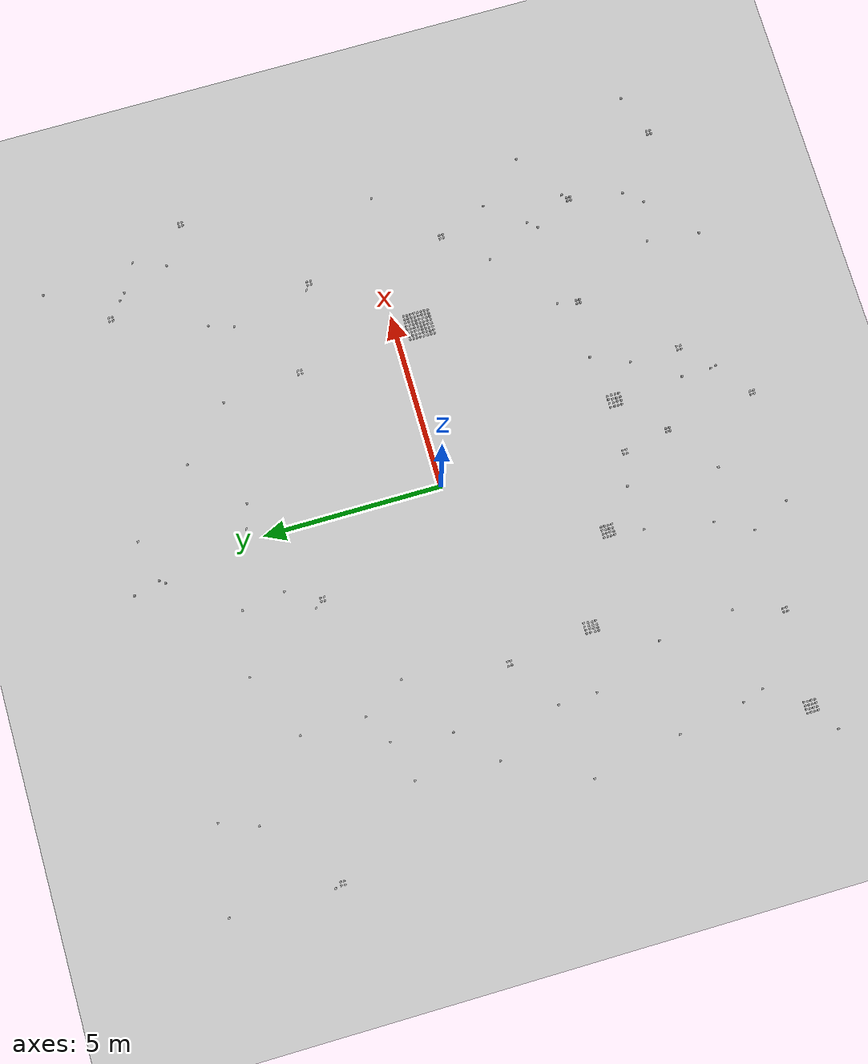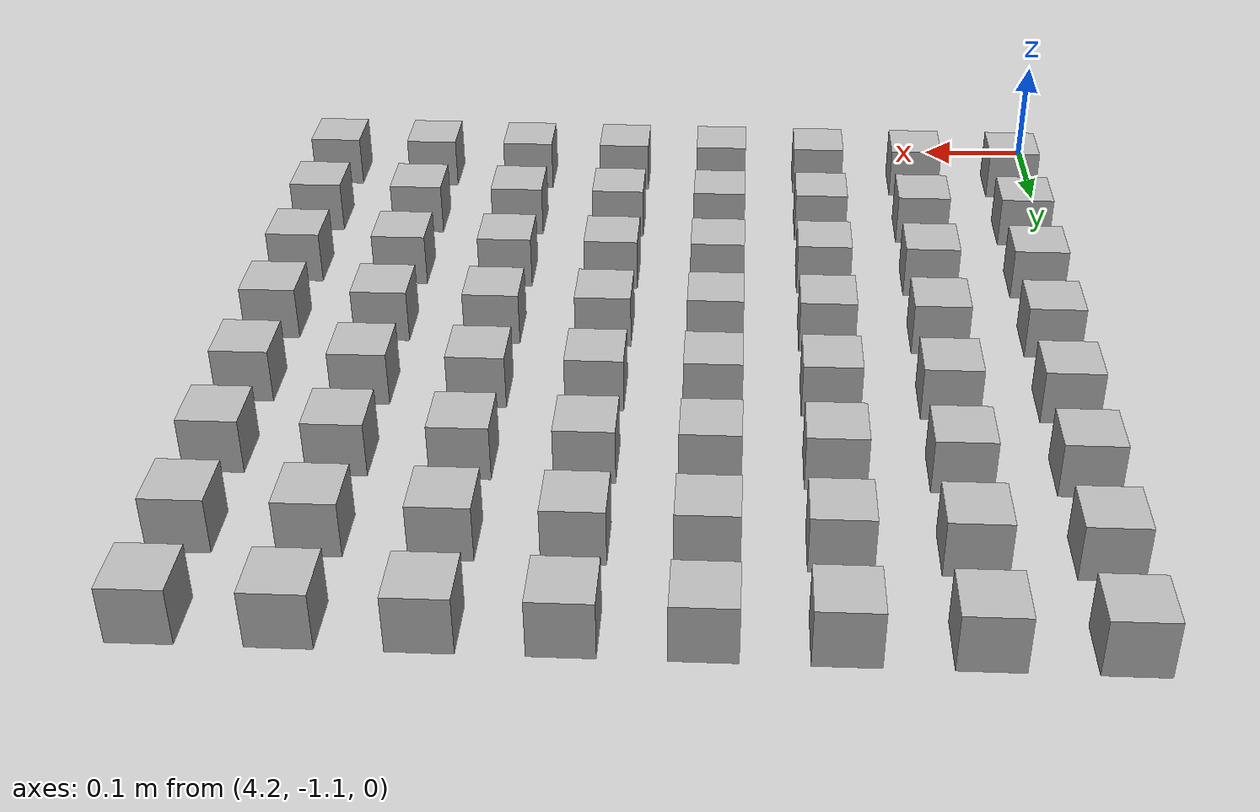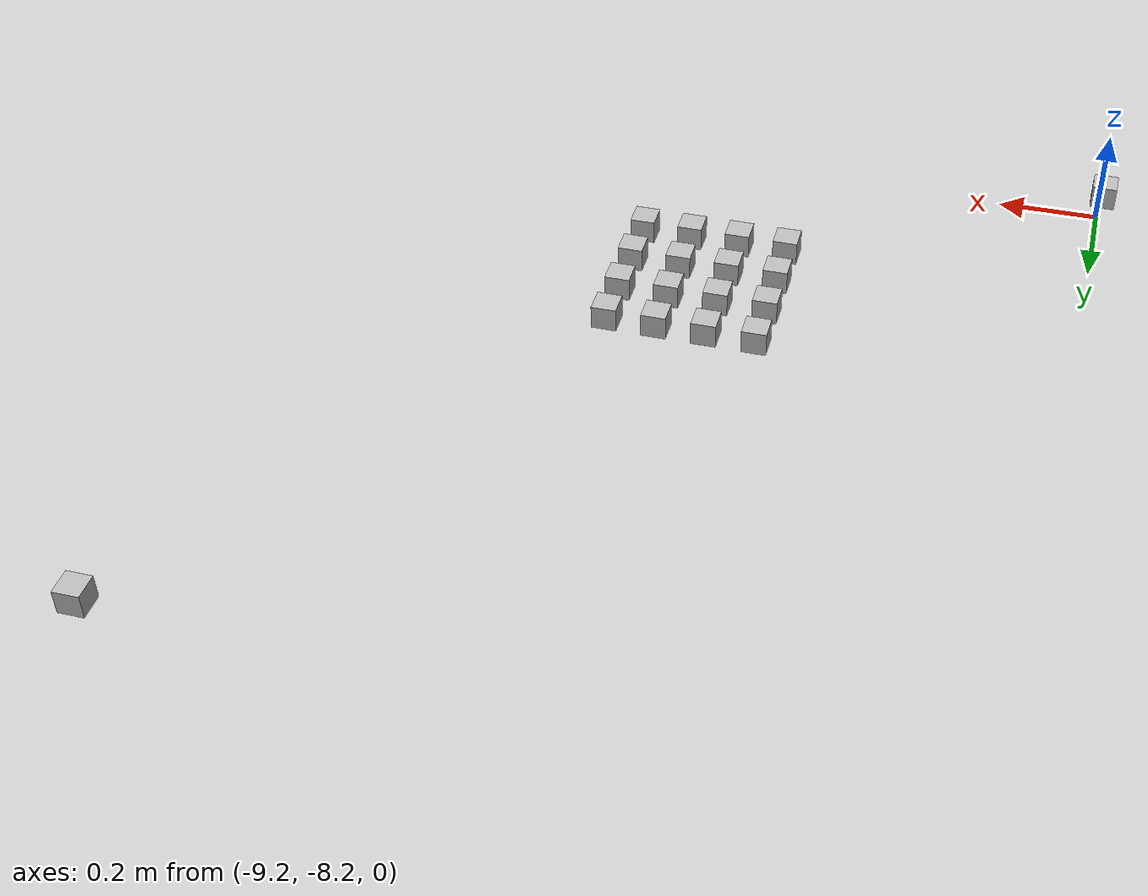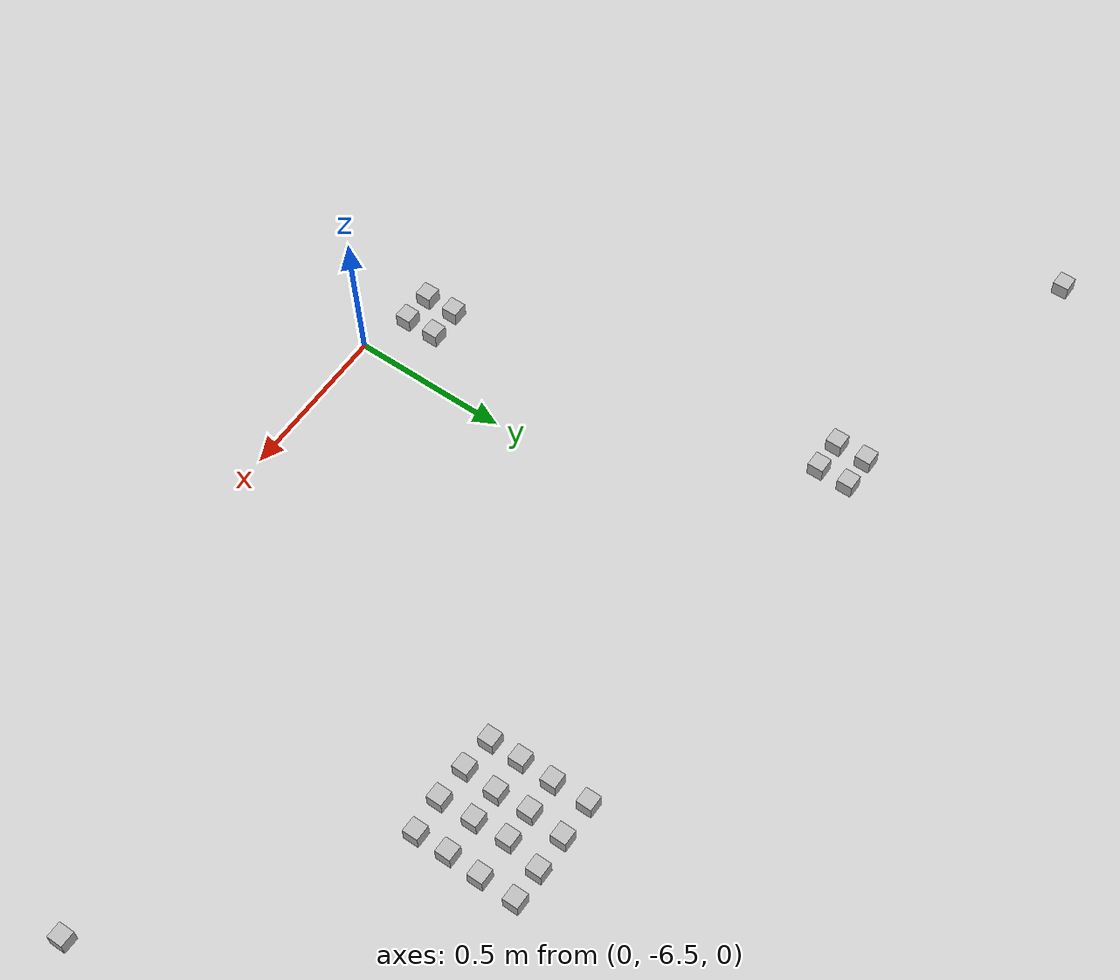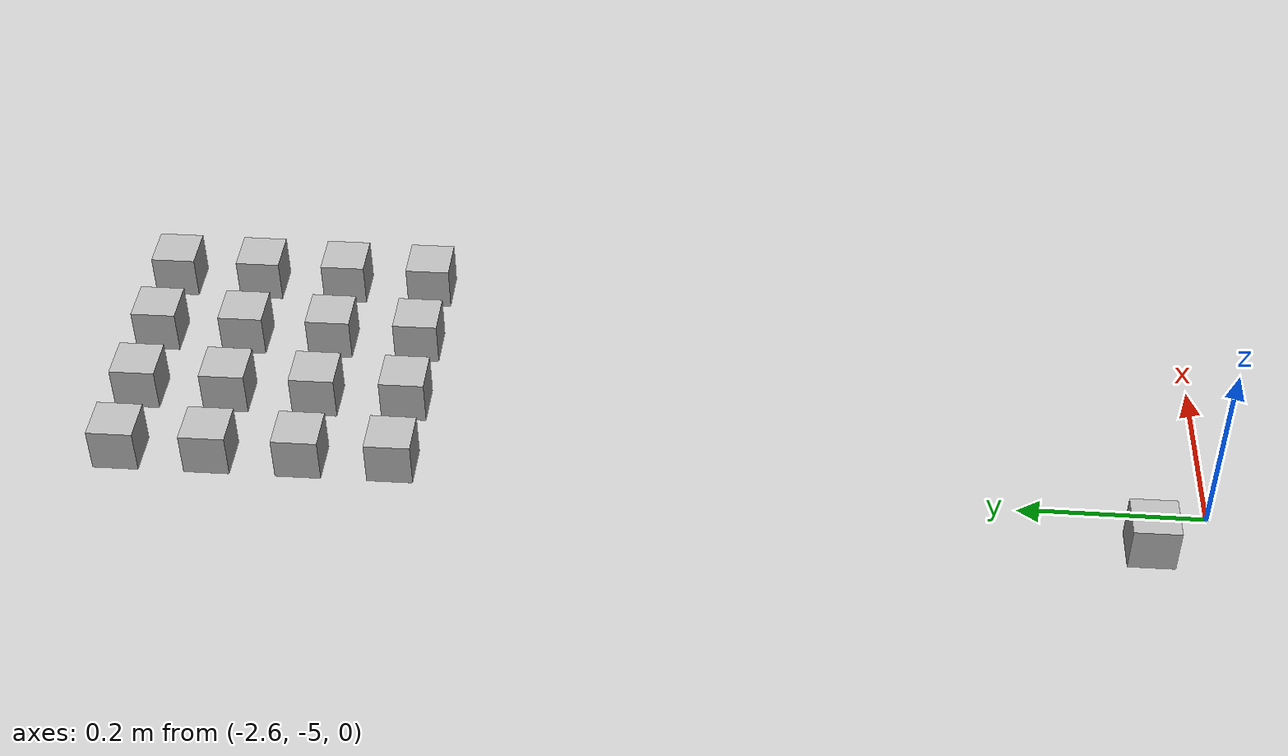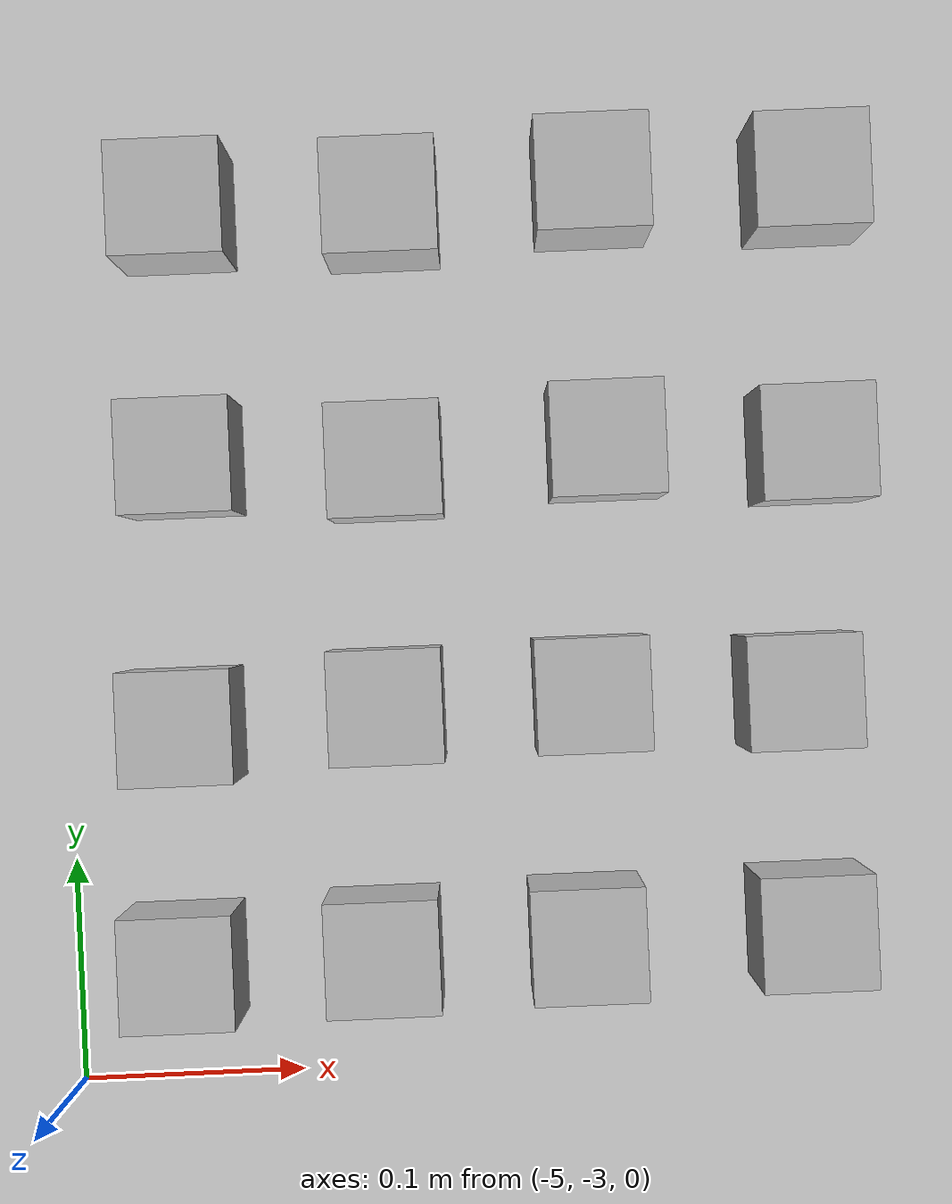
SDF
<sdf version="1.6">
 <world name="default">
  <model name="ground_plane">
   <static>1</static>
   <link name="link">
    <collision name="collision">
     <geometry><plane><normal>0 0 1</normal><size>100 100</size></plane></geometry>
     <surface><friction><ode><mu>100</mu><mu2>50</mu2></ode></friction></surface>
    </collision>
    <visual name="visual">
     <cast_shadows>0</cast_shadows>
     <geometry><plane><normal>0 0 1</normal><size>100 100</size></plane></geometry>
     <material>
      <script><uri>file://media/materials/scripts/gazebo.material</uri><name>Gazebo/Grey</name></script>
     </material>
    </visual>
   </link>
  </model>
  <light name="sun" type="directional">
   <pose>0 0 10 0 -0 0</pose>
   <diffuse>0.8 0.8 0.8 1</diffuse>
   <specular>0.1 0.1 0.1 1</specular>
   <attenuation>
    <range>1000</range>
    <constant>0.9</constant>
    <linear>0.01</linear>
    <quadratic>0.001</quadratic>
   </attenuation>
   <direction>-0.5 0.5 -1</direction>
  </light>
  <plugin name="SetupWorld" filename="libgazebo_plugins.so"/>
  <gravity>0 0 -9.8</gravity>
  <magnetic_field>6e-06 2.3e-05 -4.2e-05</magnetic_field>
  <atmosphere type="adiabatic"/>
  <physics name="default_physics" default="0" type="ode">
   <max_step_size>0.001</max_step_size>
   <real_time_factor>1</real_time_factor>
   <real_time_update_rate>1000</real_time_update_rate>
  </physics>
  <scene><ambient>0.4 0.4 0.4 1</ambient><background>0.7 0.7 0.7 1</background><shadows>1</shadows></scene>
  <spherical_coordinates>
   <surface_model>EARTH_WGS84</surface_model>
   <latitude_deg>0</latitude_deg>
   <longitude_deg>0</longitude_deg>
   <elevation>0</elevation>
   <heading_deg>0</heading_deg>
  </spherical_coordinates>
  <model name="at0">
   <static>0</static>
   <link name="link">
    <inertial>
     <mass>0.01</mass>
     <inertia><ixx>4e-05</ixx><ixy>0</ixy><ixz>0</ixz><iyy>4e-05</iyy><iyz>0</iyz><izz>4e-05</izz></inertia>
    </inertial>
    <visual name="visual">
     <geometry><box><size>0.05 0.05 0.05</size></box></geometry>
     <material>
      <script>
       <uri>model://at0/materials/scripts</uri>
       <uri>model://at0/materials/textures</uri>
       <name>at0/Diffuse</name>
      </script>
     </material>
    </visual>
    <collision name="collision">
     <geometry><box><size>0.05 0.05 0.05</size></box></geometry>
     <surface><friction><ode><mu>0.8</mu><mu2>0.7</mu2></ode></friction></surface>
    </collision>
   </link>
   <pose>4.22228 -1.02543 0.025 0 -0 0</pose>
  </model>
  <model name="at1">
   <static>0</static>
   <link name="link">
    <inertial>
     <mass>0.01</mass>
     <inertia><ixx>4e-05</ixx><ixy>0</ixy><ixz>0</ixz><iyy>4e-05</iyy><iyz>0</iyz><izz>4e-05</izz></inertia>
    </inertial>
    <visual name="visual">
     <geometry><box><size>0.05 0.05 0.05</size></box></geometry>
     <material>
      <script>
       <uri>model://at0/materials/scripts</uri>
       <uri>model://at0/materials/textures</uri>
       <name>at0/Diffuse</name>
      </script>
     </material>
    </visual>
    <collision name="collision">
     <geometry><box><size>0.05 0.05 0.05</size></box></geometry>
     <surface><friction><ode><mu>0.8</mu><mu2>0.7</mu2></ode></friction></surface>
    </collision>
   </link>
   <pose>4.32228 -1.02543 0.025 0 -0 0</pose>
  </model>
  <model name="at2">
   <static>0</static>
   <link name="link">
    <inertial>
     <mass>0.01</mass>
     <inertia><ixx>4e-05</ixx><ixy>0</ixy><ixz>0</ixz><iyy>4e-05</iyy><iyz>0</iyz><izz>4e-05</izz></inertia>
    </inertial>
    <visual name="visual">
     <geometry><box><size>0.05 0.05 0.05</size></box></geometry>
     <material>
      <script>
       <uri>model://at0/materials/scripts</uri>
       <uri>model://at0/materials/textures</uri>
       <name>at0/Diffuse</name>
      </script>
     </material>
    </visual>
    <collision name="collision">
     <geometry><box><size>0.05 0.05 0.05</size></box></geometry>
     <surface><friction><ode><mu>0.8</mu><mu2>0.7</mu2></ode></friction></surface>
    </collision>
   </link>
   <pose>4.42228 -1.02543 0.025 0 -0 0</pose>
  </model>
  <model name="at3">
   <static>0</static>
   <link name="link">
    <inertial>
     <mass>0.01</mass>
     <inertia><ixx>4e-05</ixx><ixy>0</ixy><ixz>0</ixz><iyy>4e-05</iyy><iyz>0</iyz><izz>4e-05</izz></inertia>
    </inertial>
    <visual name="visual">
     <geometry><box><size>0.05 0.05 0.05</size></box></geometry>
     <material>
      <script>
       <uri>model://at0/materials/scripts</uri>
       <uri>model://at0/materials/textures</uri>
       <name>at0/Diffuse</name>
      </script>
     </material>
    </visual>
    <collision name="collision">
     <geometry><box><size>0.05 0.05 0.05</size></box></geometry>
     <surface><friction><ode><mu>0.8</mu><mu2>0.7</mu2></ode></friction></surface>
    </collision>
   </link>
   <pose>4.52228 -1.02543 0.025 0 -0 0</pose>
  </model>
  <model name="at4">
   <static>0</static>
   <link name="link">
    <inertial>
     <mass>0.01</mass>
     <inertia><ixx>4e-05</ixx><ixy>0</ixy><ixz>0</ixz><iyy>4e-05</iyy><iyz>0</iyz><izz>4e-05</izz></inertia>
    </inertial>
    <visual name="visual">
     <geometry><box><size>0.05 0.05 0.05</size></box></geometry>
     <material>
      <script>
       <uri>model://at0/materials/scripts</uri>
       <uri>model://at0/materials/textures</uri>
       <name>at0/Diffuse</name>
      </script>
     </material>
    </visual>
    <collision name="collision">
     <geometry><box><size>0.05 0.05 0.05</size></box></geometry>
     <surface><friction><ode><mu>0.8</mu><mu2>0.7</mu2></ode></friction></surface>
    </collision>
   </link>
   <pose>4.62228 -1.02543 0.025 0 -0 0</pose>
  </model>
  <model name="at5">
   <static>0</static>
   <link name="link">
    <inertial>
     <mass>0.01</mass>
     <inertia><ixx>4e-05</ixx><ixy>0</ixy><ixz>0</ixz><iyy>4e-05</iyy><iyz>0</iyz><izz>4e-05</izz></inertia>
    </inertial>
    <visual name="visual">
     <geometry><box><size>0.05 0.05 0.05</size></box></geometry>
     <material>
      <script>
       <uri>model://at0/materials/scripts</uri>
       <uri>model://at0/materials/textures</uri>
       <name>at0/Diffuse</name>
      </script>
     </material>
    </visual>
    <collision name="collision">
     <geometry><box><size>0.05 0.05 0.05</size></box></geometry>
     <surface><friction><ode><mu>0.8</mu><mu2>0.7</mu2></ode></friction></surface>
    </collision>
   </link>
   <pose>4.72228 -1.02543 0.025 0 -0 0</pose>
  </model>
  <model name="at6">
   <static>0</static>
   <link name="link">
    <inertial>
     <mass>0.01</mass>
     <inertia><ixx>4e-05</ixx><ixy>0</ixy><ixz>0</ixz><iyy>4e-05</iyy><iyz>0</iyz><izz>4e-05</izz></inertia>
    </inertial>
    <visual name="visual">
     <geometry><box><size>0.05 0.05 0.05</size></box></geometry>
     <material>
      <script>
       <uri>model://at0/materials/scripts</uri>
       <uri>model://at0/materials/textures</uri>
       <name>at0/Diffuse</name>
      </script>
     </material>
    </visual>
    <collision name="collision">
     <geometry><box><size>0.05 0.05 0.05</size></box></geometry>
     <surface><friction><ode><mu>0.8</mu><mu2>0.7</mu2></ode></friction></surface>
    </collision>
   </link>
   <pose>4.82228 -1.02543 0.025 0 -0 0</pose>
  </model>
  <model name="at7">
   <static>0</static>
   <link name="link">
    <inertial>
     <mass>0.01</mass>
     <inertia><ixx>4e-05</ixx><ixy>0</ixy><ixz>0</ixz><iyy>4e-05</iyy><iyz>0</iyz><izz>4e-05</izz></inertia>
    </inertial>
    <visual name="visual">
     <geometry><box><size>0.05 0.05 0.05</size></box></geometry>
     <material>
      <script>
       <uri>model://at0/materials/scripts</uri>
       <uri>model://at0/materials/textures</uri>
       <name>at0/Diffuse</name>
      </script>
     </material>
    </visual>
    <collision name="collision">
     <geometry><box><size>0.05 0.05 0.05</size></box></geometry>
     <surface><friction><ode><mu>0.8</mu><mu2>0.7</mu2></ode></friction></surface>
    </collision>
   </link>
   <pose>4.92228 -1.02543 0.025 0 -0 0</pose>
  </model>
  <model name="at8">
   <static>0</static>
   <link name="link">
    <inertial>
     <mass>0.01</mass>
     <inertia><ixx>4e-05</ixx><ixy>0</ixy><ixz>0</ixz><iyy>4e-05</iyy><iyz>0</iyz><izz>4e-05</izz></inertia>
    </inertial>
    <visual name="visual">
     <geometry><box><size>0.05 0.05 0.05</size></box></geometry>
     <material>
      <script>
       <uri>model://at0/materials/scripts</uri>
       <uri>model://at0/materials/textures</uri>
       <name>at0/Diffuse</name>
      </script>
     </material>
    </visual>
    <collision name="collision">
     <geometry><box><size>0.05 0.05 0.05</size></box></geometry>
     <surface><friction><ode><mu>0.8</mu><mu2>0.7</mu2></ode></friction></surface>
    </collision>
   </link>
   <pose>4.22228 -0.92543 0.025 0 -0 0</pose>
  </model>
  <model name="at9">
   <static>0</static>
   <link name="link">
    <inertial>
     <mass>0.01</mass>
     <inertia><ixx>4e-05</ixx><ixy>0</ixy><ixz>0</ixz><iyy>4e-05</iyy><iyz>0</iyz><izz>4e-05</izz></inertia>
    </inertial>
    <visual name="visual">
     <geometry><box><size>0.05 0.05 0.05</size></box></geometry>
     <material>
      <script>
       <uri>model://at0/materials/scripts</uri>
       <uri>model://at0/materials/textures</uri>
       <name>at0/Diffuse</name>
      </script>
     </material>
    </visual>
    <collision name="collision">
     <geometry><box><size>0.05 0.05 0.05</size></box></geometry>
     <surface><friction><ode><mu>0.8</mu><mu2>0.7</mu2></ode></friction></surface>
    </collision>
   </link>
   <pose>4.32228 -0.92543 0.025 0 -0 0</pose>
  </model>
  <model name="at10">
   <static>0</static>
   <link name="link">
    <inertial>
     <mass>0.01</mass>
     <inertia><ixx>4e-05</ixx><ixy>0</ixy><ixz>0</ixz><iyy>4e-05</iyy><iyz>0</iyz><izz>4e-05</izz></inertia>
    </inertial>
    <visual name="visual">
     <geometry><box><size>0.05 0.05 0.05</size></box></geometry>
     <material>
      <script>
       <uri>model://at0/materials/scripts</uri>
       <uri>model://at0/materials/textures</uri>
       <name>at0/Diffuse</name>
      </script>
     </material>
    </visual>
    <collision name="collision">
     <geometry><box><size>0.05 0.05 0.05</size></box></geometry>
     <surface><friction><ode><mu>0.8</mu><mu2>0.7</mu2></ode></friction></surface>
    </collision>
   </link>
   <pose>4.42228 -0.92543 0.025 0 -0 0</pose>
  </model>
  <model name="at11">
   <static>0</static>
   <link name="link">
    <inertial>
     <mass>0.01</mass>
     <inertia><ixx>4e-05</ixx><ixy>0</ixy><ixz>0</ixz><iyy>4e-05</iyy><iyz>0</iyz><izz>4e-05</izz></inertia>
    </inertial>
    <visual name="visual">
     <geometry><box><size>0.05 0.05 0.05</size></box></geometry>
     <material>
      <script>
       <uri>model://at0/materials/scripts</uri>
       <uri>model://at0/materials/textures</uri>
       <name>at0/Diffuse</name>
      </script>
     </material>
    </visual>
    <collision name="collision">
     <geometry><box><size>0.05 0.05 0.05</size></box></geometry>
     <surface><friction><ode><mu>0.8</mu><mu2>0.7</mu2></ode></friction></surface>
    </collision>
   </link>
   <pose>4.52228 -0.92543 0.025 0 -0 0</pose>
  </model>
  <model name="at12">
   <static>0</static>
   <link name="link">
    <inertial>
     <mass>0.01</mass>
     <inertia><ixx>4e-05</ixx><ixy>0</ixy><ixz>0</ixz><iyy>4e-05</iyy><iyz>0</iyz><izz>4e-05</izz></inertia>
    </inertial>
    <visual name="visual">
     <geometry><box><size>0.05 0.05 0.05</size></box></geometry>
     <material>
      <script>
       <uri>model://at0/materials/scripts</uri>
       <uri>model://at0/materials/textures</uri>
       <name>at0/Diffuse</name>
      </script>
     </material>
    </visual>
    <collision name="collision">
     <geometry><box><size>0.05 0.05 0.05</size></box></geometry>
     <surface><friction><ode><mu>0.8</mu><mu2>0.7</mu2></ode></friction></surface>
    </collision>
   </link>
   <pose>4.62228 -0.92543 0.025 0 -0 0</pose>
  </model>
  <model name="at13">
   <static>0</static>
   <link name="link">
    <inertial>
     <mass>0.01</mass>
     <inertia><ixx>4e-05</ixx><ixy>0</ixy><ixz>0</ixz><iyy>4e-05</iyy><iyz>0</iyz><izz>4e-05</izz></inertia>
    </inertial>
    <visual name="visual">
     <geometry><box><size>0.05 0.05 0.05</size></box></geometry>
     <material>
      <script>
       <uri>model://at0/materials/scripts</uri>
       <uri>model://at0/materials/textures</uri>
       <name>at0/Diffuse</name>
      </script>
     </material>
    </visual>
    <collision name="collision">
     <geometry><box><size>0.05 0.05 0.05</size></box></geometry>
     <surface><friction><ode><mu>0.8</mu><mu2>0.7</mu2></ode></friction></surface>
    </collision>
   </link>
   <pose>4.72228 -0.92543 0.025 0 -0 0</pose>
  </model>
  <model name="at14">
   <static>0</static>
   <link name="link">
    <inertial>
     <mass>0.01</mass>
     <inertia><ixx>4e-05</ixx><ixy>0</ixy><ixz>0</ixz><iyy>4e-05</iyy><iyz>0</iyz><izz>4e-05</izz></inertia>
    </inertial>
    <visual name="visual">
     <geometry><box><size>0.05 0.05 0.05</size></box></geometry>
     <material>
      <script>
       <uri>model://at0/materials/scripts</uri>
       <uri>model://at0/materials/textures</uri>
       <name>at0/Diffuse</name>
      </script>
     </material>
    </visual>
    <collision name="collision">
     <geometry><box><size>0.05 0.05 0.05</size></box></geometry>
     <surface><friction><ode><mu>0.8</mu><mu2>0.7</mu2></ode></friction></surface>
    </collision>
   </link>
   <pose>4.82228 -0.92543 0.025 0 -0 0</pose>
  </model>
  <model name="at15">
   <static>0</static>
   <link name="link">
    <inertial>
     <mass>0.01</mass>
     <inertia><ixx>4e-05</ixx><ixy>0</ixy><ixz>0</ixz><iyy>4e-05</iyy><iyz>0</iyz><izz>4e-05</izz></inertia>
    </inertial>
    <visual name="visual">
     <geometry><box><size>0.05 0.05 0.05</size></box></geometry>
     <material>
      <script>
       <uri>model://at0/materials/scripts</uri>
       <uri>model://at0/materials/textures</uri>
       <name>at0/Diffuse</name>
      </script>
     </material>
    </visual>
    <collision name="collision">
     <geometry><box><size>0.05 0.05 0.05</size></box></geometry>
     <surface><friction><ode><mu>0.8</mu><mu2>0.7</mu2></ode></friction></surface>
    </collision>
   </link>
   <pose>4.92228 -0.92543 0.025 0 -0 0</pose>
  </model>
  <model name="at16">
   <static>0</static>
   <link name="link">
    <inertial>
     <mass>0.01</mass>
     <inertia><ixx>4e-05</ixx><ixy>0</ixy><ixz>0</ixz><iyy>4e-05</iyy><iyz>0</iyz><izz>4e-05</izz></inertia>
    </inertial>
    <visual name="visual">
     <geometry><box><size>0.05 0.05 0.05</size></box></geometry>
     <material>
      <script>
       <uri>model://at0/materials/scripts</uri>
       <uri>model://at0/materials/textures</uri>
       <name>at0/Diffuse</name>
      </script>
     </material>
    </visual>
    <collision name="collision">
     <geometry><box><size>0.05 0.05 0.05</size></box></geometry>
     <surface><friction><ode><mu>0.8</mu><mu2>0.7</mu2></ode></friction></surface>
    </collision>
   </link>
   <pose>4.22228 -0.82543 0.025 0 -0 0</pose>
  </model>
  <model name="at17">
   <static>0</static>
   <link name="link">
    <inertial>
     <mass>0.01</mass>
     <inertia><ixx>4e-05</ixx><ixy>0</ixy><ixz>0</ixz><iyy>4e-05</iyy><iyz>0</iyz><izz>4e-05</izz></inertia>
    </inertial>
    <visual name="visual">
     <geometry><box><size>0.05 0.05 0.05</size></box></geometry>
     <material>
      <script>
       <uri>model://at0/materials/scripts</uri>
       <uri>model://at0/materials/textures</uri>
       <name>at0/Diffuse</name>
      </script>
     </material>
    </visual>
    <collision name="collision">
     <geometry><box><size>0.05 0.05 0.05</size></box></geometry>
     <surface><friction><ode><mu>0.8</mu><mu2>0.7</mu2></ode></friction></surface>
    </collision>
   </link>
   <pose>4.32228 -0.82543 0.025 0 -0 0</pose>
  </model>
  <model name="at18">
   <static>0</static>
   <link name="link">
    <inertial>
     <mass>0.01</mass>
     <inertia><ixx>4e-05</ixx><ixy>0</ixy><ixz>0</ixz><iyy>4e-05</iyy><iyz>0</iyz><izz>4e-05</izz></inertia>
    </inertial>
    <visual name="visual">
     <geometry><box><size>0.05 0.05 0.05</size></box></geometry>
     <material>
      <script>
       <uri>model://at0/materials/scripts</uri>
       <uri>model://at0/materials/textures</uri>
       <name>at0/Diffuse</name>
      </script>
     </material>
    </visual>
    <collision name="collision">
     <geometry><box><size>0.05 0.05 0.05</size></box></geometry>
     <surface><friction><ode><mu>0.8</mu><mu2>0.7</mu2></ode></friction></surface>
    </collision>
   </link>
   <pose>4.42228 -0.82543 0.025 0 -0 0</pose>
  </model>
  <model name="at19">
   <static>0</static>
   <link name="link">
    <inertial>
     <mass>0.01</mass>
     <inertia><ixx>4e-05</ixx><ixy>0</ixy><ixz>0</ixz><iyy>4e-05</iyy><iyz>0</iyz><izz>4e-05</izz></inertia>
    </inertial>
    <visual name="visual">
     <geometry><box><size>0.05 0.05 0.05</size></box></geometry>
     <material>
      <script>
       <uri>model://at0/materials/scripts</uri>
       <uri>model://at0/materials/textures</uri>
       <name>at0/Diffuse</name>
      </script>
     </material>
    </visual>
    <collision name="collision">
     <geometry><box><size>0.05 0.05 0.05</size></box></geometry>
     <surface><friction><ode><mu>0.8</mu><mu2>0.7</mu2></ode></friction></surface>
    </collision>
   </link>
   <pose>4.52228 -0.82543 0.025 0 -0 0</pose>
  </model>
  <model name="at20">
   <static>0</static>
   <link name="link">
    <inertial>
     <mass>0.01</mass>
     <inertia><ixx>4e-05</ixx><ixy>0</ixy><ixz>0</ixz><iyy>4e-05</iyy><iyz>0</iyz><izz>4e-05</izz></inertia>
    </inertial>
    <visual name="visual">
     <geometry><box><size>0.05 0.05 0.05</size></box></geometry>
     <material>
      <script>
       <uri>model://at0/materials/scripts</uri>
       <uri>model://at0/materials/textures</uri>
       <name>at0/Diffuse</name>
      </script>
     </material>
    </visual>
    <collision name="collision">
     <geometry><box><size>0.05 0.05 0.05</size></box></geometry>
     <surface><friction><ode><mu>0.8</mu><mu2>0.7</mu2></ode></friction></surface>
    </collision>
   </link>
   <pose>4.62228 -0.82543 0.025 0 -0 0</pose>
  </model>
  <model name="at21">
   <static>0</static>
   <link name="link">
    <inertial>
     <mass>0.01</mass>
     <inertia><ixx>4e-05</ixx><ixy>0</ixy><ixz>0</ixz><iyy>4e-05</iyy><iyz>0</iyz><izz>4e-05</izz></inertia>
    </inertial>
    <visual name="visual">
     <geometry><box><size>0.05 0.05 0.05</size></box></geometry>
     <material>
      <script>
       <uri>model://at0/materials/scripts</uri>
       <uri>model://at0/materials/textures</uri>
       <name>at0/Diffuse</name>
      </script>
     </material>
    </visual>
    <collision name="collision">
     <geometry><box><size>0.05 0.05 0.05</size></box></geometry>
     <surface><friction><ode><mu>0.8</mu><mu2>0.7</mu2></ode></friction></surface>
    </collision>
   </link>
   <pose>4.72228 -0.82543 0.025 0 -0 0</pose>
  </model>
  <model name="at22">
   <static>0</static>
   <link name="link">
    <inertial>
     <mass>0.01</mass>
     <inertia><ixx>4e-05</ixx><ixy>0</ixy><ixz>0</ixz><iyy>4e-05</iyy><iyz>0</iyz><izz>4e-05</izz></inertia>
    </inertial>
    <visual name="visual">
     <geometry><box><size>0.05 0.05 0.05</size></box></geometry>
     <material>
      <script>
       <uri>model://at0/materials/scripts</uri>
       <uri>model://at0/materials/textures</uri>
       <name>at0/Diffuse</name>
      </script>
     </material>
    </visual>
    <collision name="collision">
     <geometry><box><size>0.05 0.05 0.05</size></box></geometry>
     <surface><friction><ode><mu>0.8</mu><mu2>0.7</mu2></ode></friction></surface>
    </collision>
   </link>
   <pose>4.82228 -0.82543 0.025 0 -0 0</pose>
  </model>
  <model name="at23">
   <static>0</static>
   <link name="link">
    <inertial>
     <mass>0.01</mass>
     <inertia><ixx>4e-05</ixx><ixy>0</ixy><ixz>0</ixz><iyy>4e-05</iyy><iyz>0</iyz><izz>4e-05</izz></inertia>
    </inertial>
    <visual name="visual">
     <geometry><box><size>0.05 0.05 0.05</size></box></geometry>
     <material>
      <script>
       <uri>model://at0/materials/scripts</uri>
       <uri>model://at0/materials/textures</uri>
       <name>at0/Diffuse</name>
      </script>
     </material>
    </visual>
    <collision name="collision">
     <geometry><box><size>0.05 0.05 0.05</size></box></geometry>
     <surface><friction><ode><mu>0.8</mu><mu2>0.7</mu2></ode></friction></surface>
    </collision>
   </link>
   <pose>4.92228 -0.82543 0.025 0 -0 0</pose>
  </model>
  <model name="at24">
   <static>0</static>
   <link name="link">
    <inertial>
     <mass>0.01</mass>
     <inertia><ixx>4e-05</ixx><ixy>0</ixy><ixz>0</ixz><iyy>4e-05</iyy><iyz>0</iyz><izz>4e-05</izz></inertia>
    </inertial>
    <visual name="visual">
     <geometry><box><size>0.05 0.05 0.05</size></box></geometry>
     <material>
      <script>
       <uri>model://at0/materials/scripts</uri>
       <uri>model://at0/materials/textures</uri>
       <name>at0/Diffuse</name>
      </script>
     </material>
    </visual>
    <collision name="collision">
     <geometry><box><size>0.05 0.05 0.05</size></box></geometry>
     <surface><friction><ode><mu>0.8</mu><mu2>0.7</mu2></ode></friction></surface>
    </collision>
   </link>
   <pose>4.22228 -0.72543 0.025 0 -0 0</pose>
  </model>
  <model name="at25">
   <static>0</static>
   <link name="link">
    <inertial>
     <mass>0.01</mass>
     <inertia><ixx>4e-05</ixx><ixy>0</ixy><ixz>0</ixz><iyy>4e-05</iyy><iyz>0</iyz><izz>4e-05</izz></inertia>
    </inertial>
    <visual name="visual">
     <geometry><box><size>0.05 0.05 0.05</size></box></geometry>
     <material>
      <script>
       <uri>model://at0/materials/scripts</uri>
       <uri>model://at0/materials/textures</uri>
       <name>at0/Diffuse</name>
      </script>
     </material>
    </visual>
    <collision name="collision">
     <geometry><box><size>0.05 0.05 0.05</size></box></geometry>
     <surface><friction><ode><mu>0.8</mu><mu2>0.7</mu2></ode></friction></surface>
    </collision>
   </link>
   <pose>4.32228 -0.72543 0.025 0 -0 0</pose>
  </model>
  <model name="at26">
   <static>0</static>
   <link name="link">
    <inertial>
     <mass>0.01</mass>
     <inertia><ixx>4e-05</ixx><ixy>0</ixy><ixz>0</ixz><iyy>4e-05</iyy><iyz>0</iyz><izz>4e-05</izz></inertia>
    </inertial>
    <visual name="visual">
     <geometry><box><size>0.05 0.05 0.05</size></box></geometry>
     <material>
      <script>
       <uri>model://at0/materials/scripts</uri>
       <uri>model://at0/materials/textures</uri>
       <name>at0/Diffuse</name>
      </script>
     </material>
    </visual>
    <collision name="collision">
     <geometry><box><size>0.05 0.05 0.05</size></box></geometry>
     <surface><friction><ode><mu>0.8</mu><mu2>0.7</mu2></ode></friction></surface>
    </collision>
   </link>
   <pose>4.42228 -0.72543 0.025 0 -0 0</pose>
  </model>
  <model name="at27">
   <static>0</static>
   <link name="link">
    <inertial>
     <mass>0.01</mass>
     <inertia><ixx>4e-05</ixx><ixy>0</ixy><ixz>0</ixz><iyy>4e-05</iyy><iyz>0</iyz><izz>4e-05</izz></inertia>
    </inertial>
    <visual name="visual">
     <geometry><box><size>0.05 0.05 0.05</size></box></geometry>
     <material>
      <script>
       <uri>model://at0/materials/scripts</uri>
       <uri>model://at0/materials/textures</uri>
       <name>at0/Diffuse</name>
      </script>
     </material>
    </visual>
    <collision name="collision">
     <geometry><box><size>0.05 0.05 0.05</size></box></geometry>
     <surface><friction><ode><mu>0.8</mu><mu2>0.7</mu2></ode></friction></surface>
    </collision>
   </link>
   <pose>4.52228 -0.72543 0.025 0 -0 0</pose>
  </model>
  <model name="at28">
   <static>0</static>
   <link name="link">
    <inertial>
     <mass>0.01</mass>
     <inertia><ixx>4e-05</ixx><ixy>0</ixy><ixz>0</ixz><iyy>4e-05</iyy><iyz>0</iyz><izz>4e-05</izz></inertia>
    </inertial>
    <visual name="visual">
     <geometry><box><size>0.05 0.05 0.05</size></box></geometry>
     <material>
      <script>
       <uri>model://at0/materials/scripts</uri>
       <uri>model://at0/materials/textures</uri>
       <name>at0/Diffuse</name>
      </script>
     </material>
    </visual>
    <collision name="collision">
     <geometry><box><size>0.05 0.05 0.05</size></box></geometry>
     <surface><friction><ode><mu>0.8</mu><mu2>0.7</mu2></ode></friction></surface>
    </collision>
   </link>
   <pose>4.62228 -0.72543 0.025 0 -0 0</pose>
  </model>
  <model name="at29">
   <static>0</static>
   <link name="link">
    <inertial>
     <mass>0.01</mass>
     <inertia><ixx>4e-05</ixx><ixy>0</ixy><ixz>0</ixz><iyy>4e-05</iyy><iyz>0</iyz><izz>4e-05</izz></inertia>
    </inertial>
    <visual name="visual">
     <geometry><box><size>0.05 0.05 0.05</size></box></geometry>
     <material>
      <script>
       <uri>model://at0/materials/scripts</uri>
       <uri>model://at0/materials/textures</uri>
       <name>at0/Diffuse</name>
      </script>
     </material>
    </visual>
    <collision name="collision">
     <geometry><box><size>0.05 0.05 0.05</size></box></geometry>
     <surface><friction><ode><mu>0.8</mu><mu2>0.7</mu2></ode></friction></surface>
    </collision>
   </link>
   <pose>4.72228 -0.72543 0.025 0 -0 0</pose>
  </model>
  <model name="at30">
   <static>0</static>
   <link name="link">
    <inertial>
     <mass>0.01</mass>
     <inertia><ixx>4e-05</ixx><ixy>0</ixy><ixz>0</ixz><iyy>4e-05</iyy><iyz>0</iyz><izz>4e-05</izz></inertia>
    </inertial>
    <visual name="visual">
     <geometry><box><size>0.05 0.05 0.05</size></box></geometry>
     <material>
      <script>
       <uri>model://at0/materials/scripts</uri>
       <uri>model://at0/materials/textures</uri>
       <name>at0/Diffuse</name>
      </script>
     </material>
    </visual>
    <collision name="collision">
     <geometry><box><size>0.05 0.05 0.05</size></box></geometry>
     <surface><friction><ode><mu>0.8</mu><mu2>0.7</mu2></ode></friction></surface>
    </collision>
   </link>
   <pose>4.82228 -0.72543 0.025 0 -0 0</pose>
  </model>
  <model name="at31">
   <static>0</static>
   <link name="link">
    <inertial>
     <mass>0.01</mass>
     <inertia><ixx>4e-05</ixx><ixy>0</ixy><ixz>0</ixz><iyy>4e-05</iyy><iyz>0</iyz><izz>4e-05</izz></inertia>
    </inertial>
    <visual name="visual">
     <geometry><box><size>0.05 0.05 0.05</size></box></geometry>
     <material>
      <script>
       <uri>model://at0/materials/scripts</uri>
       <uri>model://at0/materials/textures</uri>
       <name>at0/Diffuse</name>
      </script>
     </material>
    </visual>
    <collision name="collision">
     <geometry><box><size>0.05 0.05 0.05</size></box></geometry>
     <surface><friction><ode><mu>0.8</mu><mu2>0.7</mu2></ode></friction></surface>
    </collision>
   </link>
   <pose>4.92228 -0.72543 0.025 0 -0 0</pose>
  </model>
  <model name="at32">
   <static>0</static>
   <link name="link">
    <inertial>
     <mass>0.01</mass>
     <inertia><ixx>4e-05</ixx><ixy>0</ixy><ixz>0</ixz><iyy>4e-05</iyy><iyz>0</iyz><izz>4e-05</izz></inertia>
    </inertial>
    <visual name="visual">
     <geometry><box><size>0.05 0.05 0.05</size></box></geometry>
     <material>
      <script>
       <uri>model://at0/materials/scripts</uri>
       <uri>model://at0/materials/textures</uri>
       <name>at0/Diffuse</name>
      </script>
     </material>
    </visual>
    <collision name="collision">
     <geometry><box><size>0.05 0.05 0.05</size></box></geometry>
     <surface><friction><ode><mu>0.8</mu><mu2>0.7</mu2></ode></friction></surface>
    </collision>
   </link>
   <pose>4.22228 -0.62543 0.025 0 -0 0</pose>
  </model>
  <model name="at33">
   <static>0</static>
   <link name="link">
    <inertial>
     <mass>0.01</mass>
     <inertia><ixx>4e-05</ixx><ixy>0</ixy><ixz>0</ixz><iyy>4e-05</iyy><iyz>0</iyz><izz>4e-05</izz></inertia>
    </inertial>
    <visual name="visual">
     <geometry><box><size>0.05 0.05 0.05</size></box></geometry>
     <material>
      <script>
       <uri>model://at0/materials/scripts</uri>
       <uri>model://at0/materials/textures</uri>
       <name>at0/Diffuse</name>
      </script>
     </material>
    </visual>
    <collision name="collision">
     <geometry><box><size>0.05 0.05 0.05</size></box></geometry>
     <surface><friction><ode><mu>0.8</mu><mu2>0.7</mu2></ode></friction></surface>
    </collision>
   </link>
   <pose>4.32228 -0.62543 0.025 0 -0 0</pose>
  </model>
  <model name="at34">
   <static>0</static>
   <link name="link">
    <inertial>
     <mass>0.01</mass>
     <inertia><ixx>4e-05</ixx><ixy>0</ixy><ixz>0</ixz><iyy>4e-05</iyy><iyz>0</iyz><izz>4e-05</izz></inertia>
    </inertial>
    <visual name="visual">
     <geometry><box><size>0.05 0.05 0.05</size></box></geometry>
     <material>
      <script>
       <uri>model://at0/materials/scripts</uri>
       <uri>model://at0/materials/textures</uri>
       <name>at0/Diffuse</name>
      </script>
     </material>
    </visual>
    <collision name="collision">
     <geometry><box><size>0.05 0.05 0.05</size></box></geometry>
     <surface><friction><ode><mu>0.8</mu><mu2>0.7</mu2></ode></friction></surface>
    </collision>
   </link>
   <pose>4.42228 -0.62543 0.025 0 -0 0</pose>
  </model>
  <model name="at35">
   <static>0</static>
   <link name="link">
    <inertial>
     <mass>0.01</mass>
     <inertia><ixx>4e-05</ixx><ixy>0</ixy><ixz>0</ixz><iyy>4e-05</iyy><iyz>0</iyz><izz>4e-05</izz></inertia>
    </inertial>
    <visual name="visual">
     <geometry><box><size>0.05 0.05 0.05</size></box></geometry>
     <material>
      <script>
       <uri>model://at0/materials/scripts</uri>
       <uri>model://at0/materials/textures</uri>
       <name>at0/Diffuse</name>
      </script>
     </material>
    </visual>
    <collision name="collision">
     <geometry><box><size>0.05 0.05 0.05</size></box></geometry>
     <surface><friction><ode><mu>0.8</mu><mu2>0.7</mu2></ode></friction></surface>
    </collision>
   </link>
   <pose>4.52228 -0.62543 0.025 0 -0 0</pose>
  </model>
  <model name="at36">
   <static>0</static>
   <link name="link">
    <inertial>
     <mass>0.01</mass>
     <inertia><ixx>4e-05</ixx><ixy>0</ixy><ixz>0</ixz><iyy>4e-05</iyy><iyz>0</iyz><izz>4e-05</izz></inertia>
    </inertial>
    <visual name="visual">
     <geometry><box><size>0.05 0.05 0.05</size></box></geometry>
     <material>
      <script>
       <uri>model://at0/materials/scripts</uri>
       <uri>model://at0/materials/textures</uri>
       <name>at0/Diffuse</name>
      </script>
     </material>
    </visual>
    <collision name="collision">
     <geometry><box><size>0.05 0.05 0.05</size></box></geometry>
     <surface><friction><ode><mu>0.8</mu><mu2>0.7</mu2></ode></friction></surface>
    </collision>
   </link>
   <pose>4.62228 -0.62543 0.025 0 -0 0</pose>
  </model>
  <model name="at37">
   <static>0</static>
   <link name="link">
    <inertial>
     <mass>0.01</mass>
     <inertia><ixx>4e-05</ixx><ixy>0</ixy><ixz>0</ixz><iyy>4e-05</iyy><iyz>0</iyz><izz>4e-05</izz></inertia>
    </inertial>
    <visual name="visual">
     <geometry><box><size>0.05 0.05 0.05</size></box></geometry>
     <material>
      <script>
       <uri>model://at0/materials/scripts</uri>
       <uri>model://at0/materials/textures</uri>
       <name>at0/Diffuse</name>
      </script>
     </material>
    </visual>
    <collision name="collision">
     <geometry><box><size>0.05 0.05 0.05</size></box></geometry>
     <surface><friction><ode><mu>0.8</mu><mu2>0.7</mu2></ode></friction></surface>
    </collision>
   </link>
   <pose>4.72228 -0.62543 0.025 0 -0 0</pose>
  </model>
  <model name="at38">
   <static>0</static>
   <link name="link">
    <inertial>
     <mass>0.01</mass>
     <inertia><ixx>4e-05</ixx><ixy>0</ixy><ixz>0</ixz><iyy>4e-05</iyy><iyz>0</iyz><izz>4e-05</izz></inertia>
    </inertial>
    <visual name="visual">
     <geometry><box><size>0.05 0.05 0.05</size></box></geometry>
     <material>
      <script>
       <uri>model://at0/materials/scripts</uri>
       <uri>model://at0/materials/textures</uri>
       <name>at0/Diffuse</name>
      </script>
     </material>
    </visual>
    <collision name="collision">
     <geometry><box><size>0.05 0.05 0.05</size></box></geometry>
     <surface><friction><ode><mu>0.8</mu><mu2>0.7</mu2></ode></friction></surface>
    </collision>
   </link>
   <pose>4.82228 -0.62543 0.025 0 -0 0</pose>
  </model>
  <model name="at39">
   <static>0</static>
   <link name="link">
    <inertial>
     <mass>0.01</mass>
     <inertia><ixx>4e-05</ixx><ixy>0</ixy><ixz>0</ixz><iyy>4e-05</iyy><iyz>0</iyz><izz>4e-05</izz></inertia>
    </inertial>
    <visual name="visual">
     <geometry><box><size>0.05 0.05 0.05</size></box></geometry>
     <material>
      <script>
       <uri>model://at0/materials/scripts</uri>
       <uri>model://at0/materials/textures</uri>
       <name>at0/Diffuse</name>
      </script>
     </material>
    </visual>
    <collision name="collision">
     <geometry><box><size>0.05 0.05 0.05</size></box></geometry>
     <surface><friction><ode><mu>0.8</mu><mu2>0.7</mu2></ode></friction></surface>
    </collision>
   </link>
   <pose>4.92228 -0.62543 0.025 0 -0 0</pose>
  </model>
  <model name="at40">
   <static>0</static>
   <link name="link">
    <inertial>
     <mass>0.01</mass>
     <inertia><ixx>4e-05</ixx><ixy>0</ixy><ixz>0</ixz><iyy>4e-05</iyy><iyz>0</iyz><izz>4e-05</izz></inertia>
    </inertial>
    <visual name="visual">
     <geometry><box><size>0.05 0.05 0.05</size></box></geometry>
     <material>
      <script>
       <uri>model://at0/materials/scripts</uri>
       <uri>model://at0/materials/textures</uri>
       <name>at0/Diffuse</name>
      </script>
     </material>
    </visual>
    <collision name="collision">
     <geometry><box><size>0.05 0.05 0.05</size></box></geometry>
     <surface><friction><ode><mu>0.8</mu><mu2>0.7</mu2></ode></friction></surface>
    </collision>
   </link>
   <pose>4.22228 -0.52543 0.025 0 -0 0</pose>
  </model>
  <model name="at41">
   <static>0</static>
   <link name="link">
    <inertial>
     <mass>0.01</mass>
     <inertia><ixx>4e-05</ixx><ixy>0</ixy><ixz>0</ixz><iyy>4e-05</iyy><iyz>0</iyz><izz>4e-05</izz></inertia>
    </inertial>
    <visual name="visual">
     <geometry><box><size>0.05 0.05 0.05</size></box></geometry>
     <material>
      <script>
       <uri>model://at0/materials/scripts</uri>
       <uri>model://at0/materials/textures</uri>
       <name>at0/Diffuse</name>
      </script>
     </material>
    </visual>
    <collision name="collision">
     <geometry><box><size>0.05 0.05 0.05</size></box></geometry>
     <surface><friction><ode><mu>0.8</mu><mu2>0.7</mu2></ode></friction></surface>
    </collision>
   </link>
   <pose>4.32228 -0.52543 0.025 0 -0 0</pose>
  </model>
  <model name="at42">
   <static>0</static>
   <link name="link">
    <inertial>
     <mass>0.01</mass>
     <inertia><ixx>4e-05</ixx><ixy>0</ixy><ixz>0</ixz><iyy>4e-05</iyy><iyz>0</iyz><izz>4e-05</izz></inertia>
    </inertial>
    <visual name="visual">
     <geometry><box><size>0.05 0.05 0.05</size></box></geometry>
     <material>
      <script>
       <uri>model://at0/materials/scripts</uri>
       <uri>model://at0/materials/textures</uri>
       <name>at0/Diffuse</name>
      </script>
     </material>
    </visual>
    <collision name="collision">
     <geometry><box><size>0.05 0.05 0.05</size></box></geometry>
     <surface><friction><ode><mu>0.8</mu><mu2>0.7</mu2></ode></friction></surface>
    </collision>
   </link>
   <pose>4.42228 -0.52543 0.025 0 -0 0</pose>
  </model>
  <model name="at43">
   <static>0</static>
   <link name="link">
    <inertial>
     <mass>0.01</mass>
     <inertia><ixx>4e-05</ixx><ixy>0</ixy><ixz>0</ixz><iyy>4e-05</iyy><iyz>0</iyz><izz>4e-05</izz></inertia>
    </inertial>
    <visual name="visual">
     <geometry><box><size>0.05 0.05 0.05</size></box></geometry>
     <material>
      <script>
       <uri>model://at0/materials/scripts</uri>
       <uri>model://at0/materials/textures</uri>
       <name>at0/Diffuse</name>
      </script>
     </material>
    </visual>
    <collision name="collision">
     <geometry><box><size>0.05 0.05 0.05</size></box></geometry>
     <surface><friction><ode><mu>0.8</mu><mu2>0.7</mu2></ode></friction></surface>
    </collision>
   </link>
   <pose>4.52228 -0.52543 0.025 0 -0 0</pose>
  </model>
  <model name="at44">
   <static>0</static>
   <link name="link">
    <inertial>
     <mass>0.01</mass>
     <inertia><ixx>4e-05</ixx><ixy>0</ixy><ixz>0</ixz><iyy>4e-05</iyy><iyz>0</iyz><izz>4e-05</izz></inertia>
    </inertial>
    <visual name="visual">
     <geometry><box><size>0.05 0.05 0.05</size></box></geometry>
     <material>
      <script>
       <uri>model://at0/materials/scripts</uri>
       <uri>model://at0/materials/textures</uri>
       <name>at0/Diffuse</name>
      </script>
     </material>
    </visual>
    <collision name="collision">
     <geometry><box><size>0.05 0.05 0.05</size></box></geometry>
     <surface><friction><ode><mu>0.8</mu><mu2>0.7</mu2></ode></friction></surface>
    </collision>
   </link>
   <pose>4.62228 -0.52543 0.025 0 -0 0</pose>
  </model>
  <model name="at45">
   <static>0</static>
   <link name="link">
    <inertial>
     <mass>0.01</mass>
     <inertia><ixx>4e-05</ixx><ixy>0</ixy><ixz>0</ixz><iyy>4e-05</iyy><iyz>0</iyz><izz>4e-05</izz></inertia>
    </inertial>
    <visual name="visual">
     <geometry><box><size>0.05 0.05 0.05</size></box></geometry>
     <material>
      <script>
       <uri>model://at0/materials/scripts</uri>
       <uri>model://at0/materials/textures</uri>
       <name>at0/Diffuse</name>
      </script>
     </material>
    </visual>
    <collision name="collision">
     <geometry><box><size>0.05 0.05 0.05</size></box></geometry>
     <surface><friction><ode><mu>0.8</mu><mu2>0.7</mu2></ode></friction></surface>
    </collision>
   </link>
   <pose>4.72228 -0.52543 0.025 0 -0 0</pose>
  </model>
  <model name="at46">
   <static>0</static>
   <link name="link">
    <inertial>
     <mass>0.01</mass>
     <inertia><ixx>4e-05</ixx><ixy>0</ixy><ixz>0</ixz><iyy>4e-05</iyy><iyz>0</iyz><izz>4e-05</izz></inertia>
    </inertial>
    <visual name="visual">
     <geometry><box><size>0.05 0.05 0.05</size></box></geometry>
     <material>
      <script>
       <uri>model://at0/materials/scripts</uri>
       <uri>model://at0/materials/textures</uri>
       <name>at0/Diffuse</name>
      </script>
     </material>
    </visual>
    <collision name="collision">
     <geometry><box><size>0.05 0.05 0.05</size></box></geometry>
     <surface><friction><ode><mu>0.8</mu><mu2>0.7</mu2></ode></friction></surface>
    </collision>
   </link>
   <pose>4.82228 -0.52543 0.025 0 -0 0</pose>
  </model>
  <model name="at47">
   <static>0</static>
   <link name="link">
    <inertial>
     <mass>0.01</mass>
     <inertia><ixx>4e-05</ixx><ixy>0</ixy><ixz>0</ixz><iyy>4e-05</iyy><iyz>0</iyz><izz>4e-05</izz></inertia>
    </inertial>
    <visual name="visual">
     <geometry><box><size>0.05 0.05 0.05</size></box></geometry>
     <material>
      <script>
       <uri>model://at0/materials/scripts</uri>
       <uri>model://at0/materials/textures</uri>
       <name>at0/Diffuse</name>
      </script>
     </material>
    </visual>
    <collision name="collision">
     <geometry><box><size>0.05 0.05 0.05</size></box></geometry>
     <surface><friction><ode><mu>0.8</mu><mu2>0.7</mu2></ode></friction></surface>
    </collision>
   </link>
   <pose>4.92228 -0.52543 0.025 0 -0 0</pose>
  </model>
  <model name="at48">
   <static>0</static>
   <link name="link">
    <inertial>
     <mass>0.01</mass>
     <inertia><ixx>4e-05</ixx><ixy>0</ixy><ixz>0</ixz><iyy>4e-05</iyy><iyz>0</iyz><izz>4e-05</izz></inertia>
    </inertial>
    <visual name="visual">
     <geometry><box><size>0.05 0.05 0.05</size></box></geometry>
     <material>
      <script>
       <uri>model://at0/materials/scripts</uri>
       <uri>model://at0/materials/textures</uri>
       <name>at0/Diffuse</name>
      </script>
     </material>
    </visual>
    <collision name="collision">
     <geometry><box><size>0.05 0.05 0.05</size></box></geometry>
     <surface><friction><ode><mu>0.8</mu><mu2>0.7</mu2></ode></friction></surface>
    </collision>
   </link>
   <pose>4.22228 -0.42543 0.025 0 -0 0</pose>
  </model>
  <model name="at49">
   <static>0</static>
   <link name="link">
    <inertial>
     <mass>0.01</mass>
     <inertia><ixx>4e-05</ixx><ixy>0</ixy><ixz>0</ixz><iyy>4e-05</iyy><iyz>0</iyz><izz>4e-05</izz></inertia>
    </inertial>
    <visual name="visual">
     <geometry><box><size>0.05 0.05 0.05</size></box></geometry>
     <material>
      <script>
       <uri>model://at0/materials/scripts</uri>
       <uri>model://at0/materials/textures</uri>
       <name>at0/Diffuse</name>
      </script>
     </material>
    </visual>
    <collision name="collision">
     <geometry><box><size>0.05 0.05 0.05</size></box></geometry>
     <surface><friction><ode><mu>0.8</mu><mu2>0.7</mu2></ode></friction></surface>
    </collision>
   </link>
   <pose>4.32228 -0.42543 0.025 0 -0 0</pose>
  </model>
  <model name="at50">
   <static>0</static>
   <link name="link">
    <inertial>
     <mass>0.01</mass>
     <inertia><ixx>4e-05</ixx><ixy>0</ixy><ixz>0</ixz><iyy>4e-05</iyy><iyz>0</iyz><izz>4e-05</izz></inertia>
    </inertial>
    <visual name="visual">
     <geometry><box><size>0.05 0.05 0.05</size></box></geometry>
     <material>
      <script>
       <uri>model://at0/materials/scripts</uri>
       <uri>model://at0/materials/textures</uri>
       <name>at0/Diffuse</name>
      </script>
     </material>
    </visual>
    <collision name="collision">
     <geometry><box><size>0.05 0.05 0.05</size></box></geometry>
     <surface><friction><ode><mu>0.8</mu><mu2>0.7</mu2></ode></friction></surface>
    </collision>
   </link>
   <pose>4.42228 -0.42543 0.025 0 -0 0</pose>
  </model>
  <model name="at51">
   <static>0</static>
   <link name="link">
    <inertial>
     <mass>0.01</mass>
     <inertia><ixx>4e-05</ixx><ixy>0</ixy><ixz>0</ixz><iyy>4e-05</iyy><iyz>0</iyz><izz>4e-05</izz></inertia>
    </inertial>
    <visual name="visual">
     <geometry><box><size>0.05 0.05 0.05</size></box></geometry>
     <material>
      <script>
       <uri>model://at0/materials/scripts</uri>
       <uri>model://at0/materials/textures</uri>
       <name>at0/Diffuse</name>
      </script>
     </material>
    </visual>
    <collision name="collision">
     <geometry><box><size>0.05 0.05 0.05</size></box></geometry>
     <surface><friction><ode><mu>0.8</mu><mu2>0.7</mu2></ode></friction></surface>
    </collision>
   </link>
   <pose>4.52228 -0.42543 0.025 0 -0 0</pose>
  </model>
  <model name="at52">
   <static>0</static>
   <link name="link">
    <inertial>
     <mass>0.01</mass>
     <inertia><ixx>4e-05</ixx><ixy>0</ixy><ixz>0</ixz><iyy>4e-05</iyy><iyz>0</iyz><izz>4e-05</izz></inertia>
    </inertial>
    <visual name="visual">
     <geometry><box><size>0.05 0.05 0.05</size></box></geometry>
     <material>
      <script>
       <uri>model://at0/materials/scripts</uri>
       <uri>model://at0/materials/textures</uri>
       <name>at0/Diffuse</name>
      </script>
     </material>
    </visual>
    <collision name="collision">
     <geometry><box><size>0.05 0.05 0.05</size></box></geometry>
     <surface><friction><ode><mu>0.8</mu><mu2>0.7</mu2></ode></friction></surface>
    </collision>
   </link>
   <pose>4.62228 -0.42543 0.025 0 -0 0</pose>
  </model>
  <model name="at53">
   <static>0</static>
   <link name="link">
    <inertial>
     <mass>0.01</mass>
     <inertia><ixx>4e-05</ixx><ixy>0</ixy><ixz>0</ixz><iyy>4e-05</iyy><iyz>0</iyz><izz>4e-05</izz></inertia>
    </inertial>
    <visual name="visual">
     <geometry><box><size>0.05 0.05 0.05</size></box></geometry>
     <material>
      <script>
       <uri>model://at0/materials/scripts</uri>
       <uri>model://at0/materials/textures</uri>
       <name>at0/Diffuse</name>
      </script>
     </material>
    </visual>
    <collision name="collision">
     <geometry><box><size>0.05 0.05 0.05</size></box></geometry>
     <surface><friction><ode><mu>0.8</mu><mu2>0.7</mu2></ode></friction></surface>
    </collision>
   </link>
   <pose>4.72228 -0.42543 0.025 0 -0 0</pose>
  </model>
  <model name="at54">
   <static>0</static>
   <link name="link">
    <inertial>
     <mass>0.01</mass>
     <inertia><ixx>4e-05</ixx><ixy>0</ixy><ixz>0</ixz><iyy>4e-05</iyy><iyz>0</iyz><izz>4e-05</izz></inertia>
    </inertial>
    <visual name="visual">
     <geometry><box><size>0.05 0.05 0.05</size></box></geometry>
     <material>
      <script>
       <uri>model://at0/materials/scripts</uri>
       <uri>model://at0/materials/textures</uri>
       <name>at0/Diffuse</name>
      </script>
     </material>
    </visual>
    <collision name="collision">
     <geometry><box><size>0.05 0.05 0.05</size></box></geometry>
     <surface><friction><ode><mu>0.8</mu><mu2>0.7</mu2></ode></friction></surface>
    </collision>
   </link>
   <pose>4.82228 -0.42543 0.025 0 -0 0</pose>
  </model>
  <model name="at55">
   <static>0</static>
   <link name="link">
    <inertial>
     <mass>0.01</mass>
     <inertia><ixx>4e-05</ixx><ixy>0</ixy><ixz>0</ixz><iyy>4e-05</iyy><iyz>0</iyz><izz>4e-05</izz></inertia>
    </inertial>
    <visual name="visual">
     <geometry><box><size>0.05 0.05 0.05</size></box></geometry>
     <material>
      <script>
       <uri>model://at0/materials/scripts</uri>
       <uri>model://at0/materials/textures</uri>
       <name>at0/Diffuse</name>
      </script>
     </material>
    </visual>
    <collision name="collision">
     <geometry><box><size>0.05 0.05 0.05</size></box></geometry>
     <surface><friction><ode><mu>0.8</mu><mu2>0.7</mu2></ode></friction></surface>
    </collision>
   </link>
   <pose>4.92228 -0.42543 0.025 0 -0 0</pose>
  </model>
  <model name="at56">
   <static>0</static>
   <link name="link">
    <inertial>
     <mass>0.01</mass>
     <inertia><ixx>4e-05</ixx><ixy>0</ixy><ixz>0</ixz><iyy>4e-05</iyy><iyz>0</iyz><izz>4e-05</izz></inertia>
    </inertial>
    <visual name="visual">
     <geometry><box><size>0.05 0.05 0.05</size></box></geometry>
     <material>
      <script>
       <uri>model://at0/materials/scripts</uri>
       <uri>model://at0/materials/textures</uri>
       <name>at0/Diffuse</name>
      </script>
     </material>
    </visual>
    <collision name="collision">
     <geometry><box><size>0.05 0.05 0.05</size></box></geometry>
     <surface><friction><ode><mu>0.8</mu><mu2>0.7</mu2></ode></friction></surface>
    </collision>
   </link>
   <pose>4.22228 -0.32543 0.025 0 -0 0</pose>
  </model>
  <model name="at57">
   <static>0</static>
   <link name="link">
    <inertial>
     <mass>0.01</mass>
     <inertia><ixx>4e-05</ixx><ixy>0</ixy><ixz>0</ixz><iyy>4e-05</iyy><iyz>0</iyz><izz>4e-05</izz></inertia>
    </inertial>
    <visual name="visual">
     <geometry><box><size>0.05 0.05 0.05</size></box></geometry>
     <material>
      <script>
       <uri>model://at0/materials/scripts</uri>
       <uri>model://at0/materials/textures</uri>
       <name>at0/Diffuse</name>
      </script>
     </material>
    </visual>
    <collision name="collision">
     <geometry><box><size>0.05 0.05 0.05</size></box></geometry>
     <surface><friction><ode><mu>0.8</mu><mu2>0.7</mu2></ode></friction></surface>
    </collision>
   </link>
   <pose>4.32228 -0.32543 0.025 0 -0 0</pose>
  </model>
  <model name="at58">
   <static>0</static>
   <link name="link">
    <inertial>
     <mass>0.01</mass>
     <inertia><ixx>4e-05</ixx><ixy>0</ixy><ixz>0</ixz><iyy>4e-05</iyy><iyz>0</iyz><izz>4e-05</izz></inertia>
    </inertial>
    <visual name="visual">
     <geometry><box><size>0.05 0.05 0.05</size></box></geometry>
     <material>
      <script>
       <uri>model://at0/materials/scripts</uri>
       <uri>model://at0/materials/textures</uri>
       <name>at0/Diffuse</name>
      </script>
     </material>
    </visual>
    <collision name="collision">
     <geometry><box><size>0.05 0.05 0.05</size></box></geometry>
     <surface><friction><ode><mu>0.8</mu><mu2>0.7</mu2></ode></friction></surface>
    </collision>
   </link>
   <pose>4.42228 -0.32543 0.025 0 -0 0</pose>
  </model>
  <model name="at59">
   <static>0</static>
   <link name="link">
    <inertial>
     <mass>0.01</mass>
     <inertia><ixx>4e-05</ixx><ixy>0</ixy><ixz>0</ixz><iyy>4e-05</iyy><iyz>0</iyz><izz>4e-05</izz></inertia>
    </inertial>
    <visual name="visual">
     <geometry><box><size>0.05 0.05 0.05</size></box></geometry>
     <material>
      <script>
       <uri>model://at0/materials/scripts</uri>
       <uri>model://at0/materials/textures</uri>
       <name>at0/Diffuse</name>
      </script>
     </material>
    </visual>
    <collision name="collision">
     <geometry><box><size>0.05 0.05 0.05</size></box></geometry>
     <surface><friction><ode><mu>0.8</mu><mu2>0.7</mu2></ode></friction></surface>
    </collision>
   </link>
   <pose>4.52228 -0.32543 0.025 0 -0 0</pose>
  </model>
  <model name="at60">
   <static>0</static>
   <link name="link">
    <inertial>
     <mass>0.01</mass>
     <inertia><ixx>4e-05</ixx><ixy>0</ixy><ixz>0</ixz><iyy>4e-05</iyy><iyz>0</iyz><izz>4e-05</izz></inertia>
    </inertial>
    <visual name="visual">
     <geometry><box><size>0.05 0.05 0.05</size></box></geometry>
     <material>
      <script>
       <uri>model://at0/materials/scripts</uri>
       <uri>model://at0/materials/textures</uri>
       <name>at0/Diffuse</name>
      </script>
     </material>
    </visual>
    <collision name="collision">
     <geometry><box><size>0.05 0.05 0.05</size></box></geometry>
     <surface><friction><ode><mu>0.8</mu><mu2>0.7</mu2></ode></friction></surface>
    </collision>
   </link>
   <pose>4.62228 -0.32543 0.025 0 -0 0</pose>
  </model>
  <model name="at61">
   <static>0</static>
   <link name="link">
    <inertial>
     <mass>0.01</mass>
     <inertia><ixx>4e-05</ixx><ixy>0</ixy><ixz>0</ixz><iyy>4e-05</iyy><iyz>0</iyz><izz>4e-05</izz></inertia>
    </inertial>
    <visual name="visual">
     <geometry><box><size>0.05 0.05 0.05</size></box></geometry>
     <material>
      <script>
       <uri>model://at0/materials/scripts</uri>
       <uri>model://at0/materials/textures</uri>
       <name>at0/Diffuse</name>
      </script>
     </material>
    </visual>
    <collision name="collision">
     <geometry><box><size>0.05 0.05 0.05</size></box></geometry>
     <surface><friction><ode><mu>0.8</mu><mu2>0.7</mu2></ode></friction></surface>
    </collision>
   </link>
   <pose>4.72228 -0.32543 0.025 0 -0 0</pose>
  </model>
  <model name="at62">
   <static>0</static>
   <link name="link">
    <inertial>
     <mass>0.01</mass>
     <inertia><ixx>4e-05</ixx><ixy>0</ixy><ixz>0</ixz><iyy>4e-05</iyy><iyz>0</iyz><izz>4e-05</izz></inertia>
    </inertial>
    <visual name="visual">
     <geometry><box><size>0.05 0.05 0.05</size></box></geometry>
     <material>
      <script>
       <uri>model://at0/materials/scripts</uri>
       <uri>model://at0/materials/textures</uri>
       <name>at0/Diffuse</name>
      </script>
     </material>
    </visual>
    <collision name="collision">
     <geometry><box><size>0.05 0.05 0.05</size></box></geometry>
     <surface><friction><ode><mu>0.8</mu><mu2>0.7</mu2></ode></friction></surface>
    </collision>
   </link>
   <pose>4.82228 -0.32543 0.025 0 -0 0</pose>
  </model>
  <model name="at63">
   <static>0</static>
   <link name="link">
    <inertial>
     <mass>0.01</mass>
     <inertia><ixx>4e-05</ixx><ixy>0</ixy><ixz>0</ixz><iyy>4e-05</iyy><iyz>0</iyz><izz>4e-05</izz></inertia>
    </inertial>
    <visual name="visual">
     <geometry><box><size>0.05 0.05 0.05</size></box></geometry>
     <material>
      <script>
       <uri>model://at0/materials/scripts</uri>
       <uri>model://at0/materials/textures</uri>
       <name>at0/Diffuse</name>
      </script>
     </material>
    </visual>
    <collision name="collision">
     <geometry><box><size>0.05 0.05 0.05</size></box></geometry>
     <surface><friction><ode><mu>0.8</mu><mu2>0.7</mu2></ode></friction></surface>
    </collision>
   </link>
   <pose>4.92228 -0.32543 0.025 0 -0 0</pose>
  </model>
  <model name="at64">
   <static>0</static>
   <link name="link">
    <inertial>
     <mass>0.01</mass>
     <inertia><ixx>4e-05</ixx><ixy>0</ixy><ixz>0</ixz><iyy>4e-05</iyy><iyz>0</iyz><izz>4e-05</izz></inertia>
    </inertial>
    <visual name="visual">
     <geometry><box><size>0.05 0.05 0.05</size></box></geometry>
     <material>
      <script>
       <uri>model://at0/materials/scripts</uri>
       <uri>model://at0/materials/textures</uri>
       <name>at0/Diffuse</name>
      </script>
     </material>
    </visual>
    <collision name="collision">
     <geometry><box><size>0.05 0.05 0.05</size></box></geometry>
     <surface><friction><ode><mu>0.8</mu><mu2>0.7</mu2></ode></friction></surface>
    </collision>
   </link>
   <pose>1.17461 -5.40443 0.025 0 -0 0</pose>
  </model>
  <model name="at65">
   <static>0</static>
   <link name="link">
    <inertial>
     <mass>0.01</mass>
     <inertia><ixx>4e-05</ixx><ixy>0</ixy><ixz>0</ixz><iyy>4e-05</iyy><iyz>0</iyz><izz>4e-05</izz></inertia>
    </inertial>
    <visual name="visual">
     <geometry><box><size>0.05 0.05 0.05</size></box></geometry>
     <material>
      <script>
       <uri>model://at0/materials/scripts</uri>
       <uri>model://at0/materials/textures</uri>
       <name>at0/Diffuse</name>
      </script>
     </material>
    </visual>
    <collision name="collision">
     <geometry><box><size>0.05 0.05 0.05</size></box></geometry>
     <surface><friction><ode><mu>0.8</mu><mu2>0.7</mu2></ode></friction></surface>
    </collision>
   </link>
   <pose>1.06059 -5.41181 0.025 0 -0 0</pose>
  </model>
  <model name="at66">
   <static>0</static>
   <link name="link">
    <inertial>
     <mass>0.01</mass>
     <inertia><ixx>4e-05</ixx><ixy>0</ixy><ixz>0</ixz><iyy>4e-05</iyy><iyz>0</iyz><izz>4e-05</izz></inertia>
    </inertial>
    <visual name="visual">
     <geometry><box><size>0.05 0.05 0.05</size></box></geometry>
     <material>
      <script>
       <uri>model://at0/materials/scripts</uri>
       <uri>model://at0/materials/textures</uri>
       <name>at0/Diffuse</name>
      </script>
     </material>
    </visual>
    <collision name="collision">
     <geometry><box><size>0.05 0.05 0.05</size></box></geometry>
     <surface><friction><ode><mu>0.8</mu><mu2>0.7</mu2></ode></friction></surface>
    </collision>
   </link>
   <pose>0.84444 -5.40127 0.025 0 -0 0</pose>
  </model>
  <model name="at67">
   <static>0</static>
   <link name="link">
    <inertial>
     <mass>0.01</mass>
     <inertia><ixx>4e-05</ixx><ixy>0</ixy><ixz>0</ixz><iyy>4e-05</iyy><iyz>0</iyz><izz>4e-05</izz></inertia>
    </inertial>
    <visual name="visual">
     <geometry><box><size>0.05 0.05 0.05</size></box></geometry>
     <material>
      <script>
       <uri>model://at0/materials/scripts</uri>
       <uri>model://at0/materials/textures</uri>
       <name>at0/Diffuse</name>
      </script>
     </material>
    </visual>
    <collision name="collision">
     <geometry><box><size>0.05 0.05 0.05</size></box></geometry>
     <surface><friction><ode><mu>0.8</mu><mu2>0.7</mu2></ode></friction></surface>
    </collision>
   </link>
   <pose>0.950567 -5.4091 0.025 0 -0 0</pose>
  </model>
  <model name="at68">
   <static>0</static>
   <link name="link">
    <inertial>
     <mass>0.01</mass>
     <inertia><ixx>4e-05</ixx><ixy>0</ixy><ixz>0</ixz><iyy>4e-05</iyy><iyz>0</iyz><izz>4e-05</izz></inertia>
    </inertial>
    <visual name="visual">
     <geometry><box><size>0.05 0.05 0.05</size></box></geometry>
     <material>
      <script>
       <uri>model://at0/materials/scripts</uri>
       <uri>model://at0/materials/textures</uri>
       <name>at0/Diffuse</name>
      </script>
     </material>
    </visual>
    <collision name="collision">
     <geometry><box><size>0.05 0.05 0.05</size></box></geometry>
     <surface><friction><ode><mu>0.8</mu><mu2>0.7</mu2></ode></friction></surface>
    </collision>
   </link>
   <pose>1.17178 -5.29925 0.025 0 -0 0</pose>
  </model>
  <model name="at69">
   <static>0</static>
   <link name="link">
    <inertial>
     <mass>0.01</mass>
     <inertia><ixx>4e-05</ixx><ixy>0</ixy><ixz>0</ixz><iyy>4e-05</iyy><iyz>0</iyz><izz>4e-05</izz></inertia>
    </inertial>
    <visual name="visual">
     <geometry><box><size>0.05 0.05 0.05</size></box></geometry>
     <material>
      <script>
       <uri>model://at0/materials/scripts</uri>
       <uri>model://at0/materials/textures</uri>
       <name>at0/Diffuse</name>
      </script>
     </material>
    </visual>
    <collision name="collision">
     <geometry><box><size>0.05 0.05 0.05</size></box></geometry>
     <surface><friction><ode><mu>0.8</mu><mu2>0.7</mu2></ode></friction></surface>
    </collision>
   </link>
   <pose>1.05684 -5.29925 0.025 0 -0 0</pose>
  </model>
  <model name="at70">
   <static>0</static>
   <link name="link">
    <inertial>
     <mass>0.01</mass>
     <inertia><ixx>4e-05</ixx><ixy>0</ixy><ixz>0</ixz><iyy>4e-05</iyy><iyz>0</iyz><izz>4e-05</izz></inertia>
    </inertial>
    <visual name="visual">
     <geometry><box><size>0.05 0.05 0.05</size></box></geometry>
     <material>
      <script>
       <uri>model://at0/materials/scripts</uri>
       <uri>model://at0/materials/textures</uri>
       <name>at0/Diffuse</name>
      </script>
     </material>
    </visual>
    <collision name="collision">
     <geometry><box><size>0.05 0.05 0.05</size></box></geometry>
     <surface><friction><ode><mu>0.8</mu><mu2>0.7</mu2></ode></friction></surface>
    </collision>
   </link>
   <pose>0.844045 -5.29925 0.025 0 -0 0</pose>
  </model>
  <model name="at71">
   <static>0</static>
   <link name="link">
    <inertial>
     <mass>0.01</mass>
     <inertia><ixx>4e-05</ixx><ixy>0</ixy><ixz>0</ixz><iyy>4e-05</iyy><iyz>0</iyz><izz>4e-05</izz></inertia>
    </inertial>
    <visual name="visual">
     <geometry><box><size>0.05 0.05 0.05</size></box></geometry>
     <material>
      <script>
       <uri>model://at0/materials/scripts</uri>
       <uri>model://at0/materials/textures</uri>
       <name>at0/Diffuse</name>
      </script>
     </material>
    </visual>
    <collision name="collision">
     <geometry><box><size>0.05 0.05 0.05</size></box></geometry>
     <surface><friction><ode><mu>0.8</mu><mu2>0.7</mu2></ode></friction></surface>
    </collision>
   </link>
   <pose>0.957758 -5.29925 0.025 0 -0 0</pose>
  </model>
  <model name="at72">
   <static>0</static>
   <link name="link">
    <inertial>
     <mass>0.01</mass>
     <inertia><ixx>4e-05</ixx><ixy>0</ixy><ixz>0</ixz><iyy>4e-05</iyy><iyz>0</iyz><izz>4e-05</izz></inertia>
    </inertial>
    <visual name="visual">
     <geometry><box><size>0.05 0.05 0.05</size></box></geometry>
     <material>
      <script>
       <uri>model://at0/materials/scripts</uri>
       <uri>model://at0/materials/textures</uri>
       <name>at0/Diffuse</name>
      </script>
     </material>
    </visual>
    <collision name="collision">
     <geometry><box><size>0.05 0.05 0.05</size></box></geometry>
     <surface><friction><ode><mu>0.8</mu><mu2>0.7</mu2></ode></friction></surface>
    </collision>
   </link>
   <pose>1.17571 -5.19092 0.025 0 -0 0</pose>
  </model>
  <model name="at73">
   <static>0</static>
   <link name="link">
    <inertial>
     <mass>0.01</mass>
     <inertia><ixx>4e-05</ixx><ixy>0</ixy><ixz>0</ixz><iyy>4e-05</iyy><iyz>0</iyz><izz>4e-05</izz></inertia>
    </inertial>
    <visual name="visual">
     <geometry><box><size>0.05 0.05 0.05</size></box></geometry>
     <material>
      <script>
       <uri>model://at0/materials/scripts</uri>
       <uri>model://at0/materials/textures</uri>
       <name>at0/Diffuse</name>
      </script>
     </material>
    </visual>
    <collision name="collision">
     <geometry><box><size>0.05 0.05 0.05</size></box></geometry>
     <surface><friction><ode><mu>0.8</mu><mu2>0.7</mu2></ode></friction></surface>
    </collision>
   </link>
   <pose>1.04982 -5.19092 0.025 0 -0 0</pose>
  </model>
  <model name="at74">
   <static>0</static>
   <link name="link">
    <inertial>
     <mass>0.01</mass>
     <inertia><ixx>4e-05</ixx><ixy>0</ixy><ixz>0</ixz><iyy>4e-05</iyy><iyz>0</iyz><izz>4e-05</izz></inertia>
    </inertial>
    <visual name="visual">
     <geometry><box><size>0.05 0.05 0.05</size></box></geometry>
     <material>
      <script>
       <uri>model://at0/materials/scripts</uri>
       <uri>model://at0/materials/textures</uri>
       <name>at0/Diffuse</name>
      </script>
     </material>
    </visual>
    <collision name="collision">
     <geometry><box><size>0.05 0.05 0.05</size></box></geometry>
     <surface><friction><ode><mu>0.8</mu><mu2>0.7</mu2></ode></friction></surface>
    </collision>
   </link>
   <pose>0.846467 -5.19092 0.025 0 -0 0</pose>
  </model>
  <model name="at75">
   <static>0</static>
   <link name="link">
    <inertial>
     <mass>0.01</mass>
     <inertia><ixx>4e-05</ixx><ixy>0</ixy><ixz>0</ixz><iyy>4e-05</iyy><iyz>0</iyz><izz>4e-05</izz></inertia>
    </inertial>
    <visual name="visual">
     <geometry><box><size>0.05 0.05 0.05</size></box></geometry>
     <material>
      <script>
       <uri>model://at0/materials/scripts</uri>
       <uri>model://at0/materials/textures</uri>
       <name>at0/Diffuse</name>
      </script>
     </material>
    </visual>
    <collision name="collision">
     <geometry><box><size>0.05 0.05 0.05</size></box></geometry>
     <surface><friction><ode><mu>0.8</mu><mu2>0.7</mu2></ode></friction></surface>
    </collision>
   </link>
   <pose>0.952294 -5.19092 0.025 0 -0 0</pose>
  </model>
  <model name="at76">
   <static>0</static>
   <link name="link">
    <inertial>
     <mass>0.01</mass>
     <inertia><ixx>4e-05</ixx><ixy>0</ixy><ixz>0</ixz><iyy>4e-05</iyy><iyz>0</iyz><izz>4e-05</izz></inertia>
    </inertial>
    <visual name="visual">
     <geometry><box><size>0.05 0.05 0.05</size></box></geometry>
     <material>
      <script>
       <uri>model://at0/materials/scripts</uri>
       <uri>model://at0/materials/textures</uri>
       <name>at0/Diffuse</name>
      </script>
     </material>
    </visual>
    <collision name="collision">
     <geometry><box><size>0.05 0.05 0.05</size></box></geometry>
     <surface><friction><ode><mu>0.8</mu><mu2>0.7</mu2></ode></friction></surface>
    </collision>
   </link>
   <pose>1.17694 -5.07446 0.025 0 -0 0</pose>
  </model>
  <model name="at77">
   <static>0</static>
   <link name="link">
    <inertial>
     <mass>0.01</mass>
     <inertia><ixx>4e-05</ixx><ixy>0</ixy><ixz>0</ixz><iyy>4e-05</iyy><iyz>0</iyz><izz>4e-05</izz></inertia>
    </inertial>
    <visual name="visual">
     <geometry><box><size>0.05 0.05 0.05</size></box></geometry>
     <material>
      <script>
       <uri>model://at0/materials/scripts</uri>
       <uri>model://at0/materials/textures</uri>
       <name>at0/Diffuse</name>
      </script>
     </material>
    </visual>
    <collision name="collision">
     <geometry><box><size>0.05 0.05 0.05</size></box></geometry>
     <surface><friction><ode><mu>0.8</mu><mu2>0.7</mu2></ode></friction></surface>
    </collision>
   </link>
   <pose>1.07386 -5.07446 0.025 0 -0 0</pose>
  </model>
  <model name="at78">
   <static>0</static>
   <link name="link">
    <inertial>
     <mass>0.01</mass>
     <inertia><ixx>4e-05</ixx><ixy>0</ixy><ixz>0</ixz><iyy>4e-05</iyy><iyz>0</iyz><izz>4e-05</izz></inertia>
    </inertial>
    <visual name="visual">
     <geometry><box><size>0.05 0.05 0.05</size></box></geometry>
     <material>
      <script>
       <uri>model://at0/materials/scripts</uri>
       <uri>model://at0/materials/textures</uri>
       <name>at0/Diffuse</name>
      </script>
     </material>
    </visual>
    <collision name="collision">
     <geometry><box><size>0.05 0.05 0.05</size></box></geometry>
     <surface><friction><ode><mu>0.8</mu><mu2>0.7</mu2></ode></friction></surface>
    </collision>
   </link>
   <pose>0.843832 -5.07446 0.024998 -3.7e-05 -2.6e-05 -5e-06</pose>
  </model>
  <model name="at79">
   <static>0</static>
   <link name="link">
    <inertial>
     <mass>0.01</mass>
     <inertia><ixx>4e-05</ixx><ixy>0</ixy><ixz>0</ixz><iyy>4e-05</iyy><iyz>0</iyz><izz>4e-05</izz></inertia>
    </inertial>
    <visual name="visual">
     <geometry><box><size>0.05 0.05 0.05</size></box></geometry>
     <material>
      <script>
       <uri>model://at0/materials/scripts</uri>
       <uri>model://at0/materials/textures</uri>
       <name>at0/Diffuse</name>
      </script>
     </material>
    </visual>
    <collision name="collision">
     <geometry><box><size>0.05 0.05 0.05</size></box></geometry>
     <surface><friction><ode><mu>0.8</mu><mu2>0.7</mu2></ode></friction></surface>
    </collision>
   </link>
   <pose>0.961993 -5.07446 0.024999 -1.2e-05 -2e-05 -6e-06</pose>
  </model>
  <model name="at80">
   <static>0</static>
   <link name="link">
    <inertial>
     <mass>0.01</mass>
     <inertia><ixx>4e-05</ixx><ixy>0</ixy><ixz>0</ixz><iyy>4e-05</iyy><iyz>0</iyz><izz>4e-05</izz></inertia>
    </inertial>
    <visual name="visual">
     <geometry><box><size>0.05 0.05 0.05</size></box></geometry>
     <material>
      <script>
       <uri>model://at0/materials/scripts</uri>
       <uri>model://at0/materials/textures</uri>
       <name>at0/Diffuse</name>
      </script>
     </material>
    </visual>
    <collision name="collision">
     <geometry><box><size>0.05 0.05 0.05</size></box></geometry>
     <surface><friction><ode><mu>0.8</mu><mu2>0.7</mu2></ode></friction></surface>
    </collision>
   </link>
   <pose>-4.9492 -2.94575 0.025 0 -0 0</pose>
  </model>
  <model name="at81">
   <static>0</static>
   <link name="link">
    <inertial>
     <mass>0.01</mass>
     <inertia><ixx>4e-05</ixx><ixy>0</ixy><ixz>0</ixz><iyy>4e-05</iyy><iyz>0</iyz><izz>4e-05</izz></inertia>
    </inertial>
    <visual name="visual">
     <geometry><box><size>0.05 0.05 0.05</size></box></geometry>
     <material>
      <script>
       <uri>model://at0/materials/scripts</uri>
       <uri>model://at0/materials/textures</uri>
       <name>at0/Diffuse</name>
      </script>
     </material>
    </visual>
    <collision name="collision">
     <geometry><box><size>0.05 0.05 0.05</size></box></geometry>
     <surface><friction><ode><mu>0.8</mu><mu2>0.7</mu2></ode></friction></surface>
    </collision>
   </link>
   <pose>-4.85987 -2.94272 0.025 0 -0 0</pose>
  </model>
  <model name="at82">
   <static>0</static>
   <link name="link">
    <inertial>
     <mass>0.01</mass>
     <inertia><ixx>4e-05</ixx><ixy>0</ixy><ixz>0</ixz><iyy>4e-05</iyy><iyz>0</iyz><izz>4e-05</izz></inertia>
    </inertial>
    <visual name="visual">
     <geometry><box><size>0.05 0.05 0.05</size></box></geometry>
     <material>
      <script>
       <uri>model://at0/materials/scripts</uri>
       <uri>model://at0/materials/textures</uri>
       <name>at0/Diffuse</name>
      </script>
     </material>
    </visual>
    <collision name="collision">
     <geometry><box><size>0.05 0.05 0.05</size></box></geometry>
     <surface><friction><ode><mu>0.8</mu><mu2>0.7</mu2></ode></friction></surface>
    </collision>
   </link>
   <pose>-4.67083 -2.93969 0.025 0 -0 0</pose>
  </model>
  <model name="at83">
   <static>0</static>
   <link name="link">
    <inertial>
     <mass>0.01</mass>
     <inertia><ixx>4e-05</ixx><ixy>0</ixy><ixz>0</ixz><iyy>4e-05</iyy><iyz>0</iyz><izz>4e-05</izz></inertia>
    </inertial>
    <visual name="visual">
     <geometry><box><size>0.05 0.05 0.05</size></box></geometry>
     <material>
      <script>
       <uri>model://at0/materials/scripts</uri>
       <uri>model://at0/materials/textures</uri>
       <name>at0/Diffuse</name>
      </script>
     </material>
    </visual>
    <collision name="collision">
     <geometry><box><size>0.05 0.05 0.05</size></box></geometry>
     <surface><friction><ode><mu>0.8</mu><mu2>0.7</mu2></ode></friction></surface>
    </collision>
   </link>
   <pose>-4.67229 -2.83522 0.025 0 -0 0</pose>
  </model>
  <model name="at84">
   <static>0</static>
   <link name="link">
    <inertial>
     <mass>0.01</mass>
     <inertia><ixx>4e-05</ixx><ixy>0</ixy><ixz>0</ixz><iyy>4e-05</iyy><iyz>0</iyz><izz>4e-05</izz></inertia>
    </inertial>
    <visual name="visual">
     <geometry><box><size>0.05 0.05 0.05</size></box></geometry>
     <material>
      <script>
       <uri>model://at0/materials/scripts</uri>
       <uri>model://at0/materials/textures</uri>
       <name>at0/Diffuse</name>
      </script>
     </material>
    </visual>
    <collision name="collision">
     <geometry><box><size>0.05 0.05 0.05</size></box></geometry>
     <surface><friction><ode><mu>0.8</mu><mu2>0.7</mu2></ode></friction></surface>
    </collision>
   </link>
   <pose>-4.94049 -2.60987 0.025 0 -0 0</pose>
  </model>
  <model name="at85">
   <static>0</static>
   <link name="link">
    <inertial>
     <mass>0.01</mass>
     <inertia><ixx>4e-05</ixx><ixy>0</ixy><ixz>0</ixz><iyy>4e-05</iyy><iyz>0</iyz><izz>4e-05</izz></inertia>
    </inertial>
    <visual name="visual">
     <geometry><box><size>0.05 0.05 0.05</size></box></geometry>
     <material>
      <script>
       <uri>model://at0/materials/scripts</uri>
       <uri>model://at0/materials/textures</uri>
       <name>at0/Diffuse</name>
      </script>
     </material>
    </visual>
    <collision name="collision">
     <geometry><box><size>0.05 0.05 0.05</size></box></geometry>
     <surface><friction><ode><mu>0.8</mu><mu2>0.7</mu2></ode></friction></surface>
    </collision>
   </link>
   <pose>-4.76383 -2.83274 0.025 0 -0 0</pose>
  </model>
  <model name="at86">
   <static>0</static>
   <link name="link">
    <inertial>
     <mass>0.01</mass>
     <inertia><ixx>4e-05</ixx><ixy>0</ixy><ixz>0</ixz><iyy>4e-05</iyy><iyz>0</iyz><izz>4e-05</izz></inertia>
    </inertial>
    <visual name="visual">
     <geometry><box><size>0.05 0.05 0.05</size></box></geometry>
     <material>
      <script>
       <uri>model://at0/materials/scripts</uri>
       <uri>model://at0/materials/textures</uri>
       <name>at0/Diffuse</name>
      </script>
     </material>
    </visual>
    <collision name="collision">
     <geometry><box><size>0.05 0.05 0.05</size></box></geometry>
     <surface><friction><ode><mu>0.8</mu><mu2>0.7</mu2></ode></friction></surface>
    </collision>
   </link>
   <pose>-4.85418 -2.83415 0.025 0 -0 0</pose>
  </model>
  <model name="at87">
   <static>0</static>
   <link name="link">
    <inertial>
     <mass>0.01</mass>
     <inertia><ixx>4e-05</ixx><ixy>0</ixy><ixz>0</ixz><iyy>4e-05</iyy><iyz>0</iyz><izz>4e-05</izz></inertia>
    </inertial>
    <visual name="visual">
     <geometry><box><size>0.05 0.05 0.05</size></box></geometry>
     <material>
      <script>
       <uri>model://at0/materials/scripts</uri>
       <uri>model://at0/materials/textures</uri>
       <name>at0/Diffuse</name>
      </script>
     </material>
    </visual>
    <collision name="collision">
     <geometry><box><size>0.05 0.05 0.05</size></box></geometry>
     <surface><friction><ode><mu>0.8</mu><mu2>0.7</mu2></ode></friction></surface>
    </collision>
   </link>
   <pose>-4.84769 -2.61283 0.025 0 -0 0</pose>
  </model>
  <model name="at88">
   <static>0</static>
   <link name="link">
    <inertial>
     <mass>0.01</mass>
     <inertia><ixx>4e-05</ixx><ixy>0</ixy><ixz>0</ixz><iyy>4e-05</iyy><iyz>0</iyz><izz>4e-05</izz></inertia>
    </inertial>
    <visual name="visual">
     <geometry><box><size>0.05 0.05 0.05</size></box></geometry>
     <material>
      <script>
       <uri>model://at0/materials/scripts</uri>
       <uri>model://at0/materials/textures</uri>
       <name>at0/Diffuse</name>
      </script>
     </material>
    </visual>
    <collision name="collision">
     <geometry><box><size>0.05 0.05 0.05</size></box></geometry>
     <surface><friction><ode><mu>0.8</mu><mu2>0.7</mu2></ode></friction></surface>
    </collision>
   </link>
   <pose>-4.85047 -2.72683 0.025 0 -0 0</pose>
  </model>
  <model name="at89">
   <static>0</static>
   <link name="link">
    <inertial>
     <mass>0.01</mass>
     <inertia><ixx>4e-05</ixx><ixy>0</ixy><ixz>0</ixz><iyy>4e-05</iyy><iyz>0</iyz><izz>4e-05</izz></inertia>
    </inertial>
    <visual name="visual">
     <geometry><box><size>0.05 0.05 0.05</size></box></geometry>
     <material>
      <script>
       <uri>model://at0/materials/scripts</uri>
       <uri>model://at0/materials/textures</uri>
       <name>at0/Diffuse</name>
      </script>
     </material>
    </visual>
    <collision name="collision">
     <geometry><box><size>0.05 0.05 0.05</size></box></geometry>
     <surface><friction><ode><mu>0.8</mu><mu2>0.7</mu2></ode></friction></surface>
    </collision>
   </link>
   <pose>-4.77015 -2.94092 0.025 0 -0 0</pose>
  </model>
  <model name="at90">
   <static>0</static>
   <link name="link">
    <inertial>
     <mass>0.01</mass>
     <inertia><ixx>4e-05</ixx><ixy>0</ixy><ixz>0</ixz><iyy>4e-05</iyy><iyz>0</iyz><izz>4e-05</izz></inertia>
    </inertial>
    <visual name="visual">
     <geometry><box><size>0.05 0.05 0.05</size></box></geometry>
     <material>
      <script>
       <uri>model://at0/materials/scripts</uri>
       <uri>model://at0/materials/textures</uri>
       <name>at0/Diffuse</name>
      </script>
     </material>
    </visual>
    <collision name="collision">
     <geometry><box><size>0.05 0.05 0.05</size></box></geometry>
     <surface><friction><ode><mu>0.8</mu><mu2>0.7</mu2></ode></friction></surface>
    </collision>
   </link>
   <pose>-4.65977 -2.60953 0.025 0 -0 0</pose>
  </model>
  <model name="at91">
   <static>0</static>
   <link name="link">
    <inertial>
     <mass>0.01</mass>
     <inertia><ixx>4e-05</ixx><ixy>0</ixy><ixz>0</ixz><iyy>4e-05</iyy><iyz>0</iyz><izz>4e-05</izz></inertia>
    </inertial>
    <visual name="visual">
     <geometry><box><size>0.05 0.05 0.05</size></box></geometry>
     <material>
      <script>
       <uri>model://at0/materials/scripts</uri>
       <uri>model://at0/materials/textures</uri>
       <name>at0/Diffuse</name>
      </script>
     </material>
    </visual>
    <collision name="collision">
     <geometry><box><size>0.05 0.05 0.05</size></box></geometry>
     <surface><friction><ode><mu>0.8</mu><mu2>0.7</mu2></ode></friction></surface>
    </collision>
   </link>
   <pose>-4.66188 -2.72725 0.025 0 -0 0</pose>
  </model>
  <model name="at92">
   <static>0</static>
   <link name="link">
    <inertial>
     <mass>0.01</mass>
     <inertia><ixx>4e-05</ixx><ixy>0</ixy><ixz>0</ixz><iyy>4e-05</iyy><iyz>0</iyz><izz>4e-05</izz></inertia>
    </inertial>
    <visual name="visual">
     <geometry><box><size>0.05 0.05 0.05</size></box></geometry>
     <material>
      <script>
       <uri>model://at0/materials/scripts</uri>
       <uri>model://at0/materials/textures</uri>
       <name>at0/Diffuse</name>
      </script>
     </material>
    </visual>
    <collision name="collision">
     <geometry><box><size>0.05 0.05 0.05</size></box></geometry>
     <surface><friction><ode><mu>0.8</mu><mu2>0.7</mu2></ode></friction></surface>
    </collision>
   </link>
   <pose>-4.94547 -2.83936 0.025 0 -0 0</pose>
  </model>
  <model name="at93">
   <static>0</static>
   <link name="link">
    <inertial>
     <mass>0.01</mass>
     <inertia><ixx>4e-05</ixx><ixy>0</ixy><ixz>0</ixz><iyy>4e-05</iyy><iyz>0</iyz><izz>4e-05</izz></inertia>
    </inertial>
    <visual name="visual">
     <geometry><box><size>0.05 0.05 0.05</size></box></geometry>
     <material>
      <script>
       <uri>model://at0/materials/scripts</uri>
       <uri>model://at0/materials/textures</uri>
       <name>at0/Diffuse</name>
      </script>
     </material>
    </visual>
    <collision name="collision">
     <geometry><box><size>0.05 0.05 0.05</size></box></geometry>
     <surface><friction><ode><mu>0.8</mu><mu2>0.7</mu2></ode></friction></surface>
    </collision>
   </link>
   <pose>-4.75466 -2.60666 0.025 0 -0 0</pose>
  </model>
  <model name="at94">
   <static>0</static>
   <link name="link">
    <inertial>
     <mass>0.01</mass>
     <inertia><ixx>4e-05</ixx><ixy>0</ixy><ixz>0</ixz><iyy>4e-05</iyy><iyz>0</iyz><izz>4e-05</izz></inertia>
    </inertial>
    <visual name="visual">
     <geometry><box><size>0.05 0.05 0.05</size></box></geometry>
     <material>
      <script>
       <uri>model://at0/materials/scripts</uri>
       <uri>model://at0/materials/textures</uri>
       <name>at0/Diffuse</name>
      </script>
     </material>
    </visual>
    <collision name="collision">
     <geometry><box><size>0.05 0.05 0.05</size></box></geometry>
     <surface><friction><ode><mu>0.8</mu><mu2>0.7</mu2></ode></friction></surface>
    </collision>
   </link>
   <pose>-4.94117 -2.72146 0.025 0 -0 0</pose>
  </model>
  <model name="at95">
   <static>0</static>
   <link name="link">
    <inertial>
     <mass>0.01</mass>
     <inertia><ixx>4e-05</ixx><ixy>0</ixy><ixz>0</ixz><iyy>4e-05</iyy><iyz>0</iyz><izz>4e-05</izz></inertia>
    </inertial>
    <visual name="visual">
     <geometry><box><size>0.05 0.05 0.05</size></box></geometry>
     <material>
      <script>
       <uri>model://at0/materials/scripts</uri>
       <uri>model://at0/materials/textures</uri>
       <name>at0/Diffuse</name>
      </script>
     </material>
    </visual>
    <collision name="collision">
     <geometry><box><size>0.05 0.05 0.05</size></box></geometry>
     <surface><friction><ode><mu>0.8</mu><mu2>0.7</mu2></ode></friction></surface>
    </collision>
   </link>
   <pose>-4.75288 -2.72179 0.025 0 -0 0</pose>
  </model>
  <model name="at96">
   <static>0</static>
   <link name="link">
    <inertial>
     <mass>0.01</mass>
     <inertia><ixx>4e-05</ixx><ixy>0</ixy><ixz>0</ixz><iyy>4e-05</iyy><iyz>0</iyz><izz>4e-05</izz></inertia>
    </inertial>
    <visual name="visual">
     <geometry><box><size>0.05 0.05 0.05</size></box></geometry>
     <material>
      <script>
       <uri>model://at0/materials/scripts</uri>
       <uri>model://at0/materials/textures</uri>
       <name>at0/Diffuse</name>
      </script>
     </material>
    </visual>
    <collision name="collision">
     <geometry><box><size>0.05 0.05 0.05</size></box></geometry>
     <surface><friction><ode><mu>0.8</mu><mu2>0.7</mu2></ode></friction></surface>
    </collision>
   </link>
   <pose>-8.59237 -7.90771 0.025 0 -0 0</pose>
  </model>
  <model name="at97">
   <static>0</static>
   <link name="link">
    <inertial>
     <mass>0.01</mass>
     <inertia><ixx>4e-05</ixx><ixy>0</ixy><ixz>0</ixz><iyy>4e-05</iyy><iyz>0</iyz><izz>4e-05</izz></inertia>
    </inertial>
    <visual name="visual">
     <geometry><box><size>0.05 0.05 0.05</size></box></geometry>
     <material>
      <script>
       <uri>model://at0/materials/scripts</uri>
       <uri>model://at0/materials/textures</uri>
       <name>at0/Diffuse</name>
      </script>
     </material>
    </visual>
    <collision name="collision">
     <geometry><box><size>0.05 0.05 0.05</size></box></geometry>
     <surface><friction><ode><mu>0.8</mu><mu2>0.7</mu2></ode></friction></surface>
    </collision>
   </link>
   <pose>-8.49236 -7.90771 0.025 0 -0 0</pose>
  </model>
  <model name="at98">
   <static>0</static>
   <link name="link">
    <inertial>
     <mass>0.01</mass>
     <inertia><ixx>4e-05</ixx><ixy>0</ixy><ixz>0</ixz><iyy>4e-05</iyy><iyz>0</iyz><izz>4e-05</izz></inertia>
    </inertial>
    <visual name="visual">
     <geometry><box><size>0.05 0.05 0.05</size></box></geometry>
     <material>
      <script>
       <uri>model://at0/materials/scripts</uri>
       <uri>model://at0/materials/textures</uri>
       <name>at0/Diffuse</name>
      </script>
     </material>
    </visual>
    <collision name="collision">
     <geometry><box><size>0.05 0.05 0.05</size></box></geometry>
     <surface><friction><ode><mu>0.8</mu><mu2>0.7</mu2></ode></friction></surface>
    </collision>
   </link>
   <pose>-8.39236 -7.90771 0.025 0 -0 0</pose>
  </model>
  <model name="at99">
   <static>0</static>
   <link name="link">
    <inertial>
     <mass>0.01</mass>
     <inertia><ixx>4e-05</ixx><ixy>0</ixy><ixz>0</ixz><iyy>4e-05</iyy><iyz>0</iyz><izz>4e-05</izz></inertia>
    </inertial>
    <visual name="visual">
     <geometry><box><size>0.05 0.05 0.05</size></box></geometry>
     <material>
      <script>
       <uri>model://at0/materials/scripts</uri>
       <uri>model://at0/materials/textures</uri>
       <name>at0/Diffuse</name>
      </script>
     </material>
    </visual>
    <collision name="collision">
     <geometry><box><size>0.05 0.05 0.05</size></box></geometry>
     <surface><friction><ode><mu>0.8</mu><mu2>0.7</mu2></ode></friction></surface>
    </collision>
   </link>
   <pose>-8.29236 -7.90771 0.025 0 -0 0</pose>
  </model>
  <model name="at100">
   <static>0</static>
   <link name="link">
    <inertial>
     <mass>0.01</mass>
     <inertia><ixx>4e-05</ixx><ixy>0</ixy><ixz>0</ixz><iyy>4e-05</iyy><iyz>0</iyz><izz>4e-05</izz></inertia>
    </inertial>
    <visual name="visual">
     <geometry><box><size>0.05 0.05 0.05</size></box></geometry>
     <material>
      <script>
       <uri>model://at0/materials/scripts</uri>
       <uri>model://at0/materials/textures</uri>
       <name>at0/Diffuse</name>
      </script>
     </material>
    </visual>
    <collision name="collision">
     <geometry><box><size>0.05 0.05 0.05</size></box></geometry>
     <surface><friction><ode><mu>0.8</mu><mu2>0.7</mu2></ode></friction></surface>
    </collision>
   </link>
   <pose>-8.59237 -7.80771 0.025 0 -0 0</pose>
  </model>
  <model name="at101">
   <static>0</static>
   <link name="link">
    <inertial>
     <mass>0.01</mass>
     <inertia><ixx>4e-05</ixx><ixy>0</ixy><ixz>0</ixz><iyy>4e-05</iyy><iyz>0</iyz><izz>4e-05</izz></inertia>
    </inertial>
    <visual name="visual">
     <geometry><box><size>0.05 0.05 0.05</size></box></geometry>
     <material>
      <script>
       <uri>model://at0/materials/scripts</uri>
       <uri>model://at0/materials/textures</uri>
       <name>at0/Diffuse</name>
      </script>
     </material>
    </visual>
    <collision name="collision">
     <geometry><box><size>0.05 0.05 0.05</size></box></geometry>
     <surface><friction><ode><mu>0.8</mu><mu2>0.7</mu2></ode></friction></surface>
    </collision>
   </link>
   <pose>-8.49236 -7.80771 0.025 0 -0 0</pose>
  </model>
  <model name="at102">
   <static>0</static>
   <link name="link">
    <inertial>
     <mass>0.01</mass>
     <inertia><ixx>4e-05</ixx><ixy>0</ixy><ixz>0</ixz><iyy>4e-05</iyy><iyz>0</iyz><izz>4e-05</izz></inertia>
    </inertial>
    <visual name="visual">
     <geometry><box><size>0.05 0.05 0.05</size></box></geometry>
     <material>
      <script>
       <uri>model://at0/materials/scripts</uri>
       <uri>model://at0/materials/textures</uri>
       <name>at0/Diffuse</name>
      </script>
     </material>
    </visual>
    <collision name="collision">
     <geometry><box><size>0.05 0.05 0.05</size></box></geometry>
     <surface><friction><ode><mu>0.8</mu><mu2>0.7</mu2></ode></friction></surface>
    </collision>
   </link>
   <pose>-8.39236 -7.80771 0.025 0 -0 0</pose>
  </model>
  <model name="at103">
   <static>0</static>
   <link name="link">
    <inertial>
     <mass>0.01</mass>
     <inertia><ixx>4e-05</ixx><ixy>0</ixy><ixz>0</ixz><iyy>4e-05</iyy><iyz>0</iyz><izz>4e-05</izz></inertia>
    </inertial>
    <visual name="visual">
     <geometry><box><size>0.05 0.05 0.05</size></box></geometry>
     <material>
      <script>
       <uri>model://at0/materials/scripts</uri>
       <uri>model://at0/materials/textures</uri>
       <name>at0/Diffuse</name>
      </script>
     </material>
    </visual>
    <collision name="collision">
     <geometry><box><size>0.05 0.05 0.05</size></box></geometry>
     <surface><friction><ode><mu>0.8</mu><mu2>0.7</mu2></ode></friction></surface>
    </collision>
   </link>
   <pose>-8.29236 -7.80771 0.025 0 -0 0</pose>
  </model>
  <model name="at104">
   <static>0</static>
   <link name="link">
    <inertial>
     <mass>0.01</mass>
     <inertia><ixx>4e-05</ixx><ixy>0</ixy><ixz>0</ixz><iyy>4e-05</iyy><iyz>0</iyz><izz>4e-05</izz></inertia>
    </inertial>
    <visual name="visual">
     <geometry><box><size>0.05 0.05 0.05</size></box></geometry>
     <material>
      <script>
       <uri>model://at0/materials/scripts</uri>
       <uri>model://at0/materials/textures</uri>
       <name>at0/Diffuse</name>
      </script>
     </material>
    </visual>
    <collision name="collision">
     <geometry><box><size>0.05 0.05 0.05</size></box></geometry>
     <surface><friction><ode><mu>0.8</mu><mu2>0.7</mu2></ode></friction></surface>
    </collision>
   </link>
   <pose>-8.59237 -7.70771 0.025 0 -0 0</pose>
  </model>
  <model name="at105">
   <static>0</static>
   <link name="link">
    <inertial>
     <mass>0.01</mass>
     <inertia><ixx>4e-05</ixx><ixy>0</ixy><ixz>0</ixz><iyy>4e-05</iyy><iyz>0</iyz><izz>4e-05</izz></inertia>
    </inertial>
    <visual name="visual">
     <geometry><box><size>0.05 0.05 0.05</size></box></geometry>
     <material>
      <script>
       <uri>model://at0/materials/scripts</uri>
       <uri>model://at0/materials/textures</uri>
       <name>at0/Diffuse</name>
      </script>
     </material>
    </visual>
    <collision name="collision">
     <geometry><box><size>0.05 0.05 0.05</size></box></geometry>
     <surface><friction><ode><mu>0.8</mu><mu2>0.7</mu2></ode></friction></surface>
    </collision>
   </link>
   <pose>-8.49236 -7.70771 0.025 0 -0 0</pose>
  </model>
  <model name="at106">
   <static>0</static>
   <link name="link">
    <inertial>
     <mass>0.01</mass>
     <inertia><ixx>4e-05</ixx><ixy>0</ixy><ixz>0</ixz><iyy>4e-05</iyy><iyz>0</iyz><izz>4e-05</izz></inertia>
    </inertial>
    <visual name="visual">
     <geometry><box><size>0.05 0.05 0.05</size></box></geometry>
     <material>
      <script>
       <uri>model://at0/materials/scripts</uri>
       <uri>model://at0/materials/textures</uri>
       <name>at0/Diffuse</name>
      </script>
     </material>
    </visual>
    <collision name="collision">
     <geometry><box><size>0.05 0.05 0.05</size></box></geometry>
     <surface><friction><ode><mu>0.8</mu><mu2>0.7</mu2></ode></friction></surface>
    </collision>
   </link>
   <pose>-8.39236 -7.70771 0.025 0 -0 0</pose>
  </model>
  <model name="at107">
   <static>0</static>
   <link name="link">
    <inertial>
     <mass>0.01</mass>
     <inertia><ixx>4e-05</ixx><ixy>0</ixy><ixz>0</ixz><iyy>4e-05</iyy><iyz>0</iyz><izz>4e-05</izz></inertia>
    </inertial>
    <visual name="visual">
     <geometry><box><size>0.05 0.05 0.05</size></box></geometry>
     <material>
      <script>
       <uri>model://at0/materials/scripts</uri>
       <uri>model://at0/materials/textures</uri>
       <name>at0/Diffuse</name>
      </script>
     </material>
    </visual>
    <collision name="collision">
     <geometry><box><size>0.05 0.05 0.05</size></box></geometry>
     <surface><friction><ode><mu>0.8</mu><mu2>0.7</mu2></ode></friction></surface>
    </collision>
   </link>
   <pose>-8.29236 -7.70771 0.025 0 -0 0</pose>
  </model>
  <model name="at108">
   <static>0</static>
   <link name="link">
    <inertial>
     <mass>0.01</mass>
     <inertia><ixx>4e-05</ixx><ixy>0</ixy><ixz>0</ixz><iyy>4e-05</iyy><iyz>0</iyz><izz>4e-05</izz></inertia>
    </inertial>
    <visual name="visual">
     <geometry><box><size>0.05 0.05 0.05</size></box></geometry>
     <material>
      <script>
       <uri>model://at0/materials/scripts</uri>
       <uri>model://at0/materials/textures</uri>
       <name>at0/Diffuse</name>
      </script>
     </material>
    </visual>
    <collision name="collision">
     <geometry><box><size>0.05 0.05 0.05</size></box></geometry>
     <surface><friction><ode><mu>0.8</mu><mu2>0.7</mu2></ode></friction></surface>
    </collision>
   </link>
   <pose>-8.59237 -7.60771 0.025 0 -0 0</pose>
  </model>
  <model name="at109">
   <static>0</static>
   <link name="link">
    <inertial>
     <mass>0.01</mass>
     <inertia><ixx>4e-05</ixx><ixy>0</ixy><ixz>0</ixz><iyy>4e-05</iyy><iyz>0</iyz><izz>4e-05</izz></inertia>
    </inertial>
    <visual name="visual">
     <geometry><box><size>0.05 0.05 0.05</size></box></geometry>
     <material>
      <script>
       <uri>model://at0/materials/scripts</uri>
       <uri>model://at0/materials/textures</uri>
       <name>at0/Diffuse</name>
      </script>
     </material>
    </visual>
    <collision name="collision">
     <geometry><box><size>0.05 0.05 0.05</size></box></geometry>
     <surface><friction><ode><mu>0.8</mu><mu2>0.7</mu2></ode></friction></surface>
    </collision>
   </link>
   <pose>-8.49236 -7.60771 0.025 0 -0 0</pose>
  </model>
  <model name="at110">
   <static>0</static>
   <link name="link">
    <inertial>
     <mass>0.01</mass>
     <inertia><ixx>4e-05</ixx><ixy>0</ixy><ixz>0</ixz><iyy>4e-05</iyy><iyz>0</iyz><izz>4e-05</izz></inertia>
    </inertial>
    <visual name="visual">
     <geometry><box><size>0.05 0.05 0.05</size></box></geometry>
     <material>
      <script>
       <uri>model://at0/materials/scripts</uri>
       <uri>model://at0/materials/textures</uri>
       <name>at0/Diffuse</name>
      </script>
     </material>
    </visual>
    <collision name="collision">
     <geometry><box><size>0.05 0.05 0.05</size></box></geometry>
     <surface><friction><ode><mu>0.8</mu><mu2>0.7</mu2></ode></friction></surface>
    </collision>
   </link>
   <pose>-8.39236 -7.60771 0.025 0 -0 0</pose>
  </model>
  <model name="at111">
   <static>0</static>
   <link name="link">
    <inertial>
     <mass>0.01</mass>
     <inertia><ixx>4e-05</ixx><ixy>0</ixy><ixz>0</ixz><iyy>4e-05</iyy><iyz>0</iyz><izz>4e-05</izz></inertia>
    </inertial>
    <visual name="visual">
     <geometry><box><size>0.05 0.05 0.05</size></box></geometry>
     <material>
      <script>
       <uri>model://at0/materials/scripts</uri>
       <uri>model://at0/materials/textures</uri>
       <name>at0/Diffuse</name>
      </script>
     </material>
    </visual>
    <collision name="collision">
     <geometry><box><size>0.05 0.05 0.05</size></box></geometry>
     <surface><friction><ode><mu>0.8</mu><mu2>0.7</mu2></ode></friction></surface>
    </collision>
   </link>
   <pose>-8.29236 -7.60771 0.025 0 -0 0</pose>
  </model>
  <model name="at112">
   <static>0</static>
   <link name="link">
    <inertial>
     <mass>0.01</mass>
     <inertia><ixx>4e-05</ixx><ixy>0</ixy><ixz>0</ixz><iyy>4e-05</iyy><iyz>0</iyz><izz>4e-05</izz></inertia>
    </inertial>
    <visual name="visual">
     <geometry><box><size>0.05 0.05 0.05</size></box></geometry>
     <material>
      <script>
       <uri>model://at0/materials/scripts</uri>
       <uri>model://at0/materials/textures</uri>
       <name>at0/Diffuse</name>
      </script>
     </material>
    </visual>
    <collision name="collision">
     <geometry><box><size>0.05 0.05 0.05</size></box></geometry>
     <surface><friction><ode><mu>0.8</mu><mu2>0.7</mu2></ode></friction></surface>
    </collision>
   </link>
   <pose>-2.57852 -4.12864 0.025 0 -0 0</pose>
  </model>
  <model name="at113">
   <static>0</static>
   <link name="link">
    <inertial>
     <mass>0.01</mass>
     <inertia><ixx>4e-05</ixx><ixy>0</ixy><ixz>0</ixz><iyy>4e-05</iyy><iyz>0</iyz><izz>4e-05</izz></inertia>
    </inertial>
    <visual name="visual">
     <geometry><box><size>0.05 0.05 0.05</size></box></geometry>
     <material>
      <script>
       <uri>model://at0/materials/scripts</uri>
       <uri>model://at0/materials/textures</uri>
       <name>at0/Diffuse</name>
      </script>
     </material>
    </visual>
    <collision name="collision">
     <geometry><box><size>0.05 0.05 0.05</size></box></geometry>
     <surface><friction><ode><mu>0.8</mu><mu2>0.7</mu2></ode></friction></surface>
    </collision>
   </link>
   <pose>-2.47852 -4.12864 0.025 0 -0 0</pose>
  </model>
  <model name="at114">
   <static>0</static>
   <link name="link">
    <inertial>
     <mass>0.01</mass>
     <inertia><ixx>4e-05</ixx><ixy>0</ixy><ixz>0</ixz><iyy>4e-05</iyy><iyz>0</iyz><izz>4e-05</izz></inertia>
    </inertial>
    <visual name="visual">
     <geometry><box><size>0.05 0.05 0.05</size></box></geometry>
     <material>
      <script>
       <uri>model://at0/materials/scripts</uri>
       <uri>model://at0/materials/textures</uri>
       <name>at0/Diffuse</name>
      </script>
     </material>
    </visual>
    <collision name="collision">
     <geometry><box><size>0.05 0.05 0.05</size></box></geometry>
     <surface><friction><ode><mu>0.8</mu><mu2>0.7</mu2></ode></friction></surface>
    </collision>
   </link>
   <pose>-2.37852 -4.12864 0.025 0 -0 0</pose>
  </model>
  <model name="at115">
   <static>0</static>
   <link name="link">
    <inertial>
     <mass>0.01</mass>
     <inertia><ixx>4e-05</ixx><ixy>0</ixy><ixz>0</ixz><iyy>4e-05</iyy><iyz>0</iyz><izz>4e-05</izz></inertia>
    </inertial>
    <visual name="visual">
     <geometry><box><size>0.05 0.05 0.05</size></box></geometry>
     <material>
      <script>
       <uri>model://at0/materials/scripts</uri>
       <uri>model://at0/materials/textures</uri>
       <name>at0/Diffuse</name>
      </script>
     </material>
    </visual>
    <collision name="collision">
     <geometry><box><size>0.05 0.05 0.05</size></box></geometry>
     <surface><friction><ode><mu>0.8</mu><mu2>0.7</mu2></ode></friction></surface>
    </collision>
   </link>
   <pose>-2.27852 -4.12864 0.025 0 -0 0</pose>
  </model>
  <model name="at116">
   <static>0</static>
   <link name="link">
    <inertial>
     <mass>0.01</mass>
     <inertia><ixx>4e-05</ixx><ixy>0</ixy><ixz>0</ixz><iyy>4e-05</iyy><iyz>0</iyz><izz>4e-05</izz></inertia>
    </inertial>
    <visual name="visual">
     <geometry><box><size>0.05 0.05 0.05</size></box></geometry>
     <material>
      <script>
       <uri>model://at0/materials/scripts</uri>
       <uri>model://at0/materials/textures</uri>
       <name>at0/Diffuse</name>
      </script>
     </material>
    </visual>
    <collision name="collision">
     <geometry><box><size>0.05 0.05 0.05</size></box></geometry>
     <surface><friction><ode><mu>0.8</mu><mu2>0.7</mu2></ode></friction></surface>
    </collision>
   </link>
   <pose>-2.57852 -4.02864 0.025 0 -0 0</pose>
  </model>
  <model name="at117">
   <static>0</static>
   <link name="link">
    <inertial>
     <mass>0.01</mass>
     <inertia><ixx>4e-05</ixx><ixy>0</ixy><ixz>0</ixz><iyy>4e-05</iyy><iyz>0</iyz><izz>4e-05</izz></inertia>
    </inertial>
    <visual name="visual">
     <geometry><box><size>0.05 0.05 0.05</size></box></geometry>
     <material>
      <script>
       <uri>model://at0/materials/scripts</uri>
       <uri>model://at0/materials/textures</uri>
       <name>at0/Diffuse</name>
      </script>
     </material>
    </visual>
    <collision name="collision">
     <geometry><box><size>0.05 0.05 0.05</size></box></geometry>
     <surface><friction><ode><mu>0.8</mu><mu2>0.7</mu2></ode></friction></surface>
    </collision>
   </link>
   <pose>-2.47852 -4.02864 0.025 0 -0 0</pose>
  </model>
  <model name="at118">
   <static>0</static>
   <link name="link">
    <inertial>
     <mass>0.01</mass>
     <inertia><ixx>4e-05</ixx><ixy>0</ixy><ixz>0</ixz><iyy>4e-05</iyy><iyz>0</iyz><izz>4e-05</izz></inertia>
    </inertial>
    <visual name="visual">
     <geometry><box><size>0.05 0.05 0.05</size></box></geometry>
     <material>
      <script>
       <uri>model://at0/materials/scripts</uri>
       <uri>model://at0/materials/textures</uri>
       <name>at0/Diffuse</name>
      </script>
     </material>
    </visual>
    <collision name="collision">
     <geometry><box><size>0.05 0.05 0.05</size></box></geometry>
     <surface><friction><ode><mu>0.8</mu><mu2>0.7</mu2></ode></friction></surface>
    </collision>
   </link>
   <pose>-2.37852 -4.02864 0.025 0 -0 0</pose>
  </model>
  <model name="at119">
   <static>0</static>
   <link name="link">
    <inertial>
     <mass>0.01</mass>
     <inertia><ixx>4e-05</ixx><ixy>0</ixy><ixz>0</ixz><iyy>4e-05</iyy><iyz>0</iyz><izz>4e-05</izz></inertia>
    </inertial>
    <visual name="visual">
     <geometry><box><size>0.05 0.05 0.05</size></box></geometry>
     <material>
      <script>
       <uri>model://at0/materials/scripts</uri>
       <uri>model://at0/materials/textures</uri>
       <name>at0/Diffuse</name>
      </script>
     </material>
    </visual>
    <collision name="collision">
     <geometry><box><size>0.05 0.05 0.05</size></box></geometry>
     <surface><friction><ode><mu>0.8</mu><mu2>0.7</mu2></ode></friction></surface>
    </collision>
   </link>
   <pose>-2.27852 -4.02864 0.025 0 -0 0</pose>
  </model>
  <model name="at120">
   <static>0</static>
   <link name="link">
    <inertial>
     <mass>0.01</mass>
     <inertia><ixx>4e-05</ixx><ixy>0</ixy><ixz>0</ixz><iyy>4e-05</iyy><iyz>0</iyz><izz>4e-05</izz></inertia>
    </inertial>
    <visual name="visual">
     <geometry><box><size>0.05 0.05 0.05</size></box></geometry>
     <material>
      <script>
       <uri>model://at0/materials/scripts</uri>
       <uri>model://at0/materials/textures</uri>
       <name>at0/Diffuse</name>
      </script>
     </material>
    </visual>
    <collision name="collision">
     <geometry><box><size>0.05 0.05 0.05</size></box></geometry>
     <surface><friction><ode><mu>0.8</mu><mu2>0.7</mu2></ode></friction></surface>
    </collision>
   </link>
   <pose>-2.57852 -3.92864 0.025 0 -0 0</pose>
  </model>
  <model name="at121">
   <static>0</static>
   <link name="link">
    <inertial>
     <mass>0.01</mass>
     <inertia><ixx>4e-05</ixx><ixy>0</ixy><ixz>0</ixz><iyy>4e-05</iyy><iyz>0</iyz><izz>4e-05</izz></inertia>
    </inertial>
    <visual name="visual">
     <geometry><box><size>0.05 0.05 0.05</size></box></geometry>
     <material>
      <script>
       <uri>model://at0/materials/scripts</uri>
       <uri>model://at0/materials/textures</uri>
       <name>at0/Diffuse</name>
      </script>
     </material>
    </visual>
    <collision name="collision">
     <geometry><box><size>0.05 0.05 0.05</size></box></geometry>
     <surface><friction><ode><mu>0.8</mu><mu2>0.7</mu2></ode></friction></surface>
    </collision>
   </link>
   <pose>-2.47852 -3.92864 0.025 0 -0 0</pose>
  </model>
  <model name="at122">
   <static>0</static>
   <link name="link">
    <inertial>
     <mass>0.01</mass>
     <inertia><ixx>4e-05</ixx><ixy>0</ixy><ixz>0</ixz><iyy>4e-05</iyy><iyz>0</iyz><izz>4e-05</izz></inertia>
    </inertial>
    <visual name="visual">
     <geometry><box><size>0.05 0.05 0.05</size></box></geometry>
     <material>
      <script>
       <uri>model://at0/materials/scripts</uri>
       <uri>model://at0/materials/textures</uri>
       <name>at0/Diffuse</name>
      </script>
     </material>
    </visual>
    <collision name="collision">
     <geometry><box><size>0.05 0.05 0.05</size></box></geometry>
     <surface><friction><ode><mu>0.8</mu><mu2>0.7</mu2></ode></friction></surface>
    </collision>
   </link>
   <pose>-2.37852 -3.92864 0.025 0 -0 0</pose>
  </model>
  <model name="at123">
   <static>0</static>
   <link name="link">
    <inertial>
     <mass>0.01</mass>
     <inertia><ixx>4e-05</ixx><ixy>0</ixy><ixz>0</ixz><iyy>4e-05</iyy><iyz>0</iyz><izz>4e-05</izz></inertia>
    </inertial>
    <visual name="visual">
     <geometry><box><size>0.05 0.05 0.05</size></box></geometry>
     <material>
      <script>
       <uri>model://at0/materials/scripts</uri>
       <uri>model://at0/materials/textures</uri>
       <name>at0/Diffuse</name>
      </script>
     </material>
    </visual>
    <collision name="collision">
     <geometry><box><size>0.05 0.05 0.05</size></box></geometry>
     <surface><friction><ode><mu>0.8</mu><mu2>0.7</mu2></ode></friction></surface>
    </collision>
   </link>
   <pose>-2.27852 -3.92864 0.025 0 -0 0</pose>
  </model>
  <model name="at124">
   <static>0</static>
   <link name="link">
    <inertial>
     <mass>0.01</mass>
     <inertia><ixx>4e-05</ixx><ixy>0</ixy><ixz>0</ixz><iyy>4e-05</iyy><iyz>0</iyz><izz>4e-05</izz></inertia>
    </inertial>
    <visual name="visual">
     <geometry><box><size>0.05 0.05 0.05</size></box></geometry>
     <material>
      <script>
       <uri>model://at0/materials/scripts</uri>
       <uri>model://at0/materials/textures</uri>
       <name>at0/Diffuse</name>
      </script>
     </material>
    </visual>
    <collision name="collision">
     <geometry><box><size>0.05 0.05 0.05</size></box></geometry>
     <surface><friction><ode><mu>0.8</mu><mu2>0.7</mu2></ode></friction></surface>
    </collision>
   </link>
   <pose>-2.57852 -3.82864 0.025 0 -0 0</pose>
  </model>
  <model name="at125">
   <static>0</static>
   <link name="link">
    <inertial>
     <mass>0.01</mass>
     <inertia><ixx>4e-05</ixx><ixy>0</ixy><ixz>0</ixz><iyy>4e-05</iyy><iyz>0</iyz><izz>4e-05</izz></inertia>
    </inertial>
    <visual name="visual">
     <geometry><box><size>0.05 0.05 0.05</size></box></geometry>
     <material>
      <script>
       <uri>model://at0/materials/scripts</uri>
       <uri>model://at0/materials/textures</uri>
       <name>at0/Diffuse</name>
      </script>
     </material>
    </visual>
    <collision name="collision">
     <geometry><box><size>0.05 0.05 0.05</size></box></geometry>
     <surface><friction><ode><mu>0.8</mu><mu2>0.7</mu2></ode></friction></surface>
    </collision>
   </link>
   <pose>-2.47852 -3.82864 0.025 0 -0 0</pose>
  </model>
  <model name="at126">
   <static>0</static>
   <link name="link">
    <inertial>
     <mass>0.01</mass>
     <inertia><ixx>4e-05</ixx><ixy>0</ixy><ixz>0</ixz><iyy>4e-05</iyy><iyz>0</iyz><izz>4e-05</izz></inertia>
    </inertial>
    <visual name="visual">
     <geometry><box><size>0.05 0.05 0.05</size></box></geometry>
     <material>
      <script>
       <uri>model://at0/materials/scripts</uri>
       <uri>model://at0/materials/textures</uri>
       <name>at0/Diffuse</name>
      </script>
     </material>
    </visual>
    <collision name="collision">
     <geometry><box><size>0.05 0.05 0.05</size></box></geometry>
     <surface><friction><ode><mu>0.8</mu><mu2>0.7</mu2></ode></friction></surface>
    </collision>
   </link>
   <pose>-2.37852 -3.82864 0.025 0 -0 0</pose>
  </model>
  <model name="at127">
   <static>0</static>
   <link name="link">
    <inertial>
     <mass>0.01</mass>
     <inertia><ixx>4e-05</ixx><ixy>0</ixy><ixz>0</ixz><iyy>4e-05</iyy><iyz>0</iyz><izz>4e-05</izz></inertia>
    </inertial>
    <visual name="visual">
     <geometry><box><size>0.05 0.05 0.05</size></box></geometry>
     <material>
      <script>
       <uri>model://at0/materials/scripts</uri>
       <uri>model://at0/materials/textures</uri>
       <name>at0/Diffuse</name>
      </script>
     </material>
    </visual>
    <collision name="collision">
     <geometry><box><size>0.05 0.05 0.05</size></box></geometry>
     <surface><friction><ode><mu>0.8</mu><mu2>0.7</mu2></ode></friction></surface>
    </collision>
   </link>
   <pose>-2.27852 -3.82864 0.025 0 -0 0</pose>
  </model>
  <model name="at128">
   <static>0</static>
   <link name="link">
    <inertial>
     <mass>0.01</mass>
     <inertia><ixx>4e-05</ixx><ixy>0</ixy><ixz>0</ixz><iyy>4e-05</iyy><iyz>0</iyz><izz>4e-05</izz></inertia>
    </inertial>
    <visual name="visual">
     <geometry><box><size>0.05 0.05 0.05</size></box></geometry>
     <material>
      <script>
       <uri>model://at0/materials/scripts</uri>
       <uri>model://at0/materials/textures</uri>
       <name>at0/Diffuse</name>
      </script>
     </material>
    </visual>
    <collision name="collision">
     <geometry><box><size>0.05 0.05 0.05</size></box></geometry>
     <surface><friction><ode><mu>0.8</mu><mu2>0.7</mu2></ode></friction></surface>
    </collision>
   </link>
   <pose>6.80955 -2.03241 0.025 0 -0 0</pose>
  </model>
  <model name="at129">
   <static>0</static>
   <link name="link">
    <inertial>
     <mass>0.01</mass>
     <inertia><ixx>4e-05</ixx><ixy>0</ixy><ixz>0</ixz><iyy>4e-05</iyy><iyz>0</iyz><izz>4e-05</izz></inertia>
    </inertial>
    <visual name="visual">
     <geometry><box><size>0.05 0.05 0.05</size></box></geometry>
     <material>
      <script>
       <uri>model://at0/materials/scripts</uri>
       <uri>model://at0/materials/textures</uri>
       <name>at0/Diffuse</name>
      </script>
     </material>
    </visual>
    <collision name="collision">
     <geometry><box><size>0.05 0.05 0.05</size></box></geometry>
     <surface><friction><ode><mu>0.8</mu><mu2>0.7</mu2></ode></friction></surface>
    </collision>
   </link>
   <pose>6.90955 -2.03241 0.025 0 -0 0</pose>
  </model>
  <model name="at130">
   <static>0</static>
   <link name="link">
    <inertial>
     <mass>0.01</mass>
     <inertia><ixx>4e-05</ixx><ixy>0</ixy><ixz>0</ixz><iyy>4e-05</iyy><iyz>0</iyz><izz>4e-05</izz></inertia>
    </inertial>
    <visual name="visual">
     <geometry><box><size>0.05 0.05 0.05</size></box></geometry>
     <material>
      <script>
       <uri>model://at0/materials/scripts</uri>
       <uri>model://at0/materials/textures</uri>
       <name>at0/Diffuse</name>
      </script>
     </material>
    </visual>
    <collision name="collision">
     <geometry><box><size>0.05 0.05 0.05</size></box></geometry>
     <surface><friction><ode><mu>0.8</mu><mu2>0.7</mu2></ode></friction></surface>
    </collision>
   </link>
   <pose>6.80955 -1.93241 0.025 0 -0 0</pose>
  </model>
  <model name="at131">
   <static>0</static>
   <link name="link">
    <inertial>
     <mass>0.01</mass>
     <inertia><ixx>4e-05</ixx><ixy>0</ixy><ixz>0</ixz><iyy>4e-05</iyy><iyz>0</iyz><izz>4e-05</izz></inertia>
    </inertial>
    <visual name="visual">
     <geometry><box><size>0.05 0.05 0.05</size></box></geometry>
     <material>
      <script>
       <uri>model://at0/materials/scripts</uri>
       <uri>model://at0/materials/textures</uri>
       <name>at0/Diffuse</name>
      </script>
     </material>
    </visual>
    <collision name="collision">
     <geometry><box><size>0.05 0.05 0.05</size></box></geometry>
     <surface><friction><ode><mu>0.8</mu><mu2>0.7</mu2></ode></friction></surface>
    </collision>
   </link>
   <pose>6.90955 -1.93241 0.025 0 -0 0</pose>
  </model>
  <model name="at132">
   <static>0</static>
   <link name="link">
    <inertial>
     <mass>0.01</mass>
     <inertia><ixx>4e-05</ixx><ixy>0</ixy><ixz>0</ixz><iyy>4e-05</iyy><iyz>0</iyz><izz>4e-05</izz></inertia>
    </inertial>
    <visual name="visual">
     <geometry><box><size>0.05 0.05 0.05</size></box></geometry>
     <material>
      <script>
       <uri>model://at0/materials/scripts</uri>
       <uri>model://at0/materials/textures</uri>
       <name>at0/Diffuse</name>
      </script>
     </material>
    </visual>
    <collision name="collision">
     <geometry><box><size>0.05 0.05 0.05</size></box></geometry>
     <surface><friction><ode><mu>0.8</mu><mu2>0.7</mu2></ode></friction></surface>
    </collision>
   </link>
   <pose>9.19029 4.88515 0.025 0 -0 0</pose>
  </model>
  <model name="at133">
   <static>0</static>
   <link name="link">
    <inertial>
     <mass>0.01</mass>
     <inertia><ixx>4e-05</ixx><ixy>0</ixy><ixz>0</ixz><iyy>4e-05</iyy><iyz>0</iyz><izz>4e-05</izz></inertia>
    </inertial>
    <visual name="visual">
     <geometry><box><size>0.05 0.05 0.05</size></box></geometry>
     <material>
      <script>
       <uri>model://at0/materials/scripts</uri>
       <uri>model://at0/materials/textures</uri>
       <name>at0/Diffuse</name>
      </script>
     </material>
    </visual>
    <collision name="collision">
     <geometry><box><size>0.05 0.05 0.05</size></box></geometry>
     <surface><friction><ode><mu>0.8</mu><mu2>0.7</mu2></ode></friction></surface>
    </collision>
   </link>
   <pose>9.29029 4.88515 0.025 0 -0 0</pose>
  </model>
  <model name="at134">
   <static>0</static>
   <link name="link">
    <inertial>
     <mass>0.01</mass>
     <inertia><ixx>4e-05</ixx><ixy>0</ixy><ixz>0</ixz><iyy>4e-05</iyy><iyz>0</iyz><izz>4e-05</izz></inertia>
    </inertial>
    <visual name="visual">
     <geometry><box><size>0.05 0.05 0.05</size></box></geometry>
     <material>
      <script>
       <uri>model://at0/materials/scripts</uri>
       <uri>model://at0/materials/textures</uri>
       <name>at0/Diffuse</name>
      </script>
     </material>
    </visual>
    <collision name="collision">
     <geometry><box><size>0.05 0.05 0.05</size></box></geometry>
     <surface><friction><ode><mu>0.8</mu><mu2>0.7</mu2></ode></friction></surface>
    </collision>
   </link>
   <pose>9.19029 4.98515 0.025 0 -0 0</pose>
  </model>
  <model name="at135">
   <static>0</static>
   <link name="link">
    <inertial>
     <mass>0.01</mass>
     <inertia><ixx>4e-05</ixx><ixy>0</ixy><ixz>0</ixz><iyy>4e-05</iyy><iyz>0</iyz><izz>4e-05</izz></inertia>
    </inertial>
    <visual name="visual">
     <geometry><box><size>0.05 0.05 0.05</size></box></geometry>
     <material>
      <script>
       <uri>model://at0/materials/scripts</uri>
       <uri>model://at0/materials/textures</uri>
       <name>at0/Diffuse</name>
      </script>
     </material>
    </visual>
    <collision name="collision">
     <geometry><box><size>0.05 0.05 0.05</size></box></geometry>
     <surface><friction><ode><mu>0.8</mu><mu2>0.7</mu2></ode></friction></surface>
    </collision>
   </link>
   <pose>9.29029 4.98515 0.025 0 -0 0</pose>
  </model>
  <model name="at136">
   <static>0</static>
   <link name="link">
    <inertial>
     <mass>0.01</mass>
     <inertia><ixx>4e-05</ixx><ixy>0</ixy><ixz>0</ixz><iyy>4e-05</iyy><iyz>0</iyz><izz>4e-05</izz></inertia>
    </inertial>
    <visual name="visual">
     <geometry><box><size>0.05 0.05 0.05</size></box></geometry>
     <material>
      <script>
       <uri>model://at0/materials/scripts</uri>
       <uri>model://at0/materials/textures</uri>
       <name>at0/Diffuse</name>
      </script>
     </material>
    </visual>
    <collision name="collision">
     <geometry><box><size>0.05 0.05 0.05</size></box></geometry>
     <surface><friction><ode><mu>0.8</mu><mu2>0.7</mu2></ode></friction></surface>
    </collision>
   </link>
   <pose>6.8926 -5.77936 0.025 0 -0 0</pose>
  </model>
  <model name="at137">
   <static>0</static>
   <link name="link">
    <inertial>
     <mass>0.01</mass>
     <inertia><ixx>4e-05</ixx><ixy>0</ixy><ixz>0</ixz><iyy>4e-05</iyy><iyz>0</iyz><izz>4e-05</izz></inertia>
    </inertial>
    <visual name="visual">
     <geometry><box><size>0.05 0.05 0.05</size></box></geometry>
     <material>
      <script>
       <uri>model://at0/materials/scripts</uri>
       <uri>model://at0/materials/textures</uri>
       <name>at0/Diffuse</name>
      </script>
     </material>
    </visual>
    <collision name="collision">
     <geometry><box><size>0.05 0.05 0.05</size></box></geometry>
     <surface><friction><ode><mu>0.8</mu><mu2>0.7</mu2></ode></friction></surface>
    </collision>
   </link>
   <pose>6.9926 -5.77936 0.025 0 -0 0</pose>
  </model>
  <model name="at138">
   <static>0</static>
   <link name="link">
    <inertial>
     <mass>0.01</mass>
     <inertia><ixx>4e-05</ixx><ixy>0</ixy><ixz>0</ixz><iyy>4e-05</iyy><iyz>0</iyz><izz>4e-05</izz></inertia>
    </inertial>
    <visual name="visual">
     <geometry><box><size>0.05 0.05 0.05</size></box></geometry>
     <material>
      <script>
       <uri>model://at0/materials/scripts</uri>
       <uri>model://at0/materials/textures</uri>
       <name>at0/Diffuse</name>
      </script>
     </material>
    </visual>
    <collision name="collision">
     <geometry><box><size>0.05 0.05 0.05</size></box></geometry>
     <surface><friction><ode><mu>0.8</mu><mu2>0.7</mu2></ode></friction></surface>
    </collision>
   </link>
   <pose>6.8926 -5.67936 0.025 0 -0 0</pose>
  </model>
  <model name="at139">
   <static>0</static>
   <link name="link">
    <inertial>
     <mass>0.01</mass>
     <inertia><ixx>4e-05</ixx><ixy>0</ixy><ixz>0</ixz><iyy>4e-05</iyy><iyz>0</iyz><izz>4e-05</izz></inertia>
    </inertial>
    <visual name="visual">
     <geometry><box><size>0.05 0.05 0.05</size></box></geometry>
     <material>
      <script>
       <uri>model://at0/materials/scripts</uri>
       <uri>model://at0/materials/textures</uri>
       <name>at0/Diffuse</name>
      </script>
     </material>
    </visual>
    <collision name="collision">
     <geometry><box><size>0.05 0.05 0.05</size></box></geometry>
     <surface><friction><ode><mu>0.8</mu><mu2>0.7</mu2></ode></friction></surface>
    </collision>
   </link>
   <pose>6.9926 -5.67936 0.025 0 -0 0</pose>
  </model>
  <model name="at140">
   <static>0</static>
   <link name="link">
    <inertial>
     <mass>0.01</mass>
     <inertia><ixx>4e-05</ixx><ixy>0</ixy><ixz>0</ixz><iyy>4e-05</iyy><iyz>0</iyz><izz>4e-05</izz></inertia>
    </inertial>
    <visual name="visual">
     <geometry><box><size>0.05 0.05 0.05</size></box></geometry>
     <material>
      <script>
       <uri>model://at0/materials/scripts</uri>
       <uri>model://at0/materials/textures</uri>
       <name>at0/Diffuse</name>
      </script>
     </material>
    </visual>
    <collision name="collision">
     <geometry><box><size>0.05 0.05 0.05</size></box></geometry>
     <surface><friction><ode><mu>0.8</mu><mu2>0.7</mu2></ode></friction></surface>
    </collision>
   </link>
   <pose>6.5231 1.88206 0.025 0 -0 0</pose>
  </model>
  <model name="at141">
   <static>0</static>
   <link name="link">
    <inertial>
     <mass>0.01</mass>
     <inertia><ixx>4e-05</ixx><ixy>0</ixy><ixz>0</ixz><iyy>4e-05</iyy><iyz>0</iyz><izz>4e-05</izz></inertia>
    </inertial>
    <visual name="visual">
     <geometry><box><size>0.05 0.05 0.05</size></box></geometry>
     <material>
      <script>
       <uri>model://at0/materials/scripts</uri>
       <uri>model://at0/materials/textures</uri>
       <name>at0/Diffuse</name>
      </script>
     </material>
    </visual>
    <collision name="collision">
     <geometry><box><size>0.05 0.05 0.05</size></box></geometry>
     <surface><friction><ode><mu>0.8</mu><mu2>0.7</mu2></ode></friction></surface>
    </collision>
   </link>
   <pose>6.6231 1.88206 0.025 0 -0 0</pose>
  </model>
  <model name="at142">
   <static>0</static>
   <link name="link">
    <inertial>
     <mass>0.01</mass>
     <inertia><ixx>4e-05</ixx><ixy>0</ixy><ixz>0</ixz><iyy>4e-05</iyy><iyz>0</iyz><izz>4e-05</izz></inertia>
    </inertial>
    <visual name="visual">
     <geometry><box><size>0.05 0.05 0.05</size></box></geometry>
     <material>
      <script>
       <uri>model://at0/materials/scripts</uri>
       <uri>model://at0/materials/textures</uri>
       <name>at0/Diffuse</name>
      </script>
     </material>
    </visual>
    <collision name="collision">
     <geometry><box><size>0.05 0.05 0.05</size></box></geometry>
     <surface><friction><ode><mu>0.8</mu><mu2>0.7</mu2></ode></friction></surface>
    </collision>
   </link>
   <pose>6.5231 1.98206 0.025 0 -0 0</pose>
  </model>
  <model name="at143">
   <static>0</static>
   <link name="link">
    <inertial>
     <mass>0.01</mass>
     <inertia><ixx>4e-05</ixx><ixy>0</ixy><ixz>0</ixz><iyy>4e-05</iyy><iyz>0</iyz><izz>4e-05</izz></inertia>
    </inertial>
    <visual name="visual">
     <geometry><box><size>0.05 0.05 0.05</size></box></geometry>
     <material>
      <script>
       <uri>model://at0/materials/scripts</uri>
       <uri>model://at0/materials/textures</uri>
       <name>at0/Diffuse</name>
      </script>
     </material>
    </visual>
    <collision name="collision">
     <geometry><box><size>0.05 0.05 0.05</size></box></geometry>
     <surface><friction><ode><mu>0.8</mu><mu2>0.7</mu2></ode></friction></surface>
    </collision>
   </link>
   <pose>6.6231 1.98206 0.025 0 -0 0</pose>
  </model>
  <model name="at144">
   <static>0</static>
   <link name="link">
    <inertial>
     <mass>0.01</mass>
     <inertia><ixx>4e-05</ixx><ixy>0</ixy><ixz>0</ixz><iyy>4e-05</iyy><iyz>0</iyz><izz>4e-05</izz></inertia>
    </inertial>
    <visual name="visual">
     <geometry><box><size>0.05 0.05 0.05</size></box></geometry>
     <material>
      <script>
       <uri>model://at0/materials/scripts</uri>
       <uri>model://at0/materials/textures</uri>
       <name>at0/Diffuse</name>
      </script>
     </material>
    </visual>
    <collision name="collision">
     <geometry><box><size>0.05 0.05 0.05</size></box></geometry>
     <surface><friction><ode><mu>0.8</mu><mu2>0.7</mu2></ode></friction></surface>
    </collision>
   </link>
   <pose>7.03398 7.43263 0.025 0 -0 0</pose>
  </model>
  <model name="at145">
   <static>0</static>
   <link name="link">
    <inertial>
     <mass>0.01</mass>
     <inertia><ixx>4e-05</ixx><ixy>0</ixy><ixz>0</ixz><iyy>4e-05</iyy><iyz>0</iyz><izz>4e-05</izz></inertia>
    </inertial>
    <visual name="visual">
     <geometry><box><size>0.05 0.05 0.05</size></box></geometry>
     <material>
      <script>
       <uri>model://at0/materials/scripts</uri>
       <uri>model://at0/materials/textures</uri>
       <name>at0/Diffuse</name>
      </script>
     </material>
    </visual>
    <collision name="collision">
     <geometry><box><size>0.05 0.05 0.05</size></box></geometry>
     <surface><friction><ode><mu>0.8</mu><mu2>0.7</mu2></ode></friction></surface>
    </collision>
   </link>
   <pose>7.13398 7.43263 0.025 0 -0 0</pose>
  </model>
  <model name="at146">
   <static>0</static>
   <link name="link">
    <inertial>
     <mass>0.01</mass>
     <inertia><ixx>4e-05</ixx><ixy>0</ixy><ixz>0</ixz><iyy>4e-05</iyy><iyz>0</iyz><izz>4e-05</izz></inertia>
    </inertial>
    <visual name="visual">
     <geometry><box><size>0.05 0.05 0.05</size></box></geometry>
     <material>
      <script>
       <uri>model://at0/materials/scripts</uri>
       <uri>model://at0/materials/textures</uri>
       <name>at0/Diffuse</name>
      </script>
     </material>
    </visual>
    <collision name="collision">
     <geometry><box><size>0.05 0.05 0.05</size></box></geometry>
     <surface><friction><ode><mu>0.8</mu><mu2>0.7</mu2></ode></friction></surface>
    </collision>
   </link>
   <pose>7.03398 7.53263 0.025 0 -0 0</pose>
  </model>
  <model name="at147">
   <static>0</static>
   <link name="link">
    <inertial>
     <mass>0.01</mass>
     <inertia><ixx>4e-05</ixx><ixy>0</ixy><ixz>0</ixz><iyy>4e-05</iyy><iyz>0</iyz><izz>4e-05</izz></inertia>
    </inertial>
    <visual name="visual">
     <geometry><box><size>0.05 0.05 0.05</size></box></geometry>
     <material>
      <script>
       <uri>model://at0/materials/scripts</uri>
       <uri>model://at0/materials/textures</uri>
       <name>at0/Diffuse</name>
      </script>
     </material>
    </visual>
    <collision name="collision">
     <geometry><box><size>0.05 0.05 0.05</size></box></geometry>
     <surface><friction><ode><mu>0.8</mu><mu2>0.7</mu2></ode></friction></surface>
    </collision>
   </link>
   <pose>7.13398 7.53263 0.025 0 -0 0</pose>
  </model>
  <model name="at148">
   <static>0</static>
   <link name="link">
    <inertial>
     <mass>0.01</mass>
     <inertia><ixx>4e-05</ixx><ixy>0</ixy><ixz>0</ixz><iyy>4e-05</iyy><iyz>0</iyz><izz>4e-05</izz></inertia>
    </inertial>
    <visual name="visual">
     <geometry><box><size>0.05 0.05 0.05</size></box></geometry>
     <material>
      <script>
       <uri>model://at0/materials/scripts</uri>
       <uri>model://at0/materials/textures</uri>
       <name>at0/Diffuse</name>
      </script>
     </material>
    </visual>
    <collision name="collision">
     <geometry><box><size>0.05 0.05 0.05</size></box></geometry>
     <surface><friction><ode><mu>0.8</mu><mu2>0.7</mu2></ode></friction></surface>
    </collision>
   </link>
   <pose>-9.47956 5.35312 0.025 0 -0 0</pose>
  </model>
  <model name="at149">
   <static>0</static>
   <link name="link">
    <inertial>
     <mass>0.01</mass>
     <inertia><ixx>4e-05</ixx><ixy>0</ixy><ixz>0</ixz><iyy>4e-05</iyy><iyz>0</iyz><izz>4e-05</izz></inertia>
    </inertial>
    <visual name="visual">
     <geometry><box><size>0.05 0.05 0.05</size></box></geometry>
     <material>
      <script>
       <uri>model://at0/materials/scripts</uri>
       <uri>model://at0/materials/textures</uri>
       <name>at0/Diffuse</name>
      </script>
     </material>
    </visual>
    <collision name="collision">
     <geometry><box><size>0.05 0.05 0.05</size></box></geometry>
     <surface><friction><ode><mu>0.8</mu><mu2>0.7</mu2></ode></friction></surface>
    </collision>
   </link>
   <pose>-9.37956 5.35312 0.025 0 -0 0</pose>
  </model>
  <model name="at150">
   <static>0</static>
   <link name="link">
    <inertial>
     <mass>0.01</mass>
     <inertia><ixx>4e-05</ixx><ixy>0</ixy><ixz>0</ixz><iyy>4e-05</iyy><iyz>0</iyz><izz>4e-05</izz></inertia>
    </inertial>
    <visual name="visual">
     <geometry><box><size>0.05 0.05 0.05</size></box></geometry>
     <material>
      <script>
       <uri>model://at0/materials/scripts</uri>
       <uri>model://at0/materials/textures</uri>
       <name>at0/Diffuse</name>
      </script>
     </material>
    </visual>
    <collision name="collision">
     <geometry><box><size>0.05 0.05 0.05</size></box></geometry>
     <surface><friction><ode><mu>0.8</mu><mu2>0.7</mu2></ode></friction></surface>
    </collision>
   </link>
   <pose>-9.47956 5.45312 0.025 0 -0 0</pose>
  </model>
  <model name="at151">
   <static>0</static>
   <link name="link">
    <inertial>
     <mass>0.01</mass>
     <inertia><ixx>4e-05</ixx><ixy>0</ixy><ixz>0</ixz><iyy>4e-05</iyy><iyz>0</iyz><izz>4e-05</izz></inertia>
    </inertial>
    <visual name="visual">
     <geometry><box><size>0.05 0.05 0.05</size></box></geometry>
     <material>
      <script>
       <uri>model://at0/materials/scripts</uri>
       <uri>model://at0/materials/textures</uri>
       <name>at0/Diffuse</name>
      </script>
     </material>
    </visual>
    <collision name="collision">
     <geometry><box><size>0.05 0.05 0.05</size></box></geometry>
     <surface><friction><ode><mu>0.8</mu><mu2>0.7</mu2></ode></friction></surface>
    </collision>
   </link>
   <pose>-9.37956 5.45312 0.025 0 -0 0</pose>
  </model>
  <model name="at152">
   <static>0</static>
   <link name="link">
    <inertial>
     <mass>0.01</mass>
     <inertia><ixx>4e-05</ixx><ixy>0</ixy><ixz>0</ixz><iyy>4e-05</iyy><iyz>0</iyz><izz>4e-05</izz></inertia>
    </inertial>
    <visual name="visual">
     <geometry><box><size>0.05 0.05 0.05</size></box></geometry>
     <material>
      <script>
       <uri>model://at0/materials/scripts</uri>
       <uri>model://at0/materials/textures</uri>
       <name>at0/Diffuse</name>
      </script>
     </material>
    </visual>
    <collision name="collision">
     <geometry><box><size>0.05 0.05 0.05</size></box></geometry>
     <surface><friction><ode><mu>0.8</mu><mu2>0.7</mu2></ode></friction></surface>
    </collision>
   </link>
   <pose>-0.245716 -6.44313 0.025 0 -0 0</pose>
  </model>
  <model name="at153">
   <static>0</static>
   <link name="link">
    <inertial>
     <mass>0.01</mass>
     <inertia><ixx>4e-05</ixx><ixy>0</ixy><ixz>0</ixz><iyy>4e-05</iyy><iyz>0</iyz><izz>4e-05</izz></inertia>
    </inertial>
    <visual name="visual">
     <geometry><box><size>0.05 0.05 0.05</size></box></geometry>
     <material>
      <script>
       <uri>model://at0/materials/scripts</uri>
       <uri>model://at0/materials/textures</uri>
       <name>at0/Diffuse</name>
      </script>
     </material>
    </visual>
    <collision name="collision">
     <geometry><box><size>0.05 0.05 0.05</size></box></geometry>
     <surface><friction><ode><mu>0.8</mu><mu2>0.7</mu2></ode></friction></surface>
    </collision>
   </link>
   <pose>-0.145716 -6.44313 0.025 0 -0 0</pose>
  </model>
  <model name="at154">
   <static>0</static>
   <link name="link">
    <inertial>
     <mass>0.01</mass>
     <inertia><ixx>4e-05</ixx><ixy>0</ixy><ixz>0</ixz><iyy>4e-05</iyy><iyz>0</iyz><izz>4e-05</izz></inertia>
    </inertial>
    <visual name="visual">
     <geometry><box><size>0.05 0.05 0.05</size></box></geometry>
     <material>
      <script>
       <uri>model://at0/materials/scripts</uri>
       <uri>model://at0/materials/textures</uri>
       <name>at0/Diffuse</name>
      </script>
     </material>
    </visual>
    <collision name="collision">
     <geometry><box><size>0.05 0.05 0.05</size></box></geometry>
     <surface><friction><ode><mu>0.8</mu><mu2>0.7</mu2></ode></friction></surface>
    </collision>
   </link>
   <pose>-0.245716 -6.34313 0.025 0 -0 0</pose>
  </model>
  <model name="at155">
   <static>0</static>
   <link name="link">
    <inertial>
     <mass>0.01</mass>
     <inertia><ixx>4e-05</ixx><ixy>0</ixy><ixz>0</ixz><iyy>4e-05</iyy><iyz>0</iyz><izz>4e-05</izz></inertia>
    </inertial>
    <visual name="visual">
     <geometry><box><size>0.05 0.05 0.05</size></box></geometry>
     <material>
      <script>
       <uri>model://at0/materials/scripts</uri>
       <uri>model://at0/materials/textures</uri>
       <name>at0/Diffuse</name>
      </script>
     </material>
    </visual>
    <collision name="collision">
     <geometry><box><size>0.05 0.05 0.05</size></box></geometry>
     <surface><friction><ode><mu>0.8</mu><mu2>0.7</mu2></ode></friction></surface>
    </collision>
   </link>
   <pose>-0.145716 -6.34313 0.025 0 -0 0</pose>
  </model>
  <model name="at156">
   <static>0</static>
   <link name="link">
    <inertial>
     <mass>0.01</mass>
     <inertia><ixx>4e-05</ixx><ixy>0</ixy><ixz>0</ixz><iyy>4e-05</iyy><iyz>0</iyz><izz>4e-05</izz></inertia>
    </inertial>
    <visual name="visual">
     <geometry><box><size>0.05 0.05 0.05</size></box></geometry>
     <material>
      <script>
       <uri>model://at0/materials/scripts</uri>
       <uri>model://at0/materials/textures</uri>
       <name>at0/Diffuse</name>
      </script>
     </material>
    </visual>
    <collision name="collision">
     <geometry><box><size>0.05 0.05 0.05</size></box></geometry>
     <surface><friction><ode><mu>0.8</mu><mu2>0.7</mu2></ode></friction></surface>
    </collision>
   </link>
   <pose>-2.14016 3.8754 0.025 0 -0 0</pose>
  </model>
  <model name="at157">
   <static>0</static>
   <link name="link">
    <inertial>
     <mass>0.01</mass>
     <inertia><ixx>4e-05</ixx><ixy>0</ixy><ixz>0</ixz><iyy>4e-05</iyy><iyz>0</iyz><izz>4e-05</izz></inertia>
    </inertial>
    <visual name="visual">
     <geometry><box><size>0.05 0.05 0.05</size></box></geometry>
     <material>
      <script>
       <uri>model://at0/materials/scripts</uri>
       <uri>model://at0/materials/textures</uri>
       <name>at0/Diffuse</name>
      </script>
     </material>
    </visual>
    <collision name="collision">
     <geometry><box><size>0.05 0.05 0.05</size></box></geometry>
     <surface><friction><ode><mu>0.8</mu><mu2>0.7</mu2></ode></friction></surface>
    </collision>
   </link>
   <pose>-2.04016 3.8754 0.025 0 -0 0</pose>
  </model>
  <model name="at158">
   <static>0</static>
   <link name="link">
    <inertial>
     <mass>0.01</mass>
     <inertia><ixx>4e-05</ixx><ixy>0</ixy><ixz>0</ixz><iyy>4e-05</iyy><iyz>0</iyz><izz>4e-05</izz></inertia>
    </inertial>
    <visual name="visual">
     <geometry><box><size>0.05 0.05 0.05</size></box></geometry>
     <material>
      <script>
       <uri>model://at0/materials/scripts</uri>
       <uri>model://at0/materials/textures</uri>
       <name>at0/Diffuse</name>
      </script>
     </material>
    </visual>
    <collision name="collision">
     <geometry><box><size>0.05 0.05 0.05</size></box></geometry>
     <surface><friction><ode><mu>0.8</mu><mu2>0.7</mu2></ode></friction></surface>
    </collision>
   </link>
   <pose>-2.14016 3.9754 0.025 0 -0 0</pose>
  </model>
  <model name="at159">
   <static>0</static>
   <link name="link">
    <inertial>
     <mass>0.01</mass>
     <inertia><ixx>4e-05</ixx><ixy>0</ixy><ixz>0</ixz><iyy>4e-05</iyy><iyz>0</iyz><izz>4e-05</izz></inertia>
    </inertial>
    <visual name="visual">
     <geometry><box><size>0.05 0.05 0.05</size></box></geometry>
     <material>
      <script>
       <uri>model://at0/materials/scripts</uri>
       <uri>model://at0/materials/textures</uri>
       <name>at0/Diffuse</name>
      </script>
     </material>
    </visual>
    <collision name="collision">
     <geometry><box><size>0.05 0.05 0.05</size></box></geometry>
     <surface><friction><ode><mu>0.8</mu><mu2>0.7</mu2></ode></friction></surface>
    </collision>
   </link>
   <pose>-2.04016 3.9754 0.025 0 -0 0</pose>
  </model>
  <model name="at160">
   <static>0</static>
   <link name="link">
    <inertial>
     <mass>0.01</mass>
     <inertia><ixx>4e-05</ixx><ixy>0</ixy><ixz>0</ixz><iyy>4e-05</iyy><iyz>0</iyz><izz>4e-05</izz></inertia>
    </inertial>
    <visual name="visual">
     <geometry><box><size>0.05 0.05 0.05</size></box></geometry>
     <material>
      <script>
       <uri>model://at0/materials/scripts</uri>
       <uri>model://at0/materials/textures</uri>
       <name>at0/Diffuse</name>
      </script>
     </material>
    </visual>
    <collision name="collision">
     <geometry><box><size>0.05 0.05 0.05</size></box></geometry>
     <surface><friction><ode><mu>0.8</mu><mu2>0.7</mu2></ode></friction></surface>
    </collision>
   </link>
   <pose>-5.08497 -0.445538 0.025 0 -0 0</pose>
  </model>
  <model name="at161">
   <static>0</static>
   <link name="link">
    <inertial>
     <mass>0.01</mass>
     <inertia><ixx>4e-05</ixx><ixy>0</ixy><ixz>0</ixz><iyy>4e-05</iyy><iyz>0</iyz><izz>4e-05</izz></inertia>
    </inertial>
    <visual name="visual">
     <geometry><box><size>0.05 0.05 0.05</size></box></geometry>
     <material>
      <script>
       <uri>model://at0/materials/scripts</uri>
       <uri>model://at0/materials/textures</uri>
       <name>at0/Diffuse</name>
      </script>
     </material>
    </visual>
    <collision name="collision">
     <geometry><box><size>0.05 0.05 0.05</size></box></geometry>
     <surface><friction><ode><mu>0.8</mu><mu2>0.7</mu2></ode></friction></surface>
    </collision>
   </link>
   <pose>-5.1886 -0.448042 0.025 0 -0 0</pose>
  </model>
  <model name="at162">
   <static>0</static>
   <link name="link">
    <inertial>
     <mass>0.01</mass>
     <inertia><ixx>4e-05</ixx><ixy>0</ixy><ixz>0</ixz><iyy>4e-05</iyy><iyz>0</iyz><izz>4e-05</izz></inertia>
    </inertial>
    <visual name="visual">
     <geometry><box><size>0.05 0.05 0.05</size></box></geometry>
     <material>
      <script>
       <uri>model://at0/materials/scripts</uri>
       <uri>model://at0/materials/textures</uri>
       <name>at0/Diffuse</name>
      </script>
     </material>
    </visual>
    <collision name="collision">
     <geometry><box><size>0.05 0.05 0.05</size></box></geometry>
     <surface><friction><ode><mu>0.8</mu><mu2>0.7</mu2></ode></friction></surface>
    </collision>
   </link>
   <pose>-5.08263 -0.353393 0.025 0 -0 0</pose>
  </model>
  <model name="at163">
   <static>0</static>
   <link name="link">
    <inertial>
     <mass>0.01</mass>
     <inertia><ixx>4e-05</ixx><ixy>0</ixy><ixz>0</ixz><iyy>4e-05</iyy><iyz>0</iyz><izz>4e-05</izz></inertia>
    </inertial>
    <visual name="visual">
     <geometry><box><size>0.05 0.05 0.05</size></box></geometry>
     <material>
      <script>
       <uri>model://at0/materials/scripts</uri>
       <uri>model://at0/materials/textures</uri>
       <name>at0/Diffuse</name>
      </script>
     </material>
    </visual>
    <collision name="collision">
     <geometry><box><size>0.05 0.05 0.05</size></box></geometry>
     <surface><friction><ode><mu>0.8</mu><mu2>0.7</mu2></ode></friction></surface>
    </collision>
   </link>
   <pose>-5.19438 -0.353986 0.025 0 -0 0</pose>
  </model>
  <model name="at164">
   <static>0</static>
   <link name="link">
    <inertial>
     <mass>0.01</mass>
     <inertia><ixx>4e-05</ixx><ixy>0</ixy><ixz>0</ixz><iyy>4e-05</iyy><iyz>0</iyz><izz>4e-05</izz></inertia>
    </inertial>
    <visual name="visual">
     <geometry><box><size>0.05 0.05 0.05</size></box></geometry>
     <material>
      <script>
       <uri>model://at0/materials/scripts</uri>
       <uri>model://at0/materials/textures</uri>
       <name>at0/Diffuse</name>
      </script>
     </material>
    </visual>
    <collision name="collision">
     <geometry><box><size>0.05 0.05 0.05</size></box></geometry>
     <surface><friction><ode><mu>0.8</mu><mu2>0.7</mu2></ode></friction></surface>
    </collision>
   </link>
   <pose>0.121923 -8.98273 0.025 0 -0 0</pose>
  </model>
  <model name="at165">
   <static>0</static>
   <link name="link">
    <inertial>
     <mass>0.01</mass>
     <inertia><ixx>4e-05</ixx><ixy>0</ixy><ixz>0</ixz><iyy>4e-05</iyy><iyz>0</iyz><izz>4e-05</izz></inertia>
    </inertial>
    <visual name="visual">
     <geometry><box><size>0.05 0.05 0.05</size></box></geometry>
     <material>
      <script>
       <uri>model://at0/materials/scripts</uri>
       <uri>model://at0/materials/textures</uri>
       <name>at0/Diffuse</name>
      </script>
     </material>
    </visual>
    <collision name="collision">
     <geometry><box><size>0.05 0.05 0.05</size></box></geometry>
     <surface><friction><ode><mu>0.8</mu><mu2>0.7</mu2></ode></friction></surface>
    </collision>
   </link>
   <pose>0.221923 -8.98273 0.025 0 -0 0</pose>
  </model>
  <model name="at166">
   <static>0</static>
   <link name="link">
    <inertial>
     <mass>0.01</mass>
     <inertia><ixx>4e-05</ixx><ixy>0</ixy><ixz>0</ixz><iyy>4e-05</iyy><iyz>0</iyz><izz>4e-05</izz></inertia>
    </inertial>
    <visual name="visual">
     <geometry><box><size>0.05 0.05 0.05</size></box></geometry>
     <material>
      <script>
       <uri>model://at0/materials/scripts</uri>
       <uri>model://at0/materials/textures</uri>
       <name>at0/Diffuse</name>
      </script>
     </material>
    </visual>
    <collision name="collision">
     <geometry><box><size>0.05 0.05 0.05</size></box></geometry>
     <surface><friction><ode><mu>0.8</mu><mu2>0.7</mu2></ode></friction></surface>
    </collision>
   </link>
   <pose>0.121923 -8.88272 0.025 0 -0 0</pose>
  </model>
  <model name="at167">
   <static>0</static>
   <link name="link">
    <inertial>
     <mass>0.01</mass>
     <inertia><ixx>4e-05</ixx><ixy>0</ixy><ixz>0</ixz><iyy>4e-05</iyy><iyz>0</iyz><izz>4e-05</izz></inertia>
    </inertial>
    <visual name="visual">
     <geometry><box><size>0.05 0.05 0.05</size></box></geometry>
     <material>
      <script>
       <uri>model://at0/materials/scripts</uri>
       <uri>model://at0/materials/textures</uri>
       <name>at0/Diffuse</name>
      </script>
     </material>
    </visual>
    <collision name="collision">
     <geometry><box><size>0.05 0.05 0.05</size></box></geometry>
     <surface><friction><ode><mu>0.8</mu><mu2>0.7</mu2></ode></friction></surface>
    </collision>
   </link>
   <pose>0.221923 -8.88272 0.025 0 -0 0</pose>
  </model>
  <model name="at168">
   <static>0</static>
   <link name="link">
    <inertial>
     <mass>0.01</mass>
     <inertia><ixx>4e-05</ixx><ixy>0</ixy><ixz>0</ixz><iyy>4e-05</iyy><iyz>0</iyz><izz>4e-05</izz></inertia>
    </inertial>
    <visual name="visual">
     <geometry><box><size>0.05 0.05 0.05</size></box></geometry>
     <material>
      <script>
       <uri>model://at0/materials/scripts</uri>
       <uri>model://at0/materials/textures</uri>
       <name>at0/Diffuse</name>
      </script>
     </material>
    </visual>
    <collision name="collision">
     <geometry><box><size>0.05 0.05 0.05</size></box></geometry>
     <surface><friction><ode><mu>0.8</mu><mu2>0.7</mu2></ode></friction></surface>
    </collision>
   </link>
   <pose>3.94218 -5.1558 0.025 0 -0 0</pose>
  </model>
  <model name="at169">
   <static>0</static>
   <link name="link">
    <inertial>
     <mass>0.01</mass>
     <inertia><ixx>4e-05</ixx><ixy>0</ixy><ixz>0</ixz><iyy>4e-05</iyy><iyz>0</iyz><izz>4e-05</izz></inertia>
    </inertial>
    <visual name="visual">
     <geometry><box><size>0.05 0.05 0.05</size></box></geometry>
     <material>
      <script>
       <uri>model://at0/materials/scripts</uri>
       <uri>model://at0/materials/textures</uri>
       <name>at0/Diffuse</name>
      </script>
     </material>
    </visual>
    <collision name="collision">
     <geometry><box><size>0.05 0.05 0.05</size></box></geometry>
     <surface><friction><ode><mu>0.8</mu><mu2>0.7</mu2></ode></friction></surface>
    </collision>
   </link>
   <pose>4.04218 -5.1558 0.025 0 -0 0</pose>
  </model>
  <model name="at170">
   <static>0</static>
   <link name="link">
    <inertial>
     <mass>0.01</mass>
     <inertia><ixx>4e-05</ixx><ixy>0</ixy><ixz>0</ixz><iyy>4e-05</iyy><iyz>0</iyz><izz>4e-05</izz></inertia>
    </inertial>
    <visual name="visual">
     <geometry><box><size>0.05 0.05 0.05</size></box></geometry>
     <material>
      <script>
       <uri>model://at0/materials/scripts</uri>
       <uri>model://at0/materials/textures</uri>
       <name>at0/Diffuse</name>
      </script>
     </material>
    </visual>
    <collision name="collision">
     <geometry><box><size>0.05 0.05 0.05</size></box></geometry>
     <surface><friction><ode><mu>0.8</mu><mu2>0.7</mu2></ode></friction></surface>
    </collision>
   </link>
   <pose>3.94218 -5.0558 0.025 0 -0 0</pose>
  </model>
  <model name="at171">
   <static>0</static>
   <link name="link">
    <inertial>
     <mass>0.01</mass>
     <inertia><ixx>4e-05</ixx><ixy>0</ixy><ixz>0</ixz><iyy>4e-05</iyy><iyz>0</iyz><izz>4e-05</izz></inertia>
    </inertial>
    <visual name="visual">
     <geometry><box><size>0.05 0.05 0.05</size></box></geometry>
     <material>
      <script>
       <uri>model://at0/materials/scripts</uri>
       <uri>model://at0/materials/textures</uri>
       <name>at0/Diffuse</name>
      </script>
     </material>
    </visual>
    <collision name="collision">
     <geometry><box><size>0.05 0.05 0.05</size></box></geometry>
     <surface><friction><ode><mu>0.8</mu><mu2>0.7</mu2></ode></friction></surface>
    </collision>
   </link>
   <pose>4.04218 -5.0558 0.025 0 -0 0</pose>
  </model>
  <model name="at172">
   <static>0</static>
   <link name="link">
    <inertial>
     <mass>0.01</mass>
     <inertia><ixx>4e-05</ixx><ixy>0</ixy><ixz>0</ixz><iyy>4e-05</iyy><iyz>0</iyz><izz>4e-05</izz></inertia>
    </inertial>
    <visual name="visual">
     <geometry><box><size>0.05 0.05 0.05</size></box></geometry>
     <material>
      <script>
       <uri>model://at0/materials/scripts</uri>
       <uri>model://at0/materials/textures</uri>
       <name>at0/Diffuse</name>
      </script>
     </material>
    </visual>
    <collision name="collision">
     <geometry><box><size>0.05 0.05 0.05</size></box></geometry>
     <surface><friction><ode><mu>0.8</mu><mu2>0.7</mu2></ode></friction></surface>
    </collision>
   </link>
   <pose>-0.508154 -5.12836 0.025 0 -0 0</pose>
  </model>
  <model name="at173">
   <static>0</static>
   <link name="link">
    <inertial>
     <mass>0.01</mass>
     <inertia><ixx>4e-05</ixx><ixy>0</ixy><ixz>0</ixz><iyy>4e-05</iyy><iyz>0</iyz><izz>4e-05</izz></inertia>
    </inertial>
    <visual name="visual">
     <geometry><box><size>0.05 0.05 0.05</size></box></geometry>
     <material>
      <script>
       <uri>model://at0/materials/scripts</uri>
       <uri>model://at0/materials/textures</uri>
       <name>at0/Diffuse</name>
      </script>
     </material>
    </visual>
    <collision name="collision">
     <geometry><box><size>0.05 0.05 0.05</size></box></geometry>
     <surface><friction><ode><mu>0.8</mu><mu2>0.7</mu2></ode></friction></surface>
    </collision>
   </link>
   <pose>-0.408154 -5.12836 0.025 0 -0 0</pose>
  </model>
  <model name="at174">
   <static>0</static>
   <link name="link">
    <inertial>
     <mass>0.01</mass>
     <inertia><ixx>4e-05</ixx><ixy>0</ixy><ixz>0</ixz><iyy>4e-05</iyy><iyz>0</iyz><izz>4e-05</izz></inertia>
    </inertial>
    <visual name="visual">
     <geometry><box><size>0.05 0.05 0.05</size></box></geometry>
     <material>
      <script>
       <uri>model://at0/materials/scripts</uri>
       <uri>model://at0/materials/textures</uri>
       <name>at0/Diffuse</name>
      </script>
     </material>
    </visual>
    <collision name="collision">
     <geometry><box><size>0.05 0.05 0.05</size></box></geometry>
     <surface><friction><ode><mu>0.8</mu><mu2>0.7</mu2></ode></friction></surface>
    </collision>
   </link>
   <pose>-0.508154 -5.02836 0.025 0 -0 0</pose>
  </model>
  <model name="at175">
   <static>0</static>
   <link name="link">
    <inertial>
     <mass>0.01</mass>
     <inertia><ixx>4e-05</ixx><ixy>0</ixy><ixz>0</ixz><iyy>4e-05</iyy><iyz>0</iyz><izz>4e-05</izz></inertia>
    </inertial>
    <visual name="visual">
     <geometry><box><size>0.05 0.05 0.05</size></box></geometry>
     <material>
      <script>
       <uri>model://at0/materials/scripts</uri>
       <uri>model://at0/materials/textures</uri>
       <name>at0/Diffuse</name>
      </script>
     </material>
    </visual>
    <collision name="collision">
     <geometry><box><size>0.05 0.05 0.05</size></box></geometry>
     <surface><friction><ode><mu>0.8</mu><mu2>0.7</mu2></ode></friction></surface>
    </collision>
   </link>
   <pose>-0.408154 -5.02836 0.025 0 -0 0</pose>
  </model>
  <model name="at176">
   <static>0</static>
   <link name="link">
    <inertial>
     <mass>0.01</mass>
     <inertia><ixx>4e-05</ixx><ixy>0</ixy><ixz>0</ixz><iyy>4e-05</iyy><iyz>0</iyz><izz>4e-05</izz></inertia>
    </inertial>
    <visual name="visual">
     <geometry><box><size>0.05 0.05 0.05</size></box></geometry>
     <material>
      <script>
       <uri>model://at0/materials/scripts</uri>
       <uri>model://at0/materials/textures</uri>
       <name>at0/Diffuse</name>
      </script>
     </material>
    </visual>
    <collision name="collision">
     <geometry><box><size>0.05 0.05 0.05</size></box></geometry>
     <surface><friction><ode><mu>0.8</mu><mu2>0.7</mu2></ode></friction></surface>
    </collision>
   </link>
   <pose>1.89566 -7.43906 0.025 0 -0 0</pose>
  </model>
  <model name="at177">
   <static>0</static>
   <link name="link">
    <inertial>
     <mass>0.01</mass>
     <inertia><ixx>4e-05</ixx><ixy>0</ixy><ixz>0</ixz><iyy>4e-05</iyy><iyz>0</iyz><izz>4e-05</izz></inertia>
    </inertial>
    <visual name="visual">
     <geometry><box><size>0.05 0.05 0.05</size></box></geometry>
     <material>
      <script>
       <uri>model://at0/materials/scripts</uri>
       <uri>model://at0/materials/textures</uri>
       <name>at0/Diffuse</name>
      </script>
     </material>
    </visual>
    <collision name="collision">
     <geometry><box><size>0.05 0.05 0.05</size></box></geometry>
     <surface><friction><ode><mu>0.8</mu><mu2>0.7</mu2></ode></friction></surface>
    </collision>
   </link>
   <pose>1.99566 -7.43906 0.025 0 -0 0</pose>
  </model>
  <model name="at178">
   <static>0</static>
   <link name="link">
    <inertial>
     <mass>0.01</mass>
     <inertia><ixx>4e-05</ixx><ixy>0</ixy><ixz>0</ixz><iyy>4e-05</iyy><iyz>0</iyz><izz>4e-05</izz></inertia>
    </inertial>
    <visual name="visual">
     <geometry><box><size>0.05 0.05 0.05</size></box></geometry>
     <material>
      <script>
       <uri>model://at0/materials/scripts</uri>
       <uri>model://at0/materials/textures</uri>
       <name>at0/Diffuse</name>
      </script>
     </material>
    </visual>
    <collision name="collision">
     <geometry><box><size>0.05 0.05 0.05</size></box></geometry>
     <surface><friction><ode><mu>0.8</mu><mu2>0.7</mu2></ode></friction></surface>
    </collision>
   </link>
   <pose>1.89566 -7.33906 0.025 0 -0 0</pose>
  </model>
  <model name="at179">
   <static>0</static>
   <link name="link">
    <inertial>
     <mass>0.01</mass>
     <inertia><ixx>4e-05</ixx><ixy>0</ixy><ixz>0</ixz><iyy>4e-05</iyy><iyz>0</iyz><izz>4e-05</izz></inertia>
    </inertial>
    <visual name="visual">
     <geometry><box><size>0.05 0.05 0.05</size></box></geometry>
     <material>
      <script>
       <uri>model://at0/materials/scripts</uri>
       <uri>model://at0/materials/textures</uri>
       <name>at0/Diffuse</name>
      </script>
     </material>
    </visual>
    <collision name="collision">
     <geometry><box><size>0.05 0.05 0.05</size></box></geometry>
     <surface><friction><ode><mu>0.8</mu><mu2>0.7</mu2></ode></friction></surface>
    </collision>
   </link>
   <pose>1.99566 -7.33906 0.025 0 -0 0</pose>
  </model>
  <model name="at180">
   <static>0</static>
   <link name="link">
    <inertial>
     <mass>0.01</mass>
     <inertia><ixx>4e-05</ixx><ixy>0</ixy><ixz>0</ixz><iyy>4e-05</iyy><iyz>0</iyz><izz>4e-05</izz></inertia>
    </inertial>
    <visual name="visual">
     <geometry><box><size>0.05 0.05 0.05</size></box></geometry>
     <material>
      <script>
       <uri>model://at0/materials/scripts</uri>
       <uri>model://at0/materials/textures</uri>
       <name>at0/Diffuse</name>
      </script>
     </material>
    </visual>
    <collision name="collision">
     <geometry><box><size>0.05 0.05 0.05</size></box></geometry>
     <surface><friction><ode><mu>0.8</mu><mu2>0.7</mu2></ode></friction></surface>
    </collision>
   </link>
   <pose>4.11702 2.80329 0.025 0 -0 0</pose>
  </model>
  <model name="at181">
   <static>0</static>
   <link name="link">
    <inertial>
     <mass>0.01</mass>
     <inertia><ixx>4e-05</ixx><ixy>0</ixy><ixz>0</ixz><iyy>4e-05</iyy><iyz>0</iyz><izz>4e-05</izz></inertia>
    </inertial>
    <visual name="visual">
     <geometry><box><size>0.05 0.05 0.05</size></box></geometry>
     <material>
      <script>
       <uri>model://at0/materials/scripts</uri>
       <uri>model://at0/materials/textures</uri>
       <name>at0/Diffuse</name>
      </script>
     </material>
    </visual>
    <collision name="collision">
     <geometry><box><size>0.05 0.05 0.05</size></box></geometry>
     <surface><friction><ode><mu>0.8</mu><mu2>0.7</mu2></ode></friction></surface>
    </collision>
   </link>
   <pose>4.21702 2.80329 0.025 0 -0 0</pose>
  </model>
  <model name="at182">
   <static>0</static>
   <link name="link">
    <inertial>
     <mass>0.01</mass>
     <inertia><ixx>4e-05</ixx><ixy>0</ixy><ixz>0</ixz><iyy>4e-05</iyy><iyz>0</iyz><izz>4e-05</izz></inertia>
    </inertial>
    <visual name="visual">
     <geometry><box><size>0.05 0.05 0.05</size></box></geometry>
     <material>
      <script>
       <uri>model://at0/materials/scripts</uri>
       <uri>model://at0/materials/textures</uri>
       <name>at0/Diffuse</name>
      </script>
     </material>
    </visual>
    <collision name="collision">
     <geometry><box><size>0.05 0.05 0.05</size></box></geometry>
     <surface><friction><ode><mu>0.8</mu><mu2>0.7</mu2></ode></friction></surface>
    </collision>
   </link>
   <pose>4.11702 2.90329 0.025 0 -0 0</pose>
  </model>
  <model name="at183">
   <static>0</static>
   <link name="link">
    <inertial>
     <mass>0.01</mass>
     <inertia><ixx>4e-05</ixx><ixy>0</ixy><ixz>0</ixz><iyy>4e-05</iyy><iyz>0</iyz><izz>4e-05</izz></inertia>
    </inertial>
    <visual name="visual">
     <geometry><box><size>0.05 0.05 0.05</size></box></geometry>
     <material>
      <script>
       <uri>model://at0/materials/scripts</uri>
       <uri>model://at0/materials/textures</uri>
       <name>at0/Diffuse</name>
      </script>
     </material>
    </visual>
    <collision name="collision">
     <geometry><box><size>0.05 0.05 0.05</size></box></geometry>
     <surface><friction><ode><mu>0.8</mu><mu2>0.7</mu2></ode></friction></surface>
    </collision>
   </link>
   <pose>4.21702 2.90329 0.025 0 -0 0</pose>
  </model>
  <model name="at184">
   <static>0</static>
   <link name="link">
    <inertial>
     <mass>0.01</mass>
     <inertia><ixx>4e-05</ixx><ixy>0</ixy><ixz>0</ixz><iyy>4e-05</iyy><iyz>0</iyz><izz>4e-05</izz></inertia>
    </inertial>
    <visual name="visual">
     <geometry><box><size>0.05 0.05 0.05</size></box></geometry>
     <material>
      <script>
       <uri>model://at0/materials/scripts</uri>
       <uri>model://at0/materials/textures</uri>
       <name>at0/Diffuse</name>
      </script>
     </material>
    </visual>
    <collision name="collision">
     <geometry><box><size>0.05 0.05 0.05</size></box></geometry>
     <surface><friction><ode><mu>0.8</mu><mu2>0.7</mu2></ode></friction></surface>
    </collision>
   </link>
   <pose>-5.84677 -7.9615 0.025 0 -0 0</pose>
  </model>
  <model name="at185">
   <static>0</static>
   <link name="link">
    <inertial>
     <mass>0.01</mass>
     <inertia><ixx>4e-05</ixx><ixy>0</ixy><ixz>0</ixz><iyy>4e-05</iyy><iyz>0</iyz><izz>4e-05</izz></inertia>
    </inertial>
    <visual name="visual">
     <geometry><box><size>0.05 0.05 0.05</size></box></geometry>
     <material>
      <script>
       <uri>model://at0/materials/scripts</uri>
       <uri>model://at0/materials/textures</uri>
       <name>at0/Diffuse</name>
      </script>
     </material>
    </visual>
    <collision name="collision">
     <geometry><box><size>0.05 0.05 0.05</size></box></geometry>
     <surface><friction><ode><mu>0.8</mu><mu2>0.7</mu2></ode></friction></surface>
    </collision>
   </link>
   <pose>-5.74677 -7.9615 0.025 0 -0 0</pose>
  </model>
  <model name="at186">
   <static>0</static>
   <link name="link">
    <inertial>
     <mass>0.01</mass>
     <inertia><ixx>4e-05</ixx><ixy>0</ixy><ixz>0</ixz><iyy>4e-05</iyy><iyz>0</iyz><izz>4e-05</izz></inertia>
    </inertial>
    <visual name="visual">
     <geometry><box><size>0.05 0.05 0.05</size></box></geometry>
     <material>
      <script>
       <uri>model://at0/materials/scripts</uri>
       <uri>model://at0/materials/textures</uri>
       <name>at0/Diffuse</name>
      </script>
     </material>
    </visual>
    <collision name="collision">
     <geometry><box><size>0.05 0.05 0.05</size></box></geometry>
     <surface><friction><ode><mu>0.8</mu><mu2>0.7</mu2></ode></friction></surface>
    </collision>
   </link>
   <pose>-5.84677 -7.8615 0.025 0 -0 0</pose>
  </model>
  <model name="at187">
   <static>0</static>
   <link name="link">
    <inertial>
     <mass>0.01</mass>
     <inertia><ixx>4e-05</ixx><ixy>0</ixy><ixz>0</ixz><iyy>4e-05</iyy><iyz>0</iyz><izz>4e-05</izz></inertia>
    </inertial>
    <visual name="visual">
     <geometry><box><size>0.05 0.05 0.05</size></box></geometry>
     <material>
      <script>
       <uri>model://at0/materials/scripts</uri>
       <uri>model://at0/materials/textures</uri>
       <name>at0/Diffuse</name>
      </script>
     </material>
    </visual>
    <collision name="collision">
     <geometry><box><size>0.05 0.05 0.05</size></box></geometry>
     <surface><friction><ode><mu>0.8</mu><mu2>0.7</mu2></ode></friction></surface>
    </collision>
   </link>
   <pose>-5.74677 -7.8615 0.025 0 -0 0</pose>
  </model>
  <model name="at188">
   <static>0</static>
   <link name="link">
    <inertial>
     <mass>0.01</mass>
     <inertia><ixx>4e-05</ixx><ixy>0</ixy><ixz>0</ixz><iyy>4e-05</iyy><iyz>0</iyz><izz>4e-05</izz></inertia>
    </inertial>
    <visual name="visual">
     <geometry><box><size>0.05 0.05 0.05</size></box></geometry>
     <material>
      <script>
       <uri>model://at0/materials/scripts</uri>
       <uri>model://at0/materials/textures</uri>
       <name>at0/Diffuse</name>
      </script>
     </material>
    </visual>
    <collision name="collision">
     <geometry><box><size>0.05 0.05 0.05</size></box></geometry>
     <surface><friction><ode><mu>0.8</mu><mu2>0.7</mu2></ode></friction></surface>
    </collision>
   </link>
   <pose>8.17465 -8.53721 0.025 0 -0 0</pose>
  </model>
  <model name="at189">
   <static>0</static>
   <link name="link">
    <inertial>
     <mass>0.01</mass>
     <inertia><ixx>4e-05</ixx><ixy>0</ixy><ixz>0</ixz><iyy>4e-05</iyy><iyz>0</iyz><izz>4e-05</izz></inertia>
    </inertial>
    <visual name="visual">
     <geometry><box><size>0.05 0.05 0.05</size></box></geometry>
     <material>
      <script>
       <uri>model://at0/materials/scripts</uri>
       <uri>model://at0/materials/textures</uri>
       <name>at0/Diffuse</name>
      </script>
     </material>
    </visual>
    <collision name="collision">
     <geometry><box><size>0.05 0.05 0.05</size></box></geometry>
     <surface><friction><ode><mu>0.8</mu><mu2>0.7</mu2></ode></friction></surface>
    </collision>
   </link>
   <pose>8.27465 -8.53721 0.025 0 -0 0</pose>
  </model>
  <model name="at190">
   <static>0</static>
   <link name="link">
    <inertial>
     <mass>0.01</mass>
     <inertia><ixx>4e-05</ixx><ixy>0</ixy><ixz>0</ixz><iyy>4e-05</iyy><iyz>0</iyz><izz>4e-05</izz></inertia>
    </inertial>
    <visual name="visual">
     <geometry><box><size>0.05 0.05 0.05</size></box></geometry>
     <material>
      <script>
       <uri>model://at0/materials/scripts</uri>
       <uri>model://at0/materials/textures</uri>
       <name>at0/Diffuse</name>
      </script>
     </material>
    </visual>
    <collision name="collision">
     <geometry><box><size>0.05 0.05 0.05</size></box></geometry>
     <surface><friction><ode><mu>0.8</mu><mu2>0.7</mu2></ode></friction></surface>
    </collision>
   </link>
   <pose>8.17465 -8.43721 0.025 0 -0 0</pose>
  </model>
  <model name="at191">
   <static>0</static>
   <link name="link">
    <inertial>
     <mass>0.01</mass>
     <inertia><ixx>4e-05</ixx><ixy>0</ixy><ixz>0</ixz><iyy>4e-05</iyy><iyz>0</iyz><izz>4e-05</izz></inertia>
    </inertial>
    <visual name="visual">
     <geometry><box><size>0.05 0.05 0.05</size></box></geometry>
     <material>
      <script>
       <uri>model://at0/materials/scripts</uri>
       <uri>model://at0/materials/textures</uri>
       <name>at0/Diffuse</name>
      </script>
     </material>
    </visual>
    <collision name="collision">
     <geometry><box><size>0.05 0.05 0.05</size></box></geometry>
     <surface><friction><ode><mu>0.8</mu><mu2>0.7</mu2></ode></friction></surface>
    </collision>
   </link>
   <pose>8.27465 -8.43721 0.025 0 -0 0</pose>
  </model>
  <model name="at192">
   <static>0</static>
   <link name="link">
    <inertial>
     <mass>0.01</mass>
     <inertia><ixx>4e-05</ixx><ixy>0</ixy><ixz>0</ixz><iyy>4e-05</iyy><iyz>0</iyz><izz>4e-05</izz></inertia>
    </inertial>
    <visual name="visual">
     <geometry><box><size>0.05 0.05 0.05</size></box></geometry>
     <material>
      <script>
       <uri>model://at0/materials/scripts</uri>
       <uri>model://at0/materials/textures</uri>
       <name>at0/Diffuse</name>
      </script>
     </material>
    </visual>
    <collision name="collision">
     <geometry><box><size>0.05 0.05 0.05</size></box></geometry>
     <surface><friction><ode><mu>0.8</mu><mu2>0.7</mu2></ode></friction></surface>
    </collision>
   </link>
   <pose>-0.493912 7.86494 0.025 0 -0 0</pose>
  </model>
  <model name="at193">
   <static>0</static>
   <link name="link">
    <inertial>
     <mass>0.01</mass>
     <inertia><ixx>4e-05</ixx><ixy>0</ixy><ixz>0</ixz><iyy>4e-05</iyy><iyz>0</iyz><izz>4e-05</izz></inertia>
    </inertial>
    <visual name="visual">
     <geometry><box><size>0.05 0.05 0.05</size></box></geometry>
     <material>
      <script>
       <uri>model://at0/materials/scripts</uri>
       <uri>model://at0/materials/textures</uri>
       <name>at0/Diffuse</name>
      </script>
     </material>
    </visual>
    <collision name="collision">
     <geometry><box><size>0.05 0.05 0.05</size></box></geometry>
     <surface><friction><ode><mu>0.8</mu><mu2>0.7</mu2></ode></friction></surface>
    </collision>
   </link>
   <pose>5.84794 -3.10131 0.025 0 -0 0</pose>
  </model>
  <model name="at194">
   <static>0</static>
   <link name="link">
    <inertial>
     <mass>0.01</mass>
     <inertia><ixx>4e-05</ixx><ixy>0</ixy><ixz>0</ixz><iyy>4e-05</iyy><iyz>0</iyz><izz>4e-05</izz></inertia>
    </inertial>
    <visual name="visual">
     <geometry><box><size>0.05 0.05 0.05</size></box></geometry>
     <material>
      <script>
       <uri>model://at0/materials/scripts</uri>
       <uri>model://at0/materials/textures</uri>
       <name>at0/Diffuse</name>
      </script>
     </material>
    </visual>
    <collision name="collision">
     <geometry><box><size>0.05 0.05 0.05</size></box></geometry>
     <surface><friction><ode><mu>0.8</mu><mu2>0.7</mu2></ode></friction></surface>
    </collision>
   </link>
   <pose>-7.41442 2.87103 0.025 0 -0 0</pose>
  </model>
  <model name="at195">
   <static>0</static>
   <link name="link">
    <inertial>
     <mass>0.01</mass>
     <inertia><ixx>4e-05</ixx><ixy>0</ixy><ixz>0</ixz><iyy>4e-05</iyy><iyz>0</iyz><izz>4e-05</izz></inertia>
    </inertial>
    <visual name="visual">
     <geometry><box><size>0.05 0.05 0.05</size></box></geometry>
     <material>
      <script>
       <uri>model://at0/materials/scripts</uri>
       <uri>model://at0/materials/textures</uri>
       <name>at0/Diffuse</name>
      </script>
     </material>
    </visual>
    <collision name="collision">
     <geometry><box><size>0.05 0.05 0.05</size></box></geometry>
     <surface><friction><ode><mu>0.8</mu><mu2>0.7</mu2></ode></friction></surface>
    </collision>
   </link>
   <pose>8.28074 9.11956 0.025 0 -0 0</pose>
  </model>
  <model name="at196">
   <static>0</static>
   <link name="link">
    <inertial>
     <mass>0.01</mass>
     <inertia><ixx>4e-05</ixx><ixy>0</ixy><ixz>0</ixz><iyy>4e-05</iyy><iyz>0</iyz><izz>4e-05</izz></inertia>
    </inertial>
    <visual name="visual">
     <geometry><box><size>0.05 0.05 0.05</size></box></geometry>
     <material>
      <script>
       <uri>model://at0/materials/scripts</uri>
       <uri>model://at0/materials/textures</uri>
       <name>at0/Diffuse</name>
      </script>
     </material>
    </visual>
    <collision name="collision">
     <geometry><box><size>0.05 0.05 0.05</size></box></geometry>
     <surface><friction><ode><mu>0.8</mu><mu2>0.7</mu2></ode></friction></surface>
    </collision>
   </link>
   <pose>0.803667 8.30118 0.025 0 -0 0</pose>
  </model>
  <model name="at197">
   <static>0</static>
   <link name="link">
    <inertial>
     <mass>0.01</mass>
     <inertia><ixx>4e-05</ixx><ixy>0</ixy><ixz>0</ixz><iyy>4e-05</iyy><iyz>0</iyz><izz>4e-05</izz></inertia>
    </inertial>
    <visual name="visual">
     <geometry><box><size>0.05 0.05 0.05</size></box></geometry>
     <material>
      <script>
       <uri>model://at0/materials/scripts</uri>
       <uri>model://at0/materials/textures</uri>
       <name>at0/Diffuse</name>
      </script>
     </material>
    </visual>
    <collision name="collision">
     <geometry><box><size>0.05 0.05 0.05</size></box></geometry>
     <surface><friction><ode><mu>0.8</mu><mu2>0.7</mu2></ode></friction></surface>
    </collision>
   </link>
   <pose>4.97268 -8.94205 0.025 0 -0 0</pose>
  </model>
  <model name="at198">
   <static>0</static>
   <link name="link">
    <inertial>
     <mass>0.01</mass>
     <inertia><ixx>4e-05</ixx><ixy>0</ixy><ixz>0</ixz><iyy>4e-05</iyy><iyz>0</iyz><izz>4e-05</izz></inertia>
    </inertial>
    <visual name="visual">
     <geometry><box><size>0.05 0.05 0.05</size></box></geometry>
     <material>
      <script>
       <uri>model://at0/materials/scripts</uri>
       <uri>model://at0/materials/textures</uri>
       <name>at0/Diffuse</name>
      </script>
     </material>
    </visual>
    <collision name="collision">
     <geometry><box><size>0.05 0.05 0.05</size></box></geometry>
     <surface><friction><ode><mu>0.8</mu><mu2>0.7</mu2></ode></friction></surface>
    </collision>
   </link>
   <pose>-7.64195 -6.66748 0.025 0 -0 0</pose>
  </model>
  <model name="at199">
   <static>0</static>
   <link name="link">
    <inertial>
     <mass>0.01</mass>
     <inertia><ixx>4e-05</ixx><ixy>0</ixy><ixz>0</ixz><iyy>4e-05</iyy><iyz>0</iyz><izz>4e-05</izz></inertia>
    </inertial>
    <visual name="visual">
     <geometry><box><size>0.05 0.05 0.05</size></box></geometry>
     <material>
      <script>
       <uri>model://at0/materials/scripts</uri>
       <uri>model://at0/materials/textures</uri>
       <name>at0/Diffuse</name>
      </script>
     </material>
    </visual>
    <collision name="collision">
     <geometry><box><size>0.05 0.05 0.05</size></box></geometry>
     <surface><friction><ode><mu>0.8</mu><mu2>0.7</mu2></ode></friction></surface>
    </collision>
   </link>
   <pose>2.37107 -4.94473 0.025 0 -0 0</pose>
  </model>
  <model name="at200">
   <static>0</static>
   <link name="link">
    <inertial>
     <mass>0.01</mass>
     <inertia><ixx>4e-05</ixx><ixy>0</ixy><ixz>0</ixz><iyy>4e-05</iyy><iyz>0</iyz><izz>4e-05</izz></inertia>
    </inertial>
    <visual name="visual">
     <geometry><box><size>0.05 0.05 0.05</size></box></geometry>
     <material>
      <script>
       <uri>model://at0/materials/scripts</uri>
       <uri>model://at0/materials/textures</uri>
       <name>at0/Diffuse</name>
      </script>
     </material>
    </visual>
    <collision name="collision">
     <geometry><box><size>0.05 0.05 0.05</size></box></geometry>
     <surface><friction><ode><mu>0.8</mu><mu2>0.7</mu2></ode></friction></surface>
    </collision>
   </link>
   <pose>2.50161 6.48693 0.025 0 -0 0</pose>
  </model>
  <model name="at201">
   <static>0</static>
   <link name="link">
    <inertial>
     <mass>0.01</mass>
     <inertia><ixx>4e-05</ixx><ixy>0</ixy><ixz>0</ixz><iyy>4e-05</iyy><iyz>0</iyz><izz>4e-05</izz></inertia>
    </inertial>
    <visual name="visual">
     <geometry><box><size>0.05 0.05 0.05</size></box></geometry>
     <material>
      <script>
       <uri>model://at0/materials/scripts</uri>
       <uri>model://at0/materials/textures</uri>
       <name>at0/Diffuse</name>
      </script>
     </material>
    </visual>
    <collision name="collision">
     <geometry><box><size>0.05 0.05 0.05</size></box></geometry>
     <surface><friction><ode><mu>0.8</mu><mu2>0.7</mu2></ode></friction></surface>
    </collision>
   </link>
   <pose>-0.600522 8.75367 0.025 0 -0 0</pose>
  </model>
  <model name="at202">
   <static>0</static>
   <link name="link">
    <inertial>
     <mass>0.01</mass>
     <inertia><ixx>4e-05</ixx><ixy>0</ixy><ixz>0</ixz><iyy>4e-05</iyy><iyz>0</iyz><izz>4e-05</izz></inertia>
    </inertial>
    <visual name="visual">
     <geometry><box><size>0.05 0.05 0.05</size></box></geometry>
     <material>
      <script>
       <uri>model://at0/materials/scripts</uri>
       <uri>model://at0/materials/textures</uri>
       <name>at0/Diffuse</name>
      </script>
     </material>
    </visual>
    <collision name="collision">
     <geometry><box><size>0.05 0.05 0.05</size></box></geometry>
     <surface><friction><ode><mu>0.8</mu><mu2>0.7</mu2></ode></friction></surface>
    </collision>
   </link>
   <pose>1.18489 -8.20487 0.025 0 -0 0</pose>
  </model>
  <model name="at203">
   <static>0</static>
   <link name="link">
    <inertial>
     <mass>0.01</mass>
     <inertia><ixx>4e-05</ixx><ixy>0</ixy><ixz>0</ixz><iyy>4e-05</iyy><iyz>0</iyz><izz>4e-05</izz></inertia>
    </inertial>
    <visual name="visual">
     <geometry><box><size>0.05 0.05 0.05</size></box></geometry>
     <material>
      <script>
       <uri>model://at0/materials/scripts</uri>
       <uri>model://at0/materials/textures</uri>
       <name>at0/Diffuse</name>
      </script>
     </material>
    </visual>
    <collision name="collision">
     <geometry><box><size>0.05 0.05 0.05</size></box></geometry>
     <surface><friction><ode><mu>0.8</mu><mu2>0.7</mu2></ode></friction></surface>
    </collision>
   </link>
   <pose>-8.18539 -4.19809 0.025 0 -0 0</pose>
  </model>
  <model name="at204">
   <static>0</static>
   <link name="link">
    <inertial>
     <mass>0.01</mass>
     <inertia><ixx>4e-05</ixx><ixy>0</ixy><ixz>0</ixz><iyy>4e-05</iyy><iyz>0</iyz><izz>4e-05</izz></inertia>
    </inertial>
    <visual name="visual">
     <geometry><box><size>0.05 0.05 0.05</size></box></geometry>
     <material>
      <script>
       <uri>model://at0/materials/scripts</uri>
       <uri>model://at0/materials/textures</uri>
       <name>at0/Diffuse</name>
      </script>
     </material>
    </visual>
    <collision name="collision">
     <geometry><box><size>0.05 0.05 0.05</size></box></geometry>
     <surface><friction><ode><mu>0.8</mu><mu2>0.7</mu2></ode></friction></surface>
    </collision>
   </link>
   <pose>4.09842 -4.53215 0.025 0 -0 0</pose>
  </model>
  <model name="at205">
   <static>0</static>
   <link name="link">
    <inertial>
     <mass>0.01</mass>
     <inertia><ixx>4e-05</ixx><ixy>0</ixy><ixz>0</ixz><iyy>4e-05</iyy><iyz>0</iyz><izz>4e-05</izz></inertia>
    </inertial>
    <visual name="visual">
     <geometry><box><size>0.05 0.05 0.05</size></box></geometry>
     <material>
      <script>
       <uri>model://at0/materials/scripts</uri>
       <uri>model://at0/materials/textures</uri>
       <name>at0/Diffuse</name>
      </script>
     </material>
    </visual>
    <collision name="collision">
     <geometry><box><size>0.05 0.05 0.05</size></box></geometry>
     <surface><friction><ode><mu>0.8</mu><mu2>0.7</mu2></ode></friction></surface>
    </collision>
   </link>
   <pose>-5.43023 5.46508 0.025 0 -0 0</pose>
  </model>
  <model name="at206">
   <static>0</static>
   <link name="link">
    <inertial>
     <mass>0.01</mass>
     <inertia><ixx>4e-05</ixx><ixy>0</ixy><ixz>0</ixz><iyy>4e-05</iyy><iyz>0</iyz><izz>4e-05</izz></inertia>
    </inertial>
    <visual name="visual">
     <geometry><box><size>0.05 0.05 0.05</size></box></geometry>
     <material>
      <script>
       <uri>model://at0/materials/scripts</uri>
       <uri>model://at0/materials/textures</uri>
       <name>at0/Diffuse</name>
      </script>
     </material>
    </visual>
    <collision name="collision">
     <geometry><box><size>0.05 0.05 0.05</size></box></geometry>
     <surface><friction><ode><mu>0.8</mu><mu2>0.7</mu2></ode></friction></surface>
    </collision>
   </link>
   <pose>-3.56937 6.34649 0.025 0 -0 0</pose>
  </model>
  <model name="at207">
   <static>0</static>
   <link name="link">
    <inertial>
     <mass>0.01</mass>
     <inertia><ixx>4e-05</ixx><ixy>0</ixy><ixz>0</ixz><iyy>4e-05</iyy><iyz>0</iyz><izz>4e-05</izz></inertia>
    </inertial>
    <visual name="visual">
     <geometry><box><size>0.05 0.05 0.05</size></box></geometry>
     <material>
      <script>
       <uri>model://at0/materials/scripts</uri>
       <uri>model://at0/materials/textures</uri>
       <name>at0/Diffuse</name>
      </script>
     </material>
    </visual>
    <collision name="collision">
     <geometry><box><size>0.05 0.05 0.05</size></box></geometry>
     <surface><friction><ode><mu>0.8</mu><mu2>0.7</mu2></ode></friction></surface>
    </collision>
   </link>
   <pose>1.13801 -7.22143 0.025 0 -0 0</pose>
  </model>
  <model name="at208">
   <static>0</static>
   <link name="link">
    <inertial>
     <mass>0.01</mass>
     <inertia><ixx>4e-05</ixx><ixy>0</ixy><ixz>0</ixz><iyy>4e-05</iyy><iyz>0</iyz><izz>4e-05</izz></inertia>
    </inertial>
    <visual name="visual">
     <geometry><box><size>0.05 0.05 0.05</size></box></geometry>
     <material>
      <script>
       <uri>model://at0/materials/scripts</uri>
       <uri>model://at0/materials/textures</uri>
       <name>at0/Diffuse</name>
      </script>
     </material>
    </visual>
    <collision name="collision">
     <geometry><box><size>0.05 0.05 0.05</size></box></geometry>
     <surface><friction><ode><mu>0.8</mu><mu2>0.7</mu2></ode></friction></surface>
    </collision>
   </link>
   <pose>-6.25482 3.22359 0.025 0 -0 0</pose>
  </model>
  <model name="at209">
   <static>0</static>
   <link name="link">
    <inertial>
     <mass>0.01</mass>
     <inertia><ixx>4e-05</ixx><ixy>0</ixy><ixz>0</ixz><iyy>4e-05</iyy><iyz>0</iyz><izz>4e-05</izz></inertia>
    </inertial>
    <visual name="visual">
     <geometry><box><size>0.05 0.05 0.05</size></box></geometry>
     <material>
      <script>
       <uri>model://at0/materials/scripts</uri>
       <uri>model://at0/materials/textures</uri>
       <name>at0/Diffuse</name>
      </script>
     </material>
    </visual>
    <collision name="collision">
     <geometry><box><size>0.05 0.05 0.05</size></box></geometry>
     <surface><friction><ode><mu>0.8</mu><mu2>0.7</mu2></ode></friction></surface>
    </collision>
   </link>
   <pose>5.1496 -7.47408 0.025 0 -0 0</pose>
  </model>
  <model name="at210">
   <static>0</static>
   <link name="link">
    <inertial>
     <mass>0.01</mass>
     <inertia><ixx>4e-05</ixx><ixy>0</ixy><ixz>0</ixz><iyy>4e-05</iyy><iyz>0</iyz><izz>4e-05</izz></inertia>
    </inertial>
    <visual name="visual">
     <geometry><box><size>0.05 0.05 0.05</size></box></geometry>
     <material>
      <script>
       <uri>model://at0/materials/scripts</uri>
       <uri>model://at0/materials/textures</uri>
       <name>at0/Diffuse</name>
      </script>
     </material>
    </visual>
    <collision name="collision">
     <geometry><box><size>0.05 0.05 0.05</size></box></geometry>
     <surface><friction><ode><mu>0.8</mu><mu2>0.7</mu2></ode></friction></surface>
    </collision>
   </link>
   <pose>8.48188 -4.65328 0.025 0 -0 0</pose>
  </model>
  <model name="at211">
   <static>0</static>
   <link name="link">
    <inertial>
     <mass>0.01</mass>
     <inertia><ixx>4e-05</ixx><ixy>0</ixy><ixz>0</ixz><iyy>4e-05</iyy><iyz>0</iyz><izz>4e-05</izz></inertia>
    </inertial>
    <visual name="visual">
     <geometry><box><size>0.05 0.05 0.05</size></box></geometry>
     <material>
      <script>
       <uri>model://at0/materials/scripts</uri>
       <uri>model://at0/materials/textures</uri>
       <name>at0/Diffuse</name>
      </script>
     </material>
    </visual>
    <collision name="collision">
     <geometry><box><size>0.05 0.05 0.05</size></box></geometry>
     <surface><friction><ode><mu>0.8</mu><mu2>0.7</mu2></ode></friction></surface>
    </collision>
   </link>
   <pose>-8.6729 -1.68416 0.025 0 -0 0</pose>
  </model>
  <model name="at212">
   <static>0</static>
   <link name="link">
    <inertial>
     <mass>0.01</mass>
     <inertia><ixx>4e-05</ixx><ixy>0</ixy><ixz>0</ixz><iyy>4e-05</iyy><iyz>0</iyz><izz>4e-05</izz></inertia>
    </inertial>
    <visual name="visual">
     <geometry><box><size>0.05 0.05 0.05</size></box></geometry>
     <material>
      <script>
       <uri>model://at0/materials/scripts</uri>
       <uri>model://at0/materials/textures</uri>
       <name>at0/Diffuse</name>
      </script>
     </material>
    </visual>
    <collision name="collision">
     <geometry><box><size>0.05 0.05 0.05</size></box></geometry>
     <surface><friction><ode><mu>0.8</mu><mu2>0.7</mu2></ode></friction></surface>
    </collision>
   </link>
   <pose>-2.98878 -6.81485 0.025 0 -0 0</pose>
  </model>
  <model name="at213">
   <static>0</static>
   <link name="link">
    <inertial>
     <mass>0.01</mass>
     <inertia><ixx>4e-05</ixx><ixy>0</ixy><ixz>0</ixz><iyy>4e-05</iyy><iyz>0</iyz><izz>4e-05</izz></inertia>
    </inertial>
    <visual name="visual">
     <geometry><box><size>0.05 0.05 0.05</size></box></geometry>
     <material>
      <script>
       <uri>model://at0/materials/scripts</uri>
       <uri>model://at0/materials/textures</uri>
       <name>at0/Diffuse</name>
      </script>
     </material>
    </visual>
    <collision name="collision">
     <geometry><box><size>0.05 0.05 0.05</size></box></geometry>
     <surface><friction><ode><mu>0.8</mu><mu2>0.7</mu2></ode></friction></surface>
    </collision>
   </link>
   <pose>1.14836 -8.05543 0.025 0 -0 0</pose>
  </model>
  <model name="at214">
   <static>0</static>
   <link name="link">
    <inertial>
     <mass>0.01</mass>
     <inertia><ixx>4e-05</ixx><ixy>0</ixy><ixz>0</ixz><iyy>4e-05</iyy><iyz>0</iyz><izz>4e-05</izz></inertia>
    </inertial>
    <visual name="visual">
     <geometry><box><size>0.05 0.05 0.05</size></box></geometry>
     <material>
      <script>
       <uri>model://at0/materials/scripts</uri>
       <uri>model://at0/materials/textures</uri>
       <name>at0/Diffuse</name>
      </script>
     </material>
    </visual>
    <collision name="collision">
     <geometry><box><size>0.05 0.05 0.05</size></box></geometry>
     <surface><friction><ode><mu>0.8</mu><mu2>0.7</mu2></ode></friction></surface>
    </collision>
   </link>
   <pose>1.9297 -5.98057 0.025 0 -0 0</pose>
  </model>
  <model name="at215">
   <static>0</static>
   <link name="link">
    <inertial>
     <mass>0.01</mass>
     <inertia><ixx>4e-05</ixx><ixy>0</ixy><ixz>0</ixz><iyy>4e-05</iyy><iyz>0</iyz><izz>4e-05</izz></inertia>
    </inertial>
    <visual name="visual">
     <geometry><box><size>0.05 0.05 0.05</size></box></geometry>
     <material>
      <script>
       <uri>model://at0/materials/scripts</uri>
       <uri>model://at0/materials/textures</uri>
       <name>at0/Diffuse</name>
      </script>
     </material>
    </visual>
    <collision name="collision">
     <geometry><box><size>0.05 0.05 0.05</size></box></geometry>
     <surface><friction><ode><mu>0.8</mu><mu2>0.7</mu2></ode></friction></surface>
    </collision>
   </link>
   <pose>-3.50015 -7.80847 0.025 0 -0 0</pose>
  </model>
  <model name="at216">
   <static>0</static>
   <link name="link">
    <inertial>
     <mass>0.01</mass>
     <inertia><ixx>4e-05</ixx><ixy>0</ixy><ixz>0</ixz><iyy>4e-05</iyy><iyz>0</iyz><izz>4e-05</izz></inertia>
    </inertial>
    <visual name="visual">
     <geometry><box><size>0.05 0.05 0.05</size></box></geometry>
     <material>
      <script>
       <uri>model://at0/materials/scripts</uri>
       <uri>model://at0/materials/textures</uri>
       <name>at0/Diffuse</name>
      </script>
     </material>
    </visual>
    <collision name="collision">
     <geometry><box><size>0.05 0.05 0.05</size></box></geometry>
     <surface><friction><ode><mu>0.8</mu><mu2>0.7</mu2></ode></friction></surface>
    </collision>
   </link>
   <pose>0.332678 5.39933 0.025 0 -0 0</pose>
  </model>
  <model name="at217">
   <static>0</static>
   <link name="link">
    <inertial>
     <mass>0.01</mass>
     <inertia><ixx>4e-05</ixx><ixy>0</ixy><ixz>0</ixz><iyy>4e-05</iyy><iyz>0</iyz><izz>4e-05</izz></inertia>
    </inertial>
    <visual name="visual">
     <geometry><box><size>0.05 0.05 0.05</size></box></geometry>
     <material>
      <script>
       <uri>model://at0/materials/scripts</uri>
       <uri>model://at0/materials/textures</uri>
       <name>at0/Diffuse</name>
      </script>
     </material>
    </visual>
    <collision name="collision">
     <geometry><box><size>0.05 0.05 0.05</size></box></geometry>
     <surface><friction><ode><mu>0.8</mu><mu2>0.7</mu2></ode></friction></surface>
    </collision>
   </link>
   <pose>6.69446 -7.24018 0.025 0 -0 0</pose>
  </model>
  <model name="at218">
   <static>0</static>
   <link name="link">
    <inertial>
     <mass>0.01</mass>
     <inertia><ixx>4e-05</ixx><ixy>0</ixy><ixz>0</ixz><iyy>4e-05</iyy><iyz>0</iyz><izz>4e-05</izz></inertia>
    </inertial>
    <visual name="visual">
     <geometry><box><size>0.05 0.05 0.05</size></box></geometry>
     <material>
      <script>
       <uri>model://at0/materials/scripts</uri>
       <uri>model://at0/materials/textures</uri>
       <name>at0/Diffuse</name>
      </script>
     </material>
    </visual>
    <collision name="collision">
     <geometry><box><size>0.05 0.05 0.05</size></box></geometry>
     <surface><friction><ode><mu>0.8</mu><mu2>0.7</mu2></ode></friction></surface>
    </collision>
   </link>
   <pose>-6.55729 -1.33469 0.025 0 -0 0</pose>
  </model>
  <model name="at219">
   <static>0</static>
   <link name="link">
    <inertial>
     <mass>0.01</mass>
     <inertia><ixx>4e-05</ixx><ixy>0</ixy><ixz>0</ixz><iyy>4e-05</iyy><iyz>0</iyz><izz>4e-05</izz></inertia>
    </inertial>
    <visual name="visual">
     <geometry><box><size>0.05 0.05 0.05</size></box></geometry>
     <material>
      <script>
       <uri>model://at0/materials/scripts</uri>
       <uri>model://at0/materials/textures</uri>
       <name>at0/Diffuse</name>
      </script>
     </material>
    </visual>
    <collision name="collision">
     <geometry><box><size>0.05 0.05 0.05</size></box></geometry>
     <surface><friction><ode><mu>0.8</mu><mu2>0.7</mu2></ode></friction></surface>
    </collision>
   </link>
   <pose>-2.27233 4.15987 0.025 0 -0 0</pose>
  </model>
  <model name="at220">
   <static>0</static>
   <link name="link">
    <inertial>
     <mass>0.01</mass>
     <inertia><ixx>4e-05</ixx><ixy>0</ixy><ixz>0</ixz><iyy>4e-05</iyy><iyz>0</iyz><izz>4e-05</izz></inertia>
    </inertial>
    <visual name="visual">
     <geometry><box><size>0.05 0.05 0.05</size></box></geometry>
     <material>
      <script>
       <uri>model://at0/materials/scripts</uri>
       <uri>model://at0/materials/textures</uri>
       <name>at0/Diffuse</name>
      </script>
     </material>
    </visual>
    <collision name="collision">
     <geometry><box><size>0.05 0.05 0.05</size></box></geometry>
     <surface><friction><ode><mu>0.8</mu><mu2>0.7</mu2></ode></friction></surface>
    </collision>
   </link>
   <pose>-5.43404 3.6583 0.025 0 -0 0</pose>
  </model>
  <model name="at221">
   <static>0</static>
   <link name="link">
    <inertial>
     <mass>0.01</mass>
     <inertia><ixx>4e-05</ixx><ixy>0</ixy><ixz>0</ixz><iyy>4e-05</iyy><iyz>0</iyz><izz>4e-05</izz></inertia>
    </inertial>
    <visual name="visual">
     <geometry><box><size>0.05 0.05 0.05</size></box></geometry>
     <material>
      <script>
       <uri>model://at0/materials/scripts</uri>
       <uri>model://at0/materials/textures</uri>
       <name>at0/Diffuse</name>
      </script>
     </material>
    </visual>
    <collision name="collision">
     <geometry><box><size>0.05 0.05 0.05</size></box></geometry>
     <surface><friction><ode><mu>0.8</mu><mu2>0.7</mu2></ode></friction></surface>
    </collision>
   </link>
   <pose>1.00636 5.20397 0.025 0 -0 0</pose>
  </model>
  <model name="at222">
   <static>0</static>
   <link name="link">
    <inertial>
     <mass>0.01</mass>
     <inertia><ixx>4e-05</ixx><ixy>0</ixy><ixz>0</ixz><iyy>4e-05</iyy><iyz>0</iyz><izz>4e-05</izz></inertia>
    </inertial>
    <visual name="visual">
     <geometry><box><size>0.05 0.05 0.05</size></box></geometry>
     <material>
      <script>
       <uri>model://at0/materials/scripts</uri>
       <uri>model://at0/materials/textures</uri>
       <name>at0/Diffuse</name>
      </script>
     </material>
    </visual>
    <collision name="collision">
     <geometry><box><size>0.05 0.05 0.05</size></box></geometry>
     <surface><friction><ode><mu>0.8</mu><mu2>0.7</mu2></ode></friction></surface>
    </collision>
   </link>
   <pose>5.93687 4.25154 0.025 0 -0 0</pose>
  </model>
  <model name="at223">
   <static>0</static>
   <link name="link">
    <inertial>
     <mass>0.01</mass>
     <inertia><ixx>4e-05</ixx><ixy>0</ixy><ixz>0</ixz><iyy>4e-05</iyy><iyz>0</iyz><izz>4e-05</izz></inertia>
    </inertial>
    <visual name="visual">
     <geometry><box><size>0.05 0.05 0.05</size></box></geometry>
     <material>
      <script>
       <uri>model://at0/materials/scripts</uri>
       <uri>model://at0/materials/textures</uri>
       <name>at0/Diffuse</name>
      </script>
     </material>
    </visual>
    <collision name="collision">
     <geometry><box><size>0.05 0.05 0.05</size></box></geometry>
     <surface><friction><ode><mu>0.8</mu><mu2>0.7</mu2></ode></friction></surface>
    </collision>
   </link>
   <pose>-6.46978 1.54725 0.025 0 -0 0</pose>
  </model>
  <model name="at224">
   <static>0</static>
   <link name="link">
    <inertial>
     <mass>0.01</mass>
     <inertia><ixx>4e-05</ixx><ixy>0</ixy><ixz>0</ixz><iyy>4e-05</iyy><iyz>0</iyz><izz>4e-05</izz></inertia>
    </inertial>
    <visual name="visual">
     <geometry><box><size>0.05 0.05 0.05</size></box></geometry>
     <material>
      <script>
       <uri>model://at0/materials/scripts</uri>
       <uri>model://at0/materials/textures</uri>
       <name>at0/Diffuse</name>
      </script>
     </material>
    </visual>
    <collision name="collision">
     <geometry><box><size>0.05 0.05 0.05</size></box></geometry>
     <surface><friction><ode><mu>0.8</mu><mu2>0.7</mu2></ode></friction></surface>
    </collision>
   </link>
   <pose>6.27747 -7.72927 0.025 0 -0 0</pose>
  </model>
  <model name="at225">
   <static>0</static>
   <link name="link">
    <inertial>
     <mass>0.01</mass>
     <inertia><ixx>4e-05</ixx><ixy>0</ixy><ixz>0</ixz><iyy>4e-05</iyy><iyz>0</iyz><izz>4e-05</izz></inertia>
    </inertial>
    <visual name="visual">
     <geometry><box><size>0.05 0.05 0.05</size></box></geometry>
     <material>
      <script>
       <uri>model://at0/materials/scripts</uri>
       <uri>model://at0/materials/textures</uri>
       <name>at0/Diffuse</name>
      </script>
     </material>
    </visual>
    <collision name="collision">
     <geometry><box><size>0.05 0.05 0.05</size></box></geometry>
     <surface><friction><ode><mu>0.8</mu><mu2>0.7</mu2></ode></friction></surface>
    </collision>
   </link>
   <pose>7.53975 7.10457 0.025 0 -0 0</pose>
  </model>
  <model name="at226">
   <static>0</static>
   <link name="link">
    <inertial>
     <mass>0.01</mass>
     <inertia><ixx>4e-05</ixx><ixy>0</ixy><ixz>0</ixz><iyy>4e-05</iyy><iyz>0</iyz><izz>4e-05</izz></inertia>
    </inertial>
    <visual name="visual">
     <geometry><box><size>0.05 0.05 0.05</size></box></geometry>
     <material>
      <script>
       <uri>model://at0/materials/scripts</uri>
       <uri>model://at0/materials/textures</uri>
       <name>at0/Diffuse</name>
      </script>
     </material>
    </visual>
    <collision name="collision">
     <geometry><box><size>0.05 0.05 0.05</size></box></geometry>
     <surface><friction><ode><mu>0.8</mu><mu2>0.7</mu2></ode></friction></surface>
    </collision>
   </link>
   <pose>-1.57828 -7.39421 0.025 0 -0 0</pose>
  </model>
  <model name="at227">
   <static>0</static>
   <link name="link">
    <inertial>
     <mass>0.01</mass>
     <inertia><ixx>4e-05</ixx><ixy>0</ixy><ixz>0</ixz><iyy>4e-05</iyy><iyz>0</iyz><izz>4e-05</izz></inertia>
    </inertial>
    <visual name="visual">
     <geometry><box><size>0.05 0.05 0.05</size></box></geometry>
     <material>
      <script>
       <uri>model://at0/materials/scripts</uri>
       <uri>model://at0/materials/textures</uri>
       <name>at0/Diffuse</name>
      </script>
     </material>
    </visual>
    <collision name="collision">
     <geometry><box><size>0.05 0.05 0.05</size></box></geometry>
     <surface><friction><ode><mu>0.8</mu><mu2>0.7</mu2></ode></friction></surface>
    </collision>
   </link>
   <pose>-9.21028 -8.26508 0.025 0 -0 0</pose>
  </model>
  <model name="at228">
   <static>0</static>
   <link name="link">
    <inertial>
     <mass>0.01</mass>
     <inertia><ixx>4e-05</ixx><ixy>0</ixy><ixz>0</ixz><iyy>4e-05</iyy><iyz>0</iyz><izz>4e-05</izz></inertia>
    </inertial>
    <visual name="visual">
     <geometry><box><size>0.05 0.05 0.05</size></box></geometry>
     <material>
      <script>
       <uri>model://at0/materials/scripts</uri>
       <uri>model://at0/materials/textures</uri>
       <name>at0/Diffuse</name>
      </script>
     </material>
    </visual>
    <collision name="collision">
     <geometry><box><size>0.05 0.05 0.05</size></box></geometry>
     <surface><friction><ode><mu>0.8</mu><mu2>0.7</mu2></ode></friction></surface>
    </collision>
   </link>
   <pose>-5.40641 -6.54123 0.025 0 -0 0</pose>
  </model>
  <model name="at229">
   <static>0</static>
   <link name="link">
    <inertial>
     <mass>0.01</mass>
     <inertia><ixx>4e-05</ixx><ixy>0</ixy><ixz>0</ixz><iyy>4e-05</iyy><iyz>0</iyz><izz>4e-05</izz></inertia>
    </inertial>
    <visual name="visual">
     <geometry><box><size>0.05 0.05 0.05</size></box></geometry>
     <material>
      <script>
       <uri>model://at0/materials/scripts</uri>
       <uri>model://at0/materials/textures</uri>
       <name>at0/Diffuse</name>
      </script>
     </material>
    </visual>
    <collision name="collision">
     <geometry><box><size>0.05 0.05 0.05</size></box></geometry>
     <surface><friction><ode><mu>0.8</mu><mu2>0.7</mu2></ode></friction></surface>
    </collision>
   </link>
   <pose>-4.74565 2.49539 0.025 0 -0 0</pose>
  </model>
  <model name="at230">
   <static>0</static>
   <link name="link">
    <inertial>
     <mass>0.01</mass>
     <inertia><ixx>4e-05</ixx><ixy>0</ixy><ixz>0</ixz><iyy>4e-05</iyy><iyz>0</iyz><izz>4e-05</izz></inertia>
    </inertial>
    <visual name="visual">
     <geometry><box><size>0.05 0.05 0.05</size></box></geometry>
     <material>
      <script>
       <uri>model://at0/materials/scripts</uri>
       <uri>model://at0/materials/textures</uri>
       <name>at0/Diffuse</name>
      </script>
     </material>
    </visual>
    <collision name="collision">
     <geometry><box><size>0.05 0.05 0.05</size></box></geometry>
     <surface><friction><ode><mu>0.8</mu><mu2>0.7</mu2></ode></friction></surface>
    </collision>
   </link>
   <pose>3.91095 5.08703 0.025 0 -0 0</pose>
  </model>
  <model name="at231">
   <static>0</static>
   <link name="link">
    <inertial>
     <mass>0.01</mass>
     <inertia><ixx>4e-05</ixx><ixy>0</ixy><ixz>0</ixz><iyy>4e-05</iyy><iyz>0</iyz><izz>4e-05</izz></inertia>
    </inertial>
    <visual name="visual">
     <geometry><box><size>0.05 0.05 0.05</size></box></geometry>
     <material>
      <script>
       <uri>model://at0/materials/scripts</uri>
       <uri>model://at0/materials/textures</uri>
       <name>at0/Diffuse</name>
      </script>
     </material>
    </visual>
    <collision name="collision">
     <geometry><box><size>0.05 0.05 0.05</size></box></geometry>
     <surface><friction><ode><mu>0.8</mu><mu2>0.7</mu2></ode></friction></surface>
    </collision>
   </link>
   <pose>-1.60528 4.85616 0.025 0 -0 0</pose>
  </model>
  <model name="at232">
   <static>0</static>
   <link name="link">
    <inertial>
     <mass>0.01</mass>
     <inertia><ixx>4e-05</ixx><ixy>0</ixy><ixz>0</ixz><iyy>4e-05</iyy><iyz>0</iyz><izz>4e-05</izz></inertia>
    </inertial>
    <visual name="visual">
     <geometry><box><size>0.05 0.05 0.05</size></box></geometry>
     <material>
      <script>
       <uri>model://at0/materials/scripts</uri>
       <uri>model://at0/materials/textures</uri>
       <name>at0/Diffuse</name>
      </script>
     </material>
    </visual>
    <collision name="collision">
     <geometry><box><size>0.05 0.05 0.05</size></box></geometry>
     <surface><friction><ode><mu>0.8</mu><mu2>0.7</mu2></ode></friction></surface>
    </collision>
   </link>
   <pose>6.60459 -4.41082 0.025 0 -0 0</pose>
  </model>
  <model name="at233">
   <static>0</static>
   <link name="link">
    <inertial>
     <mass>0.01</mass>
     <inertia><ixx>4e-05</ixx><ixy>0</ixy><ixz>0</ixz><iyy>4e-05</iyy><iyz>0</iyz><izz>4e-05</izz></inertia>
    </inertial>
    <visual name="visual">
     <geometry><box><size>0.05 0.05 0.05</size></box></geometry>
     <material>
      <script>
       <uri>model://at0/materials/scripts</uri>
       <uri>model://at0/materials/textures</uri>
       <name>at0/Diffuse</name>
      </script>
     </material>
    </visual>
    <collision name="collision">
     <geometry><box><size>0.05 0.05 0.05</size></box></geometry>
     <surface><friction><ode><mu>0.8</mu><mu2>0.7</mu2></ode></friction></surface>
    </collision>
   </link>
   <pose>7.11598 -5.57594 0.025 0 -0 0</pose>
  </model>
  <model name="at234">
   <static>0</static>
   <link name="link">
    <inertial>
     <mass>0.01</mass>
     <inertia><ixx>4e-05</ixx><ixy>0</ixy><ixz>0</ixz><iyy>4e-05</iyy><iyz>0</iyz><izz>4e-05</izz></inertia>
    </inertial>
    <visual name="visual">
     <geometry><box><size>0.05 0.05 0.05</size></box></geometry>
     <material>
      <script>
       <uri>model://at0/materials/scripts</uri>
       <uri>model://at0/materials/textures</uri>
       <name>at0/Diffuse</name>
      </script>
     </material>
    </visual>
    <collision name="collision">
     <geometry><box><size>0.05 0.05 0.05</size></box></geometry>
     <surface><friction><ode><mu>0.8</mu><mu2>0.7</mu2></ode></friction></surface>
    </collision>
   </link>
   <pose>6.38206 -4.65636 0.025 0 -0 0</pose>
  </model>
  <model name="at235">
   <static>0</static>
   <link name="link">
    <inertial>
     <mass>0.01</mass>
     <inertia><ixx>4e-05</ixx><ixy>0</ixy><ixz>0</ixz><iyy>4e-05</iyy><iyz>0</iyz><izz>4e-05</izz></inertia>
    </inertial>
    <visual name="visual">
     <geometry><box><size>0.05 0.05 0.05</size></box></geometry>
     <material>
      <script>
       <uri>model://at0/materials/scripts</uri>
       <uri>model://at0/materials/textures</uri>
       <name>at0/Diffuse</name>
      </script>
     </material>
    </visual>
    <collision name="collision">
     <geometry><box><size>0.05 0.05 0.05</size></box></geometry>
     <surface><friction><ode><mu>0.8</mu><mu2>0.7</mu2></ode></friction></surface>
    </collision>
   </link>
   <pose>8.50194 -0.409703 0.025 0 -0 0</pose>
  </model>
  <model name="at236">
   <static>0</static>
   <link name="link">
    <inertial>
     <mass>0.01</mass>
     <inertia><ixx>4e-05</ixx><ixy>0</ixy><ixz>0</ixz><iyy>4e-05</iyy><iyz>0</iyz><izz>4e-05</izz></inertia>
    </inertial>
    <visual name="visual">
     <geometry><box><size>0.05 0.05 0.05</size></box></geometry>
     <material>
      <script>
       <uri>model://at0/materials/scripts</uri>
       <uri>model://at0/materials/textures</uri>
       <name>at0/Diffuse</name>
      </script>
     </material>
    </visual>
    <collision name="collision">
     <geometry><box><size>0.05 0.05 0.05</size></box></geometry>
     <surface><friction><ode><mu>0.8</mu><mu2>0.7</mu2></ode></friction></surface>
    </collision>
   </link>
   <pose>6.152 4.93882 0.025 0 -0 0</pose>
  </model>
  <model name="at237">
   <static>0</static>
   <link name="link">
    <inertial>
     <mass>0.01</mass>
     <inertia><ixx>4e-05</ixx><ixy>0</ixy><ixz>0</ixz><iyy>4e-05</iyy><iyz>0</iyz><izz>4e-05</izz></inertia>
    </inertial>
    <visual name="visual">
     <geometry><box><size>0.05 0.05 0.05</size></box></geometry>
     <material>
      <script>
       <uri>model://at0/materials/scripts</uri>
       <uri>model://at0/materials/textures</uri>
       <name>at0/Diffuse</name>
      </script>
     </material>
    </visual>
    <collision name="collision">
     <geometry><box><size>0.05 0.05 0.05</size></box></geometry>
     <surface><friction><ode><mu>0.8</mu><mu2>0.7</mu2></ode></friction></surface>
    </collision>
   </link>
   <pose>-5.65816 -4.42043 0.025 0 -0 0</pose>
  </model>
  <model name="at238">
   <static>0</static>
   <link name="link">
    <inertial>
     <mass>0.01</mass>
     <inertia><ixx>4e-05</ixx><ixy>0</ixy><ixz>0</ixz><iyy>4e-05</iyy><iyz>0</iyz><izz>4e-05</izz></inertia>
    </inertial>
    <visual name="visual">
     <geometry><box><size>0.05 0.05 0.05</size></box></geometry>
     <material>
      <script>
       <uri>model://at0/materials/scripts</uri>
       <uri>model://at0/materials/textures</uri>
       <name>at0/Diffuse</name>
      </script>
     </material>
    </visual>
    <collision name="collision">
     <geometry><box><size>0.05 0.05 0.05</size></box></geometry>
     <surface><friction><ode><mu>0.8</mu><mu2>0.7</mu2></ode></friction></surface>
    </collision>
   </link>
   <pose>-2.97471 -8.8807 0.025 0 -0 0</pose>
  </model>
  <model name="at239">
   <static>0</static>
   <link name="link">
    <inertial>
     <mass>0.01</mass>
     <inertia><ixx>4e-05</ixx><ixy>0</ixy><ixz>0</ixz><iyy>4e-05</iyy><iyz>0</iyz><izz>4e-05</izz></inertia>
    </inertial>
    <visual name="visual">
     <geometry><box><size>0.05 0.05 0.05</size></box></geometry>
     <material>
      <script>
       <uri>model://at0/materials/scripts</uri>
       <uri>model://at0/materials/textures</uri>
       <name>at0/Diffuse</name>
      </script>
     </material>
    </visual>
    <collision name="collision">
     <geometry><box><size>0.05 0.05 0.05</size></box></geometry>
     <surface><friction><ode><mu>0.8</mu><mu2>0.7</mu2></ode></friction></surface>
    </collision>
   </link>
   <pose>-2.64971 -4.93496 0.025 0 -0 0</pose>
  </model>
  <model name="at240">
   <static>0</static>
   <link name="link">
    <inertial>
     <mass>0.01</mass>
     <inertia><ixx>4e-05</ixx><ixy>0</ixy><ixz>0</ixz><iyy>4e-05</iyy><iyz>0</iyz><izz>4e-05</izz></inertia>
    </inertial>
    <visual name="visual">
     <geometry><box><size>0.05 0.05 0.05</size></box></geometry>
     <material>
      <script>
       <uri>model://at0/materials/scripts</uri>
       <uri>model://at0/materials/textures</uri>
       <name>at0/Diffuse</name>
      </script>
     </material>
    </visual>
    <collision name="collision">
     <geometry><box><size>0.05 0.05 0.05</size></box></geometry>
     <surface><friction><ode><mu>0.8</mu><mu2>0.7</mu2></ode></friction></surface>
    </collision>
   </link>
   <pose>7.72387 6.93685 0.025 0 -0 0</pose>
  </model>
  <model name="at241">
   <static>0</static>
   <link name="link">
    <inertial>
     <mass>0.01</mass>
     <inertia><ixx>4e-05</ixx><ixy>0</ixy><ixz>0</ixz><iyy>4e-05</iyy><iyz>0</iyz><izz>4e-05</izz></inertia>
    </inertial>
    <visual name="visual">
     <geometry><box><size>0.05 0.05 0.05</size></box></geometry>
     <material>
      <script>
       <uri>model://at0/materials/scripts</uri>
       <uri>model://at0/materials/textures</uri>
       <name>at0/Diffuse</name>
      </script>
     </material>
    </visual>
    <collision name="collision">
     <geometry><box><size>0.05 0.05 0.05</size></box></geometry>
     <surface><friction><ode><mu>0.8</mu><mu2>0.7</mu2></ode></friction></surface>
    </collision>
   </link>
   <pose>-0.383991 8.01359 0.025 0 -0 0</pose>
  </model>
  <model name="at242">
   <static>0</static>
   <link name="link">
    <inertial>
     <mass>0.01</mass>
     <inertia><ixx>4e-05</ixx><ixy>0</ixy><ixz>0</ixz><iyy>4e-05</iyy><iyz>0</iyz><izz>4e-05</izz></inertia>
    </inertial>
    <visual name="visual">
     <geometry><box><size>0.05 0.05 0.05</size></box></geometry>
     <material>
      <script>
       <uri>model://at0/materials/scripts</uri>
       <uri>model://at0/materials/textures</uri>
       <name>at0/Diffuse</name>
      </script>
     </material>
    </visual>
    <collision name="collision">
     <geometry><box><size>0.05 0.05 0.05</size></box></geometry>
     <surface><friction><ode><mu>0.8</mu><mu2>0.7</mu2></ode></friction></surface>
    </collision>
   </link>
   <pose>8.17178 5.61155 0.025 0 -0 0</pose>
  </model>
  <model name="at243">
   <static>0</static>
   <link name="link">
    <inertial>
     <mass>0.01</mass>
     <inertia><ixx>4e-05</ixx><ixy>0</ixy><ixz>0</ixz><iyy>4e-05</iyy><iyz>0</iyz><izz>4e-05</izz></inertia>
    </inertial>
    <visual name="visual">
     <geometry><box><size>0.05 0.05 0.05</size></box></geometry>
     <material>
      <script>
       <uri>model://at0/materials/scripts</uri>
       <uri>model://at0/materials/textures</uri>
       <name>at0/Diffuse</name>
      </script>
     </material>
    </visual>
    <collision name="collision">
     <geometry><box><size>0.05 0.05 0.05</size></box></geometry>
     <surface><friction><ode><mu>0.8</mu><mu2>0.7</mu2></ode></friction></surface>
    </collision>
   </link>
   <pose>-6.52699 -2.41508 0.025 0 -0 0</pose>
  </model>
  <model name="at244">
   <static>0</static>
   <link name="link">
    <inertial>
     <mass>0.01</mass>
     <inertia><ixx>4e-05</ixx><ixy>0</ixy><ixz>0</ixz><iyy>4e-05</iyy><iyz>0</iyz><izz>4e-05</izz></inertia>
    </inertial>
    <visual name="visual">
     <geometry><box><size>0.05 0.05 0.05</size></box></geometry>
     <material>
      <script>
       <uri>model://at0/materials/scripts</uri>
       <uri>model://at0/materials/textures</uri>
       <name>at0/Diffuse</name>
      </script>
     </material>
    </visual>
    <collision name="collision">
     <geometry><box><size>0.05 0.05 0.05</size></box></geometry>
     <surface><friction><ode><mu>0.8</mu><mu2>0.7</mu2></ode></friction></surface>
    </collision>
   </link>
   <pose>-1.39305 -4.85604 0.025 0 -0 0</pose>
  </model>
  <model name="at245">
   <static>0</static>
   <link name="link">
    <inertial>
     <mass>0.01</mass>
     <inertia><ixx>4e-05</ixx><ixy>0</ixy><ixz>0</ixz><iyy>4e-05</iyy><iyz>0</iyz><izz>4e-05</izz></inertia>
    </inertial>
    <visual name="visual">
     <geometry><box><size>0.05 0.05 0.05</size></box></geometry>
     <material>
      <script>
       <uri>model://at0/materials/scripts</uri>
       <uri>model://at0/materials/textures</uri>
       <name>at0/Diffuse</name>
      </script>
     </material>
    </visual>
    <collision name="collision">
     <geometry><box><size>0.05 0.05 0.05</size></box></geometry>
     <surface><friction><ode><mu>0.8</mu><mu2>0.7</mu2></ode></friction></surface>
    </collision>
   </link>
   <pose>8.51316 6.50166 0.025 0 -0 0</pose>
  </model>
  <model name="at246">
   <static>0</static>
   <link name="link">
    <inertial>
     <mass>0.01</mass>
     <inertia><ixx>4e-05</ixx><ixy>0</ixy><ixz>0</ixz><iyy>4e-05</iyy><iyz>0</iyz><izz>4e-05</izz></inertia>
    </inertial>
    <visual name="visual">
     <geometry><box><size>0.05 0.05 0.05</size></box></geometry>
     <material>
      <script>
       <uri>model://at0/materials/scripts</uri>
       <uri>model://at0/materials/textures</uri>
       <name>at0/Diffuse</name>
      </script>
     </material>
    </visual>
    <collision name="collision">
     <geometry><box><size>0.05 0.05 0.05</size></box></geometry>
     <surface><friction><ode><mu>0.8</mu><mu2>0.7</mu2></ode></friction></surface>
    </collision>
   </link>
   <pose>-9.49988 5.61776 0.025 0 -0 0</pose>
  </model>
  <model name="at247">
   <static>0</static>
   <link name="link">
    <inertial>
     <mass>0.01</mass>
     <inertia><ixx>4e-05</ixx><ixy>0</ixy><ixz>0</ixz><iyy>4e-05</iyy><iyz>0</iyz><izz>4e-05</izz></inertia>
    </inertial>
    <visual name="visual">
     <geometry><box><size>0.05 0.05 0.05</size></box></geometry>
     <material>
      <script>
       <uri>model://at0/materials/scripts</uri>
       <uri>model://at0/materials/textures</uri>
       <name>at0/Diffuse</name>
      </script>
     </material>
    </visual>
    <collision name="collision">
     <geometry><box><size>0.05 0.05 0.05</size></box></geometry>
     <surface><friction><ode><mu>0.8</mu><mu2>0.7</mu2></ode></friction></surface>
    </collision>
   </link>
   <pose>-7.40916 7.1161 0.025 0 -0 0</pose>
  </model>
  <model name="at248">
   <static>0</static>
   <link name="link">
    <inertial>
     <mass>0.01</mass>
     <inertia><ixx>4e-05</ixx><ixy>0</ixy><ixz>0</ixz><iyy>4e-05</iyy><iyz>0</iyz><izz>4e-05</izz></inertia>
    </inertial>
    <visual name="visual">
     <geometry><box><size>0.05 0.05 0.05</size></box></geometry>
     <material>
      <script>
       <uri>model://at0/materials/scripts</uri>
       <uri>model://at0/materials/textures</uri>
       <name>at0/Diffuse</name>
      </script>
     </material>
    </visual>
    <collision name="collision">
     <geometry><box><size>0.05 0.05 0.05</size></box></geometry>
     <surface><friction><ode><mu>0.8</mu><mu2>0.7</mu2></ode></friction></surface>
    </collision>
   </link>
   <pose>-9.45818 8.47291 0.025 0 -0 0</pose>
  </model>
  <model name="at249">
   <static>0</static>
   <link name="link">
    <inertial>
     <mass>0.01</mass>
     <inertia><ixx>4e-05</ixx><ixy>0</ixy><ixz>0</ixz><iyy>4e-05</iyy><iyz>0</iyz><izz>4e-05</izz></inertia>
    </inertial>
    <visual name="visual">
     <geometry><box><size>0.05 0.05 0.05</size></box></geometry>
     <material>
      <script>
       <uri>model://at0/materials/scripts</uri>
       <uri>model://at0/materials/textures</uri>
       <name>at0/Diffuse</name>
      </script>
     </material>
    </visual>
    <collision name="collision">
     <geometry><box><size>0.05 0.05 0.05</size></box></geometry>
     <surface><friction><ode><mu>0.8</mu><mu2>0.7</mu2></ode></friction></surface>
    </collision>
   </link>
   <pose>-7.04026 8.12575 0.025 0 -0 0</pose>
  </model>
  <model name="at250">
   <static>0</static>
   <link name="link">
    <inertial>
     <mass>0.01</mass>
     <inertia><ixx>4e-05</ixx><ixy>0</ixy><ixz>0</ixz><iyy>4e-05</iyy><iyz>0</iyz><izz>4e-05</izz></inertia>
    </inertial>
    <visual name="visual">
     <geometry><box><size>0.05 0.05 0.05</size></box></geometry>
     <material>
      <script>
       <uri>model://at0/materials/scripts</uri>
       <uri>model://at0/materials/textures</uri>
       <name>at0/Diffuse</name>
      </script>
     </material>
    </visual>
    <collision name="collision">
     <geometry><box><size>0.05 0.05 0.05</size></box></geometry>
     <surface><friction><ode><mu>0.8</mu><mu2>0.7</mu2></ode></friction></surface>
    </collision>
   </link>
   <pose>9.42093 -8.03831 0.025 0 -0 0</pose>
  </model>
  <model name="at251">
   <static>0</static>
   <link name="link">
    <inertial>
     <mass>0.01</mass>
     <inertia><ixx>4e-05</ixx><ixy>0</ixy><ixz>0</ixz><iyy>4e-05</iyy><iyz>0</iyz><izz>4e-05</izz></inertia>
    </inertial>
    <visual name="visual">
     <geometry><box><size>0.05 0.05 0.05</size></box></geometry>
     <material>
      <script>
       <uri>model://at0/materials/scripts</uri>
       <uri>model://at0/materials/textures</uri>
       <name>at0/Diffuse</name>
      </script>
     </material>
    </visual>
    <collision name="collision">
     <geometry><box><size>0.05 0.05 0.05</size></box></geometry>
     <surface><friction><ode><mu>0.8</mu><mu2>0.7</mu2></ode></friction></surface>
    </collision>
   </link>
   <pose>-1.78395 6.07293 0.025 0 -0 0</pose>
  </model>
  <model name="at252">
   <static>0</static>
   <link name="link">
    <inertial>
     <mass>0.01</mass>
     <inertia><ixx>4e-05</ixx><ixy>0</ixy><ixz>0</ixz><iyy>4e-05</iyy><iyz>0</iyz><izz>4e-05</izz></inertia>
    </inertial>
    <visual name="visual">
     <geometry><box><size>0.05 0.05 0.05</size></box></geometry>
     <material>
      <script>
       <uri>model://at0/materials/scripts</uri>
       <uri>model://at0/materials/textures</uri>
       <name>at0/Diffuse</name>
      </script>
     </material>
    </visual>
    <collision name="collision">
     <geometry><box><size>0.05 0.05 0.05</size></box></geometry>
     <surface><friction><ode><mu>0.8</mu><mu2>0.7</mu2></ode></friction></surface>
    </collision>
   </link>
   <pose>6.4005 2.05789 0.025 0 -0 0</pose>
  </model>
  <model name="at253">
   <static>0</static>
   <link name="link">
    <inertial>
     <mass>0.01</mass>
     <inertia><ixx>4e-05</ixx><ixy>0</ixy><ixz>0</ixz><iyy>4e-05</iyy><iyz>0</iyz><izz>4e-05</izz></inertia>
    </inertial>
    <visual name="visual">
     <geometry><box><size>0.05 0.05 0.05</size></box></geometry>
     <material>
      <script>
       <uri>model://at0/materials/scripts</uri>
       <uri>model://at0/materials/textures</uri>
       <name>at0/Diffuse</name>
      </script>
     </material>
    </visual>
    <collision name="collision">
     <geometry><box><size>0.05 0.05 0.05</size></box></geometry>
     <surface><friction><ode><mu>0.8</mu><mu2>0.7</mu2></ode></friction></surface>
    </collision>
   </link>
   <pose>-7.84751 -6.07421 0.025 0 -0 0</pose>
  </model>
  <model name="at254">
   <static>0</static>
   <link name="link">
    <inertial>
     <mass>0.01</mass>
     <inertia><ixx>4e-05</ixx><ixy>0</ixy><ixz>0</ixz><iyy>4e-05</iyy><iyz>0</iyz><izz>4e-05</izz></inertia>
    </inertial>
    <visual name="visual">
     <geometry><box><size>0.05 0.05 0.05</size></box></geometry>
     <material>
      <script>
       <uri>model://at0/materials/scripts</uri>
       <uri>model://at0/materials/textures</uri>
       <name>at0/Diffuse</name>
      </script>
     </material>
    </visual>
    <collision name="collision">
     <geometry><box><size>0.05 0.05 0.05</size></box></geometry>
     <surface><friction><ode><mu>0.8</mu><mu2>0.7</mu2></ode></friction></surface>
    </collision>
   </link>
   <pose>7.40593 -3.36305 0.025 0 -0 0</pose>
  </model>
  <model name="at255">
   <static>0</static>
   <link name="link">
    <inertial>
     <mass>0.01</mass>
     <inertia><ixx>4e-05</ixx><ixy>0</ixy><ixz>0</ixz><iyy>4e-05</iyy><iyz>0</iyz><izz>4e-05</izz></inertia>
    </inertial>
    <visual name="visual">
     <geometry><box><size>0.05 0.05 0.05</size></box></geometry>
     <material>
      <script>
       <uri>model://at0/materials/scripts</uri>
       <uri>model://at0/materials/textures</uri>
       <name>at0/Diffuse</name>
      </script>
     </material>
    </visual>
    <collision name="collision">
     <geometry><box><size>0.05 0.05 0.05</size></box></geometry>
     <surface><friction><ode><mu>0.8</mu><mu2>0.7</mu2></ode></friction></surface>
    </collision>
   </link>
   <pose>-7.53546 0.562353 0.025 0 -0 0</pose>
  </model>
 </world>
</sdf>
